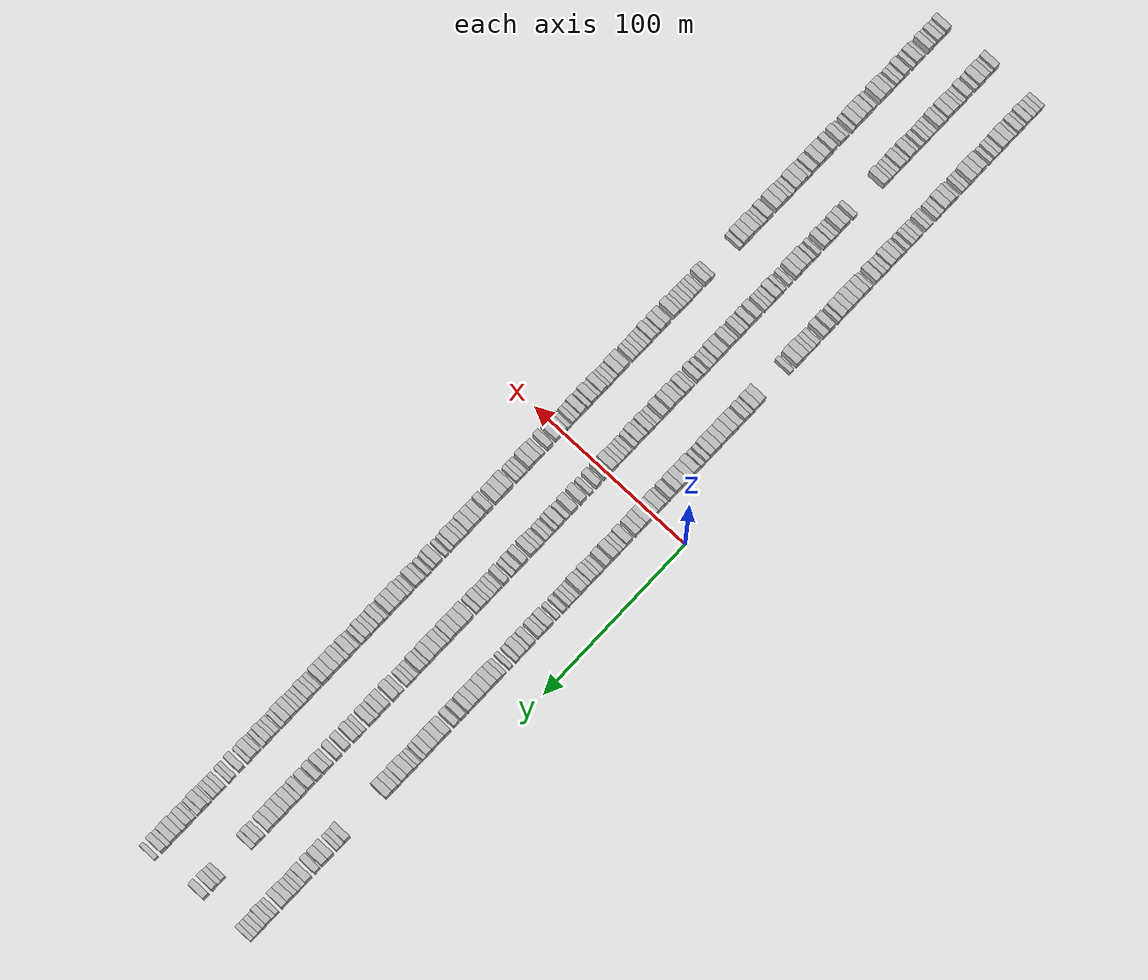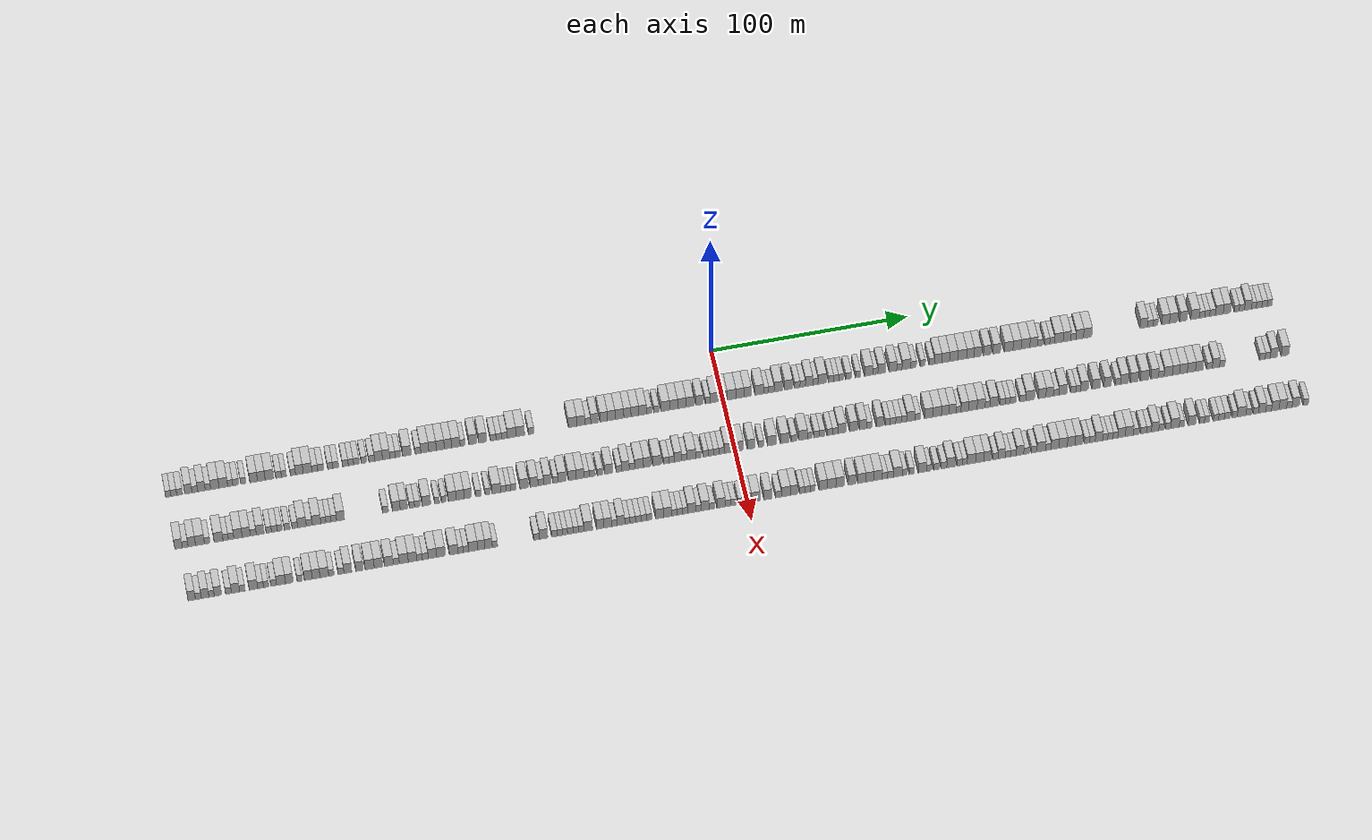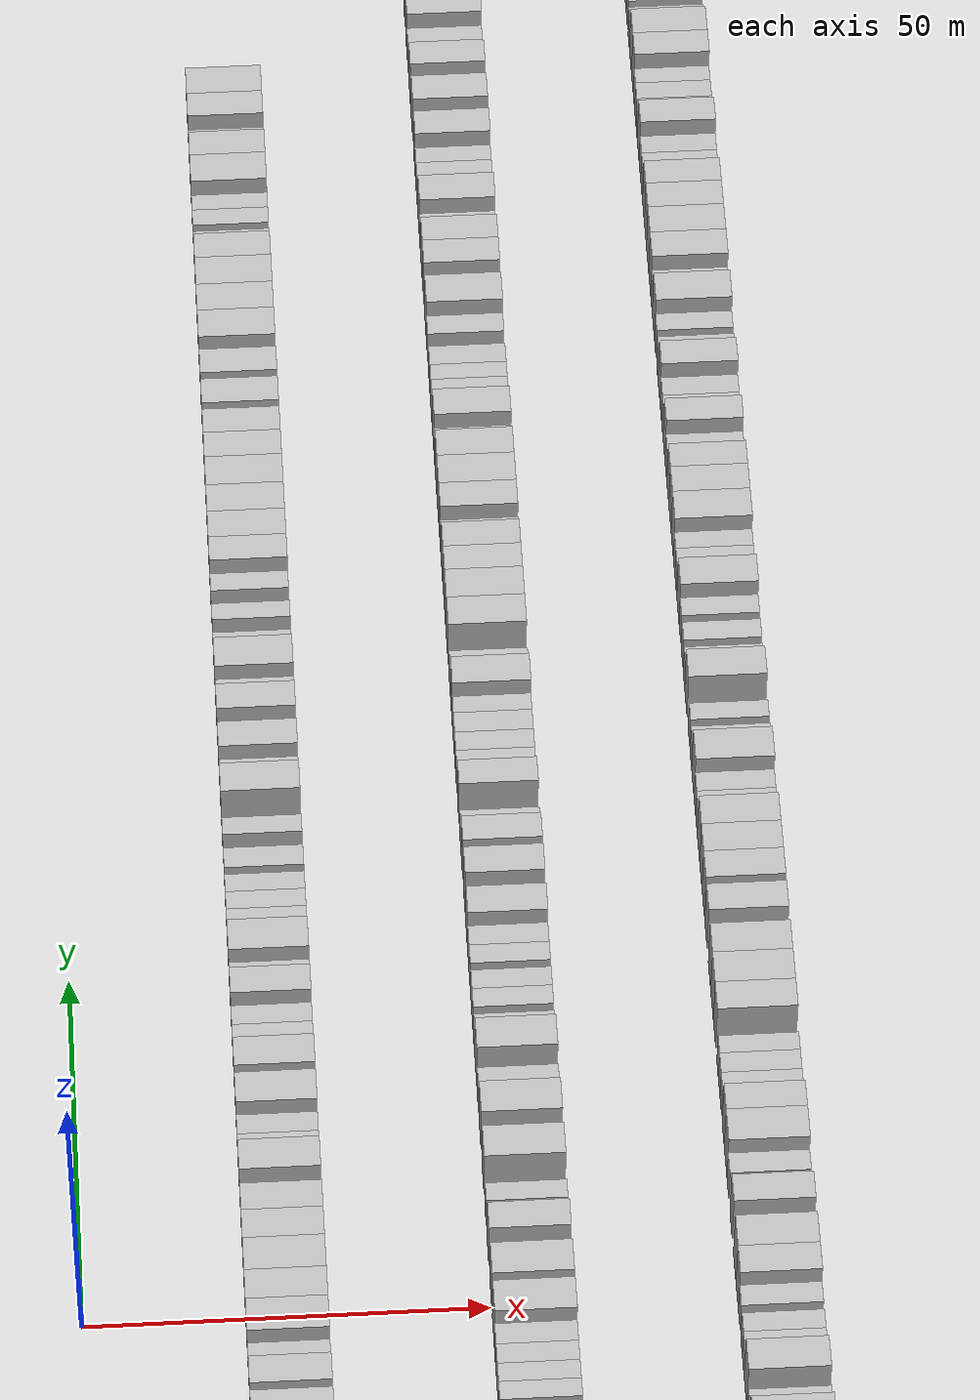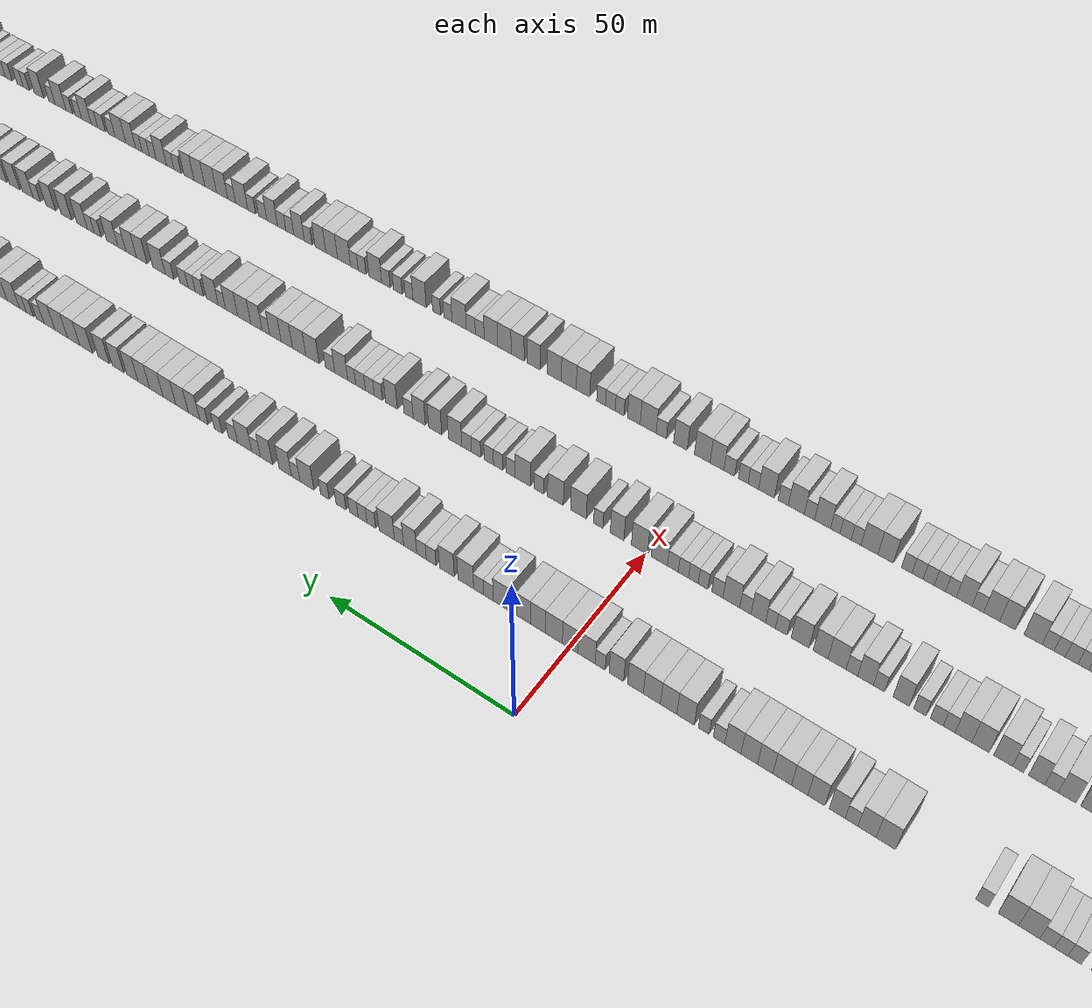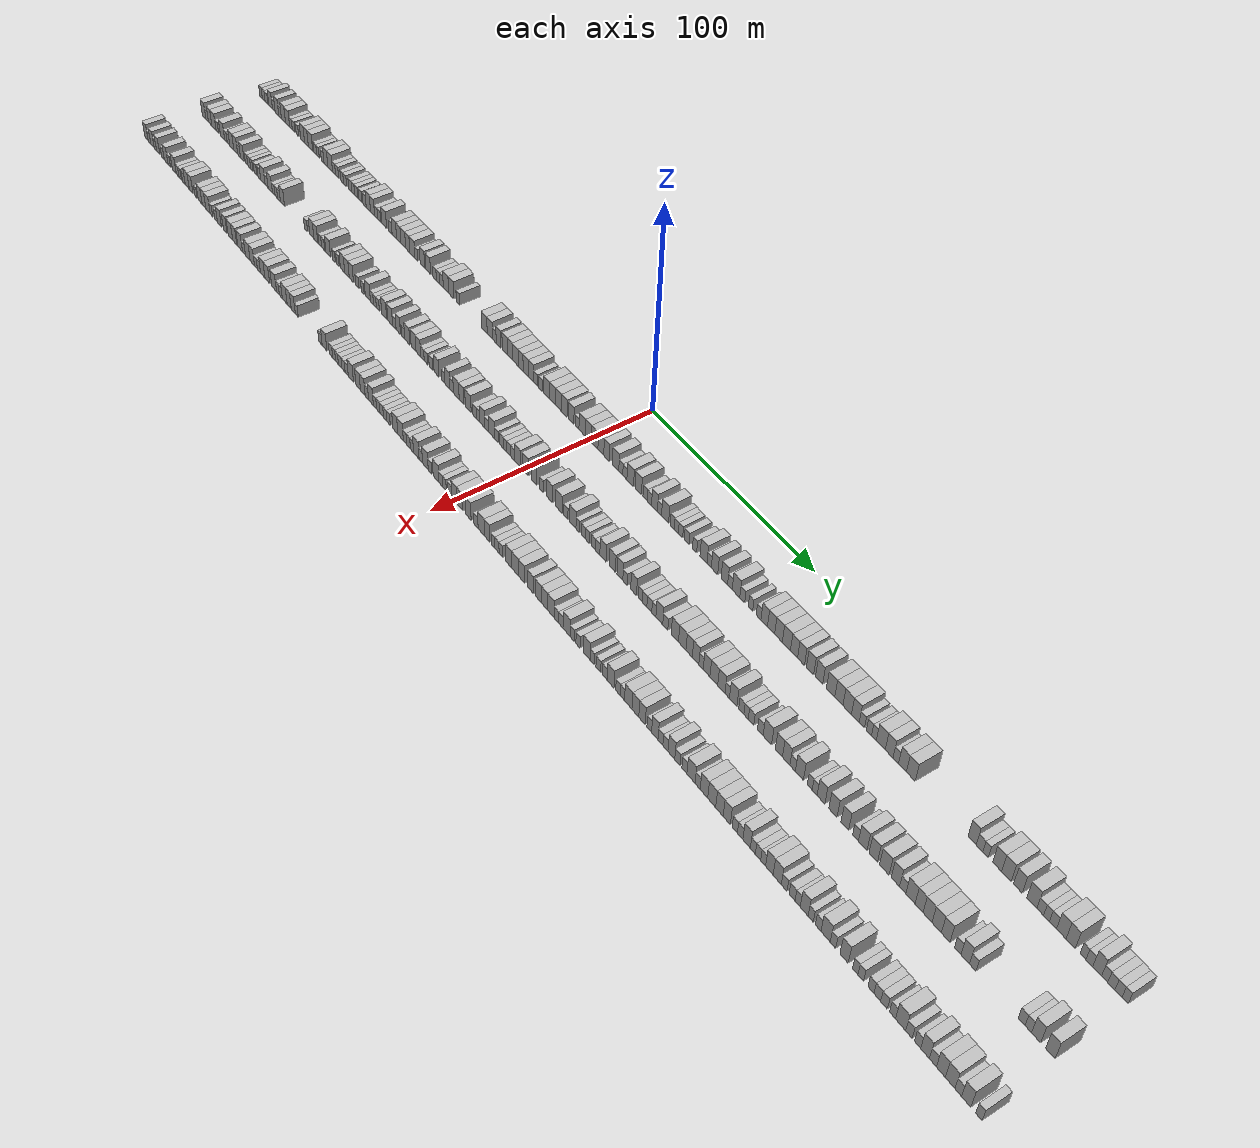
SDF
<sdf version="1.6">
 <world name="default">
  <scene>
   <sky><clouds><speed>12</speed></clouds></sky>
   <ambient>0.4 0.4 0.4 1</ambient>
   <background>0.7 0.7 0.7 1</background>
   <shadows>1</shadows>
  </scene>
  <gravity>0 0 -9.8066</gravity>
  <magnetic_field>6e-06 2.3e-05 -4.2e-05</magnetic_field>
  <physics default="0" name="default_physics" type="ode">
   <ode>
    <solver>
     <type>quick</type>
     <iters>10</iters>
     <sor>1.0</sor>
     <use_dynamic_moi_rescaling>0</use_dynamic_moi_rescaling>
    </solver>
    <constraints>
     <cfm>0</cfm>
     <erp>0.2</erp>
     <contact_max_correcting_vel>100</contact_max_correcting_vel>
     <contact_surface_layer>0.001</contact_surface_layer>
    </constraints>
   </ode>
   <max_step_size>0.004</max_step_size>
   <real_time_factor>1</real_time_factor>
   <real_time_update_rate>250</real_time_update_rate>
  </physics>
  <light name="sun" type="directional">
   <pose>0 0 10 0 0 0</pose>
   <diffuse>0.8 0.8 0.8 1</diffuse>
   <specular>0.2 0.2 0.2 1</specular>
   <attenuation>
    <range>1000</range>
    <constant>0.9</constant>
    <linear>0.01</linear>
    <quadratic>0.001</quadratic>
   </attenuation>
   <direction>-0.5 0.1 -0.9</direction>
  </light>
  <model name="building_1">
   <static>1</static>
   <pose>25.0000 -278.6960 0 0.000000 0.000000 0.000000</pose>
   <link name="link">
    <pose>0 0 3.00 0 0 0</pose>
    <collision name="collision"><geometry><box><size>10.0000 2.6080 6.0000</size></box></geometry></collision>
    <visual name="visual">
     <cast_shadows>0</cast_shadows>
     <geometry><box><size>10.0000 2.6080 6.0000</size></box></geometry>
     <material>
      <script>
       <uri>model://HANNAS_wall/materials/scripts</uri>
       <uri>model://HANNAS_wall/materials/textures</uri>
       <name>vrc/HANNAS_wall</name>
      </script>
     </material>
    </visual>
   </link>
  </model>
  <model name="building_2">
   <static>1</static>
   <pose>25.0000 -275.9448 0 0.000000 0.000000 0.000000</pose>
   <link name="link">
    <pose>0 0 3.00 0 0 0</pose>
    <collision name="collision"><geometry><box><size>10.0000 2.8943 6.0000</size></box></geometry></collision>
    <visual name="visual">
     <cast_shadows>0</cast_shadows>
     <geometry><box><size>10.0000 2.8943 6.0000</size></box></geometry>
     <material>
      <script>
       <uri>model://HANNAS_wall/materials/scripts</uri>
       <uri>model://HANNAS_wall/materials/textures</uri>
       <name>vrc/HANNAS_wall</name>
      </script>
     </material>
    </visual>
   </link>
  </model>
  <model name="building_3">
   <static>1</static>
   <pose>25.0000 -272.9993 0 0.000000 0.000000 0.000000</pose>
   <link name="link">
    <pose>0 0 3.00 0 0 0</pose>
    <collision name="collision"><geometry><box><size>10.0000 2.9968 6.0000</size></box></geometry></collision>
    <visual name="visual">
     <cast_shadows>0</cast_shadows>
     <geometry><box><size>10.0000 2.9968 6.0000</size></box></geometry>
     <material>
      <script>
       <uri>model://HANNAS_wall/materials/scripts</uri>
       <uri>model://HANNAS_wall/materials/textures</uri>
       <name>vrc/HANNAS_wall</name>
      </script>
     </material>
    </visual>
   </link>
  </model>
  <model name="building_4">
   <static>1</static>
   <pose>25.0000 -268.6715 0 0.000000 0.000000 0.000000</pose>
   <link name="link">
    <pose>0 0 4.50 0 0 0</pose>
    <collision name="collision"><geometry><box><size>10.0000 3.6588 9.0000</size></box></geometry></collision>
    <visual name="visual">
     <cast_shadows>0</cast_shadows>
     <geometry><box><size>10.0000 3.6588 9.0000</size></box></geometry>
     <material>
      <script>
       <uri>model://HANNAS_wall/materials/scripts</uri>
       <uri>model://HANNAS_wall/materials/textures</uri>
       <name>vrc/HANNAS_wall</name>
      </script>
     </material>
    </visual>
   </link>
  </model>
  <model name="building_5">
   <static>1</static>
   <pose>25.0000 -265.4527 0 0.000000 0.000000 0.000000</pose>
   <link name="link">
    <pose>0 0 3.00 0 0 0</pose>
    <collision name="collision"><geometry><box><size>10.0000 2.7790 6.0000</size></box></geometry></collision>
    <visual name="visual">
     <cast_shadows>0</cast_shadows>
     <geometry><box><size>10.0000 2.7790 6.0000</size></box></geometry>
     <material>
      <script>
       <uri>model://HANNAS_wall/materials/scripts</uri>
       <uri>model://HANNAS_wall/materials/textures</uri>
       <name>vrc/HANNAS_wall</name>
      </script>
     </material>
    </visual>
   </link>
  </model>
  <model name="building_6">
   <static>1</static>
   <pose>25.0000 -262.1939 0 0.000000 0.000000 0.000000</pose>
   <link name="link">
    <pose>0 0 4.50 0 0 0</pose>
    <collision name="collision"><geometry><box><size>10.0000 3.7385 9.0000</size></box></geometry></collision>
    <visual name="visual">
     <cast_shadows>0</cast_shadows>
     <geometry><box><size>10.0000 3.7385 9.0000</size></box></geometry>
     <material>
      <script>
       <uri>model://HANNAS_wall/materials/scripts</uri>
       <uri>model://HANNAS_wall/materials/textures</uri>
       <name>vrc/HANNAS_wall</name>
      </script>
     </material>
    </visual>
   </link>
  </model>
  <model name="building_7">
   <static>1</static>
   <pose>25.0000 -258.9581 0 0.000000 0.000000 0.000000</pose>
   <link name="link">
    <pose>0 0 3.00 0 0 0</pose>
    <collision name="collision"><geometry><box><size>10.0000 2.7331 6.0000</size></box></geometry></collision>
    <visual name="visual">
     <cast_shadows>0</cast_shadows>
     <geometry><box><size>10.0000 2.7331 6.0000</size></box></geometry>
     <material>
      <script>
       <uri>model://HANNAS_wall/materials/scripts</uri>
       <uri>model://HANNAS_wall/materials/textures</uri>
       <name>vrc/HANNAS_wall</name>
      </script>
     </material>
    </visual>
   </link>
  </model>
  <model name="building_8">
   <static>1</static>
   <pose>25.0000 -255.5041 0 0.000000 0.000000 0.000000</pose>
   <link name="link">
    <pose>0 0 4.50 0 0 0</pose>
    <collision name="collision"><geometry><box><size>10.0000 4.1749 9.0000</size></box></geometry></collision>
    <visual name="visual">
     <cast_shadows>0</cast_shadows>
     <geometry><box><size>10.0000 4.1749 9.0000</size></box></geometry>
     <material>
      <script>
       <uri>model://HANNAS_wall/materials/scripts</uri>
       <uri>model://HANNAS_wall/materials/textures</uri>
       <name>vrc/HANNAS_wall</name>
      </script>
     </material>
    </visual>
   </link>
  </model>
  <model name="building_9">
   <static>1</static>
   <pose>25.0000 -251.2742 0 0.000000 0.000000 0.000000</pose>
   <link name="link">
    <pose>0 0 4.50 0 0 0</pose>
    <collision name="collision"><geometry><box><size>10.0000 4.2849 9.0000</size></box></geometry></collision>
    <visual name="visual">
     <cast_shadows>0</cast_shadows>
     <geometry><box><size>10.0000 4.2849 9.0000</size></box></geometry>
     <material>
      <script>
       <uri>model://HANNAS_wall/materials/scripts</uri>
       <uri>model://HANNAS_wall/materials/textures</uri>
       <name>vrc/HANNAS_wall</name>
      </script>
     </material>
    </visual>
   </link>
  </model>
  <model name="building_10">
   <static>1</static>
   <pose>25.0000 -247.8500 0 0.000000 0.000000 0.000000</pose>
   <link name="link">
    <pose>0 0 3.00 0 0 0</pose>
    <collision name="collision"><geometry><box><size>10.0000 2.5636 6.0000</size></box></geometry></collision>
    <visual name="visual">
     <cast_shadows>0</cast_shadows>
     <geometry><box><size>10.0000 2.5636 6.0000</size></box></geometry>
     <material>
      <script>
       <uri>model://HANNAS_wall/materials/scripts</uri>
       <uri>model://HANNAS_wall/materials/textures</uri>
       <name>vrc/HANNAS_wall</name>
      </script>
     </material>
    </visual>
   </link>
  </model>
  <model name="building_11">
   <static>1</static>
   <pose>25.0000 -245.0954 0 0.000000 0.000000 0.000000</pose>
   <link name="link">
    <pose>0 0 3.00 0 0 0</pose>
    <collision name="collision"><geometry><box><size>10.0000 2.9456 6.0000</size></box></geometry></collision>
    <visual name="visual">
     <cast_shadows>0</cast_shadows>
     <geometry><box><size>10.0000 2.9456 6.0000</size></box></geometry>
     <material>
      <script>
       <uri>model://HANNAS_wall/materials/scripts</uri>
       <uri>model://HANNAS_wall/materials/textures</uri>
       <name>vrc/HANNAS_wall</name>
      </script>
     </material>
    </visual>
   </link>
  </model>
  <model name="building_12">
   <static>1</static>
   <pose>25.0000 -241.3536 0 0.000000 0.000000 0.000000</pose>
   <link name="link">
    <pose>0 0 3.00 0 0 0</pose>
    <collision name="collision"><geometry><box><size>10.0000 2.5378 6.0000</size></box></geometry></collision>
    <visual name="visual">
     <cast_shadows>0</cast_shadows>
     <geometry><box><size>10.0000 2.5378 6.0000</size></box></geometry>
     <material>
      <script>
       <uri>model://HANNAS_wall/materials/scripts</uri>
       <uri>model://HANNAS_wall/materials/textures</uri>
       <name>vrc/HANNAS_wall</name>
      </script>
     </material>
    </visual>
   </link>
  </model>
  <model name="building_13">
   <static>1</static>
   <pose>25.0000 -236.1740 0 0.000000 0.000000 0.000000</pose>
   <link name="link">
    <pose>0 0 4.50 0 0 0</pose>
    <collision name="collision"><geometry><box><size>10.0000 3.8214 9.0000</size></box></geometry></collision>
    <visual name="visual">
     <cast_shadows>0</cast_shadows>
     <geometry><box><size>10.0000 3.8214 9.0000</size></box></geometry>
     <material>
      <script>
       <uri>model://HANNAS_wall/materials/scripts</uri>
       <uri>model://HANNAS_wall/materials/textures</uri>
       <name>vrc/HANNAS_wall</name>
      </script>
     </material>
    </visual>
   </link>
  </model>
  <model name="building_14">
   <static>1</static>
   <pose>25.0000 -232.3892 0 0.000000 0.000000 0.000000</pose>
   <link name="link">
    <pose>0 0 4.50 0 0 0</pose>
    <collision name="collision"><geometry><box><size>10.0000 3.7483 9.0000</size></box></geometry></collision>
    <visual name="visual">
     <cast_shadows>0</cast_shadows>
     <geometry><box><size>10.0000 3.7483 9.0000</size></box></geometry>
     <material>
      <script>
       <uri>model://HANNAS_wall/materials/scripts</uri>
       <uri>model://HANNAS_wall/materials/textures</uri>
       <name>vrc/HANNAS_wall</name>
      </script>
     </material>
    </visual>
   </link>
  </model>
  <model name="building_15">
   <static>1</static>
   <pose>25.0000 -228.3384 0 0.000000 0.000000 0.000000</pose>
   <link name="link">
    <pose>0 0 4.50 0 0 0</pose>
    <collision name="collision"><geometry><box><size>10.0000 4.3533 9.0000</size></box></geometry></collision>
    <visual name="visual">
     <cast_shadows>0</cast_shadows>
     <geometry><box><size>10.0000 4.3533 9.0000</size></box></geometry>
     <material>
      <script>
       <uri>model://HANNAS_wall/materials/scripts</uri>
       <uri>model://HANNAS_wall/materials/textures</uri>
       <name>vrc/HANNAS_wall</name>
      </script>
     </material>
    </visual>
   </link>
  </model>
  <model name="building_16">
   <static>1</static>
   <pose>25.0000 -223.7473 0 0.000000 0.000000 0.000000</pose>
   <link name="link">
    <pose>0 0 3.00 0 0 0</pose>
    <collision name="collision"><geometry><box><size>10.0000 2.8288 6.0000</size></box></geometry></collision>
    <visual name="visual">
     <cast_shadows>0</cast_shadows>
     <geometry><box><size>10.0000 2.8288 6.0000</size></box></geometry>
     <material>
      <script>
       <uri>model://HANNAS_wall/materials/scripts</uri>
       <uri>model://HANNAS_wall/materials/textures</uri>
       <name>vrc/HANNAS_wall</name>
      </script>
     </material>
    </visual>
   </link>
  </model>
  <model name="building_17">
   <static>1</static>
   <pose>25.0000 -221.0974 0 0.000000 0.000000 0.000000</pose>
   <link name="link">
    <pose>0 0 3.00 0 0 0</pose>
    <collision name="collision"><geometry><box><size>10.0000 2.4709 6.0000</size></box></geometry></collision>
    <visual name="visual">
     <cast_shadows>0</cast_shadows>
     <geometry><box><size>10.0000 2.4709 6.0000</size></box></geometry>
     <material>
      <script>
       <uri>model://HANNAS_wall/materials/scripts</uri>
       <uri>model://HANNAS_wall/materials/textures</uri>
       <name>vrc/HANNAS_wall</name>
      </script>
     </material>
    </visual>
   </link>
  </model>
  <model name="building_18">
   <static>1</static>
   <pose>25.0000 -216.5776 0 0.000000 0.000000 0.000000</pose>
   <link name="link">
    <pose>0 0 3.00 0 0 0</pose>
    <collision name="collision"><geometry><box><size>10.0000 2.5687 6.0000</size></box></geometry></collision>
    <visual name="visual">
     <cast_shadows>0</cast_shadows>
     <geometry><box><size>10.0000 2.5687 6.0000</size></box></geometry>
     <material>
      <script>
       <uri>model://HANNAS_wall/materials/scripts</uri>
       <uri>model://HANNAS_wall/materials/textures</uri>
       <name>vrc/HANNAS_wall</name>
      </script>
     </material>
    </visual>
   </link>
  </model>
  <model name="building_19">
   <static>1</static>
   <pose>25.0000 -213.3972 0 0.000000 0.000000 0.000000</pose>
   <link name="link">
    <pose>0 0 4.50 0 0 0</pose>
    <collision name="collision"><geometry><box><size>10.0000 3.7922 9.0000</size></box></geometry></collision>
    <visual name="visual">
     <cast_shadows>0</cast_shadows>
     <geometry><box><size>10.0000 3.7922 9.0000</size></box></geometry>
     <material>
      <script>
       <uri>model://HANNAS_wall/materials/scripts</uri>
       <uri>model://HANNAS_wall/materials/textures</uri>
       <name>vrc/HANNAS_wall</name>
      </script>
     </material>
    </visual>
   </link>
  </model>
  <model name="building_20">
   <static>1</static>
   <pose>25.0000 -209.3081 0 0.000000 0.000000 0.000000</pose>
   <link name="link">
    <pose>0 0 4.50 0 0 0</pose>
    <collision name="collision"><geometry><box><size>10.0000 4.3859 9.0000</size></box></geometry></collision>
    <visual name="visual">
     <cast_shadows>0</cast_shadows>
     <geometry><box><size>10.0000 4.3859 9.0000</size></box></geometry>
     <material>
      <script>
       <uri>model://HANNAS_wall/materials/scripts</uri>
       <uri>model://HANNAS_wall/materials/textures</uri>
       <name>vrc/HANNAS_wall</name>
      </script>
     </material>
    </visual>
   </link>
  </model>
  <model name="building_21">
   <static>1</static>
   <pose>25.0000 -205.6732 0 0.000000 0.000000 0.000000</pose>
   <link name="link">
    <pose>0 0 3.00 0 0 0</pose>
    <collision name="collision"><geometry><box><size>10.0000 2.8840 6.0000</size></box></geometry></collision>
    <visual name="visual">
     <cast_shadows>0</cast_shadows>
     <geometry><box><size>10.0000 2.8840 6.0000</size></box></geometry>
     <material>
      <script>
       <uri>model://HANNAS_wall/materials/scripts</uri>
       <uri>model://HANNAS_wall/materials/textures</uri>
       <name>vrc/HANNAS_wall</name>
      </script>
     </material>
    </visual>
   </link>
  </model>
  <model name="building_22">
   <static>1</static>
   <pose>25.0000 -202.7381 0 0.000000 0.000000 0.000000</pose>
   <link name="link">
    <pose>0 0 3.00 0 0 0</pose>
    <collision name="collision"><geometry><box><size>10.0000 2.9862 6.0000</size></box></geometry></collision>
    <visual name="visual">
     <cast_shadows>0</cast_shadows>
     <geometry><box><size>10.0000 2.9862 6.0000</size></box></geometry>
     <material>
      <script>
       <uri>model://HANNAS_wall/materials/scripts</uri>
       <uri>model://HANNAS_wall/materials/textures</uri>
       <name>vrc/HANNAS_wall</name>
      </script>
     </material>
    </visual>
   </link>
  </model>
  <model name="building_23">
   <static>1</static>
   <pose>25.0000 -197.9643 0 0.000000 0.000000 0.000000</pose>
   <link name="link">
    <pose>0 0 3.00 0 0 0</pose>
    <collision name="collision"><geometry><box><size>10.0000 2.5615 6.0000</size></box></geometry></collision>
    <visual name="visual">
     <cast_shadows>0</cast_shadows>
     <geometry><box><size>10.0000 2.5615 6.0000</size></box></geometry>
     <material>
      <script>
       <uri>model://HANNAS_wall/materials/scripts</uri>
       <uri>model://HANNAS_wall/materials/textures</uri>
       <name>vrc/HANNAS_wall</name>
      </script>
     </material>
    </visual>
   </link>
  </model>
  <model name="building_24">
   <static>1</static>
   <pose>25.0000 -195.2222 0 0.000000 0.000000 0.000000</pose>
   <link name="link">
    <pose>0 0 3.00 0 0 0</pose>
    <collision name="collision"><geometry><box><size>10.0000 2.9227 6.0000</size></box></geometry></collision>
    <visual name="visual">
     <cast_shadows>0</cast_shadows>
     <geometry><box><size>10.0000 2.9227 6.0000</size></box></geometry>
     <material>
      <script>
       <uri>model://HANNAS_wall/materials/scripts</uri>
       <uri>model://HANNAS_wall/materials/textures</uri>
       <name>vrc/HANNAS_wall</name>
      </script>
     </material>
    </visual>
   </link>
  </model>
  <model name="building_25">
   <static>1</static>
   <pose>25.0000 -190.3567 0 0.000000 0.000000 0.000000</pose>
   <link name="link">
    <pose>0 0 3.00 0 0 0</pose>
    <collision name="collision"><geometry><box><size>10.0000 2.8083 6.0000</size></box></geometry></collision>
    <visual name="visual">
     <cast_shadows>0</cast_shadows>
     <geometry><box><size>10.0000 2.8083 6.0000</size></box></geometry>
     <material>
      <script>
       <uri>model://HANNAS_wall/materials/scripts</uri>
       <uri>model://HANNAS_wall/materials/textures</uri>
       <name>vrc/HANNAS_wall</name>
      </script>
     </material>
    </visual>
   </link>
  </model>
  <model name="building_26">
   <static>1</static>
   <pose>25.0000 -187.6123 0 0.000000 0.000000 0.000000</pose>
   <link name="link">
    <pose>0 0 3.00 0 0 0</pose>
    <collision name="collision"><geometry><box><size>10.0000 2.6805 6.0000</size></box></geometry></collision>
    <visual name="visual">
     <cast_shadows>0</cast_shadows>
     <geometry><box><size>10.0000 2.6805 6.0000</size></box></geometry>
     <material>
      <script>
       <uri>model://HANNAS_wall/materials/scripts</uri>
       <uri>model://HANNAS_wall/materials/textures</uri>
       <name>vrc/HANNAS_wall</name>
      </script>
     </material>
    </visual>
   </link>
  </model>
  <model name="building_27">
   <static>1</static>
   <pose>25.0000 -184.8709 0 0.000000 0.000000 0.000000</pose>
   <link name="link">
    <pose>0 0 3.00 0 0 0</pose>
    <collision name="collision"><geometry><box><size>10.0000 2.8024 6.0000</size></box></geometry></collision>
    <visual name="visual">
     <cast_shadows>0</cast_shadows>
     <geometry><box><size>10.0000 2.8024 6.0000</size></box></geometry>
     <material>
      <script>
       <uri>model://HANNAS_wall/materials/scripts</uri>
       <uri>model://HANNAS_wall/materials/textures</uri>
       <name>vrc/HANNAS_wall</name>
      </script>
     </material>
    </visual>
   </link>
  </model>
  <model name="building_28">
   <static>1</static>
   <pose>25.0000 -181.0701 0 0.000000 0.000000 0.000000</pose>
   <link name="link">
    <pose>0 0 3.00 0 0 0</pose>
    <collision name="collision"><geometry><box><size>10.0000 2.7993 6.0000</size></box></geometry></collision>
    <visual name="visual">
     <cast_shadows>0</cast_shadows>
     <geometry><box><size>10.0000 2.7993 6.0000</size></box></geometry>
     <material>
      <script>
       <uri>model://HANNAS_wall/materials/scripts</uri>
       <uri>model://HANNAS_wall/materials/textures</uri>
       <name>vrc/HANNAS_wall</name>
      </script>
     </material>
    </visual>
   </link>
  </model>
  <model name="building_29">
   <static>1</static>
   <pose>25.0000 -177.2287 0 0.000000 0.000000 0.000000</pose>
   <link name="link">
    <pose>0 0 3.00 0 0 0</pose>
    <collision name="collision"><geometry><box><size>10.0000 2.8834 6.0000</size></box></geometry></collision>
    <visual name="visual">
     <cast_shadows>0</cast_shadows>
     <geometry><box><size>10.0000 2.8834 6.0000</size></box></geometry>
     <material>
      <script>
       <uri>model://HANNAS_wall/materials/scripts</uri>
       <uri>model://HANNAS_wall/materials/textures</uri>
       <name>vrc/HANNAS_wall</name>
      </script>
     </material>
    </visual>
   </link>
  </model>
  <model name="building_30">
   <static>1</static>
   <pose>25.0000 -173.8132 0 0.000000 0.000000 0.000000</pose>
   <link name="link">
    <pose>0 0 4.50 0 0 0</pose>
    <collision name="collision"><geometry><box><size>10.0000 3.9477 9.0000</size></box></geometry></collision>
    <visual name="visual">
     <cast_shadows>0</cast_shadows>
     <geometry><box><size>10.0000 3.9477 9.0000</size></box></geometry>
     <material>
      <script>
       <uri>model://HANNAS_wall/materials/scripts</uri>
       <uri>model://HANNAS_wall/materials/textures</uri>
       <name>vrc/HANNAS_wall</name>
      </script>
     </material>
    </visual>
   </link>
  </model>
  <model name="building_31">
   <static>1</static>
   <pose>25.0000 -169.9897 0 0.000000 0.000000 0.000000</pose>
   <link name="link">
    <pose>0 0 4.50 0 0 0</pose>
    <collision name="collision"><geometry><box><size>10.0000 3.6992 9.0000</size></box></geometry></collision>
    <visual name="visual">
     <cast_shadows>0</cast_shadows>
     <geometry><box><size>10.0000 3.6992 9.0000</size></box></geometry>
     <material>
      <script>
       <uri>model://HANNAS_wall/materials/scripts</uri>
       <uri>model://HANNAS_wall/materials/textures</uri>
       <name>vrc/HANNAS_wall</name>
      </script>
     </material>
    </visual>
   </link>
  </model>
  <model name="building_32">
   <static>1</static>
   <pose>25.0000 -166.7838 0 0.000000 0.000000 0.000000</pose>
   <link name="link">
    <pose>0 0 3.00 0 0 0</pose>
    <collision name="collision"><geometry><box><size>10.0000 2.7128 6.0000</size></box></geometry></collision>
    <visual name="visual">
     <cast_shadows>0</cast_shadows>
     <geometry><box><size>10.0000 2.7128 6.0000</size></box></geometry>
     <material>
      <script>
       <uri>model://HANNAS_wall/materials/scripts</uri>
       <uri>model://HANNAS_wall/materials/textures</uri>
       <name>vrc/HANNAS_wall</name>
      </script>
     </material>
    </visual>
   </link>
  </model>
  <model name="building_33">
   <static>1</static>
   <pose>25.0000 -164.0759 0 0.000000 0.000000 0.000000</pose>
   <link name="link">
    <pose>0 0 3.00 0 0 0</pose>
    <collision name="collision"><geometry><box><size>10.0000 2.7030 6.0000</size></box></geometry></collision>
    <visual name="visual">
     <cast_shadows>0</cast_shadows>
     <geometry><box><size>10.0000 2.7030 6.0000</size></box></geometry>
     <material>
      <script>
       <uri>model://HANNAS_wall/materials/scripts</uri>
       <uri>model://HANNAS_wall/materials/textures</uri>
       <name>vrc/HANNAS_wall</name>
      </script>
     </material>
    </visual>
   </link>
  </model>
  <model name="building_34">
   <static>1</static>
   <pose>25.0000 -159.5859 0 0.000000 0.000000 0.000000</pose>
   <link name="link">
    <pose>0 0 4.50 0 0 0</pose>
    <collision name="collision"><geometry><box><size>10.0000 4.2769 9.0000</size></box></geometry></collision>
    <visual name="visual">
     <cast_shadows>0</cast_shadows>
     <geometry><box><size>10.0000 4.2769 9.0000</size></box></geometry>
     <material>
      <script>
       <uri>model://HANNAS_wall/materials/scripts</uri>
       <uri>model://HANNAS_wall/materials/textures</uri>
       <name>vrc/HANNAS_wall</name>
      </script>
     </material>
    </visual>
   </link>
  </model>
  <model name="building_35">
   <static>1</static>
   <pose>25.0000 -154.0492 0 0.000000 0.000000 0.000000</pose>
   <link name="link">
    <pose>0 0 3.00 0 0 0</pose>
    <collision name="collision"><geometry><box><size>10.0000 2.7965 6.0000</size></box></geometry></collision>
    <visual name="visual">
     <cast_shadows>0</cast_shadows>
     <geometry><box><size>10.0000 2.7965 6.0000</size></box></geometry>
     <material>
      <script>
       <uri>model://HANNAS_wall/materials/scripts</uri>
       <uri>model://HANNAS_wall/materials/textures</uri>
       <name>vrc/HANNAS_wall</name>
      </script>
     </material>
    </visual>
   </link>
  </model>
  <model name="building_36">
   <static>1</static>
   <pose>25.0000 -150.6507 0 0.000000 0.000000 0.000000</pose>
   <link name="link">
    <pose>0 0 4.50 0 0 0</pose>
    <collision name="collision"><geometry><box><size>10.0000 4.0004 9.0000</size></box></geometry></collision>
    <visual name="visual">
     <cast_shadows>0</cast_shadows>
     <geometry><box><size>10.0000 4.0004 9.0000</size></box></geometry>
     <material>
      <script>
       <uri>model://HANNAS_wall/materials/scripts</uri>
       <uri>model://HANNAS_wall/materials/textures</uri>
       <name>vrc/HANNAS_wall</name>
      </script>
     </material>
    </visual>
   </link>
  </model>
  <model name="building_37">
   <static>1</static>
   <pose>25.0000 -146.7634 0 0.000000 0.000000 0.000000</pose>
   <link name="link">
    <pose>0 0 4.50 0 0 0</pose>
    <collision name="collision"><geometry><box><size>10.0000 3.7743 9.0000</size></box></geometry></collision>
    <visual name="visual">
     <cast_shadows>0</cast_shadows>
     <geometry><box><size>10.0000 3.7743 9.0000</size></box></geometry>
     <material>
      <script>
       <uri>model://HANNAS_wall/materials/scripts</uri>
       <uri>model://HANNAS_wall/materials/textures</uri>
       <name>vrc/HANNAS_wall</name>
      </script>
     </material>
    </visual>
   </link>
  </model>
  <model name="building_38">
   <static>1</static>
   <pose>25.0000 -142.8606 0 0.000000 0.000000 0.000000</pose>
   <link name="link">
    <pose>0 0 4.50 0 0 0</pose>
    <collision name="collision"><geometry><box><size>10.0000 4.0314 9.0000</size></box></geometry></collision>
    <visual name="visual">
     <cast_shadows>0</cast_shadows>
     <geometry><box><size>10.0000 4.0314 9.0000</size></box></geometry>
     <material>
      <script>
       <uri>model://HANNAS_wall/materials/scripts</uri>
       <uri>model://HANNAS_wall/materials/textures</uri>
       <name>vrc/HANNAS_wall</name>
      </script>
     </material>
    </visual>
   </link>
  </model>
  <model name="building_39">
   <static>1</static>
   <pose>25.0000 -139.0250 0 0.000000 0.000000 0.000000</pose>
   <link name="link">
    <pose>0 0 4.50 0 0 0</pose>
    <collision name="collision"><geometry><box><size>10.0000 3.6398 9.0000</size></box></geometry></collision>
    <visual name="visual">
     <cast_shadows>0</cast_shadows>
     <geometry><box><size>10.0000 3.6398 9.0000</size></box></geometry>
     <material>
      <script>
       <uri>model://HANNAS_wall/materials/scripts</uri>
       <uri>model://HANNAS_wall/materials/textures</uri>
       <name>vrc/HANNAS_wall</name>
      </script>
     </material>
    </visual>
   </link>
  </model>
  <model name="building_40">
   <static>1</static>
   <pose>25.0000 -135.0623 0 0.000000 0.000000 0.000000</pose>
   <link name="link">
    <pose>0 0 4.50 0 0 0</pose>
    <collision name="collision"><geometry><box><size>10.0000 4.2854 9.0000</size></box></geometry></collision>
    <visual name="visual">
     <cast_shadows>0</cast_shadows>
     <geometry><box><size>10.0000 4.2854 9.0000</size></box></geometry>
     <material>
      <script>
       <uri>model://HANNAS_wall/materials/scripts</uri>
       <uri>model://HANNAS_wall/materials/textures</uri>
       <name>vrc/HANNAS_wall</name>
      </script>
     </material>
    </visual>
   </link>
  </model>
  <model name="building_41">
   <static>1</static>
   <pose>25.0000 -131.6870 0 0.000000 0.000000 0.000000</pose>
   <link name="link">
    <pose>0 0 3.00 0 0 0</pose>
    <collision name="collision"><geometry><box><size>10.0000 2.4652 6.0000</size></box></geometry></collision>
    <visual name="visual">
     <cast_shadows>0</cast_shadows>
     <geometry><box><size>10.0000 2.4652 6.0000</size></box></geometry>
     <material>
      <script>
       <uri>model://HANNAS_wall/materials/scripts</uri>
       <uri>model://HANNAS_wall/materials/textures</uri>
       <name>vrc/HANNAS_wall</name>
      </script>
     </material>
    </visual>
   </link>
  </model>
  <model name="building_42">
   <static>1</static>
   <pose>25.0000 -126.5060 0 0.000000 0.000000 0.000000</pose>
   <link name="link">
    <pose>0 0 4.50 0 0 0</pose>
    <collision name="collision"><geometry><box><size>10.0000 3.8968 9.0000</size></box></geometry></collision>
    <visual name="visual">
     <cast_shadows>0</cast_shadows>
     <geometry><box><size>10.0000 3.8968 9.0000</size></box></geometry>
     <material>
      <script>
       <uri>model://HANNAS_wall/materials/scripts</uri>
       <uri>model://HANNAS_wall/materials/textures</uri>
       <name>vrc/HANNAS_wall</name>
      </script>
     </material>
    </visual>
   </link>
  </model>
  <model name="building_43">
   <static>1</static>
   <pose>25.0000 -121.6081 0 0.000000 0.000000 0.000000</pose>
   <link name="link">
    <pose>0 0 4.50 0 0 0</pose>
    <collision name="collision"><geometry><box><size>10.0000 3.8990 9.0000</size></box></geometry></collision>
    <visual name="visual">
     <cast_shadows>0</cast_shadows>
     <geometry><box><size>10.0000 3.8990 9.0000</size></box></geometry>
     <material>
      <script>
       <uri>model://HANNAS_wall/materials/scripts</uri>
       <uri>model://HANNAS_wall/materials/textures</uri>
       <name>vrc/HANNAS_wall</name>
      </script>
     </material>
    </visual>
   </link>
  </model>
  <model name="building_44">
   <static>1</static>
   <pose>25.0000 -116.2674 0 0.000000 0.000000 0.000000</pose>
   <link name="link">
    <pose>0 0 3.00 0 0 0</pose>
    <collision name="collision"><geometry><box><size>10.0000 2.7825 6.0000</size></box></geometry></collision>
    <visual name="visual">
     <cast_shadows>0</cast_shadows>
     <geometry><box><size>10.0000 2.7825 6.0000</size></box></geometry>
     <material>
      <script>
       <uri>model://HANNAS_wall/materials/scripts</uri>
       <uri>model://HANNAS_wall/materials/textures</uri>
       <name>vrc/HANNAS_wall</name>
      </script>
     </material>
    </visual>
   </link>
  </model>
  <model name="building_45">
   <static>1</static>
   <pose>25.0000 -113.4976 0 0.000000 0.000000 0.000000</pose>
   <link name="link">
    <pose>0 0 3.00 0 0 0</pose>
    <collision name="collision"><geometry><box><size>10.0000 2.7571 6.0000</size></box></geometry></collision>
    <visual name="visual">
     <cast_shadows>0</cast_shadows>
     <geometry><box><size>10.0000 2.7571 6.0000</size></box></geometry>
     <material>
      <script>
       <uri>model://HANNAS_wall/materials/scripts</uri>
       <uri>model://HANNAS_wall/materials/textures</uri>
       <name>vrc/HANNAS_wall</name>
      </script>
     </material>
    </visual>
   </link>
  </model>
  <model name="building_46">
   <static>1</static>
   <pose>25.0000 -110.6346 0 0.000000 0.000000 0.000000</pose>
   <link name="link">
    <pose>0 0 3.00 0 0 0</pose>
    <collision name="collision"><geometry><box><size>10.0000 2.9691 6.0000</size></box></geometry></collision>
    <visual name="visual">
     <cast_shadows>0</cast_shadows>
     <geometry><box><size>10.0000 2.9691 6.0000</size></box></geometry>
     <material>
      <script>
       <uri>model://HANNAS_wall/materials/scripts</uri>
       <uri>model://HANNAS_wall/materials/textures</uri>
       <name>vrc/HANNAS_wall</name>
      </script>
     </material>
    </visual>
   </link>
  </model>
  <model name="building_47">
   <static>1</static>
   <pose>25.0000 -106.9624 0 0.000000 0.000000 0.000000</pose>
   <link name="link">
    <pose>0 0 4.50 0 0 0</pose>
    <collision name="collision"><geometry><box><size>10.0000 4.3752 9.0000</size></box></geometry></collision>
    <visual name="visual">
     <cast_shadows>0</cast_shadows>
     <geometry><box><size>10.0000 4.3752 9.0000</size></box></geometry>
     <material>
      <script>
       <uri>model://HANNAS_wall/materials/scripts</uri>
       <uri>model://HANNAS_wall/materials/textures</uri>
       <name>vrc/HANNAS_wall</name>
      </script>
     </material>
    </visual>
   </link>
  </model>
  <model name="building_48">
   <static>1</static>
   <pose>25.0000 -102.6520 0 0.000000 0.000000 0.000000</pose>
   <link name="link">
    <pose>0 0 4.50 0 0 0</pose>
    <collision name="collision"><geometry><box><size>10.0000 4.2457 9.0000</size></box></geometry></collision>
    <visual name="visual">
     <cast_shadows>0</cast_shadows>
     <geometry><box><size>10.0000 4.2457 9.0000</size></box></geometry>
     <material>
      <script>
       <uri>model://HANNAS_wall/materials/scripts</uri>
       <uri>model://HANNAS_wall/materials/textures</uri>
       <name>vrc/HANNAS_wall</name>
      </script>
     </material>
    </visual>
   </link>
  </model>
  <model name="building_49">
   <static>1</static>
   <pose>25.0000 -97.1509 0 0.000000 0.000000 0.000000</pose>
   <link name="link">
    <pose>0 0 3.00 0 0 0</pose>
    <collision name="collision"><geometry><box><size>10.0000 2.7563 6.0000</size></box></geometry></collision>
    <visual name="visual">
     <cast_shadows>0</cast_shadows>
     <geometry><box><size>10.0000 2.7563 6.0000</size></box></geometry>
     <material>
      <script>
       <uri>model://HANNAS_wall/materials/scripts</uri>
       <uri>model://HANNAS_wall/materials/textures</uri>
       <name>vrc/HANNAS_wall</name>
      </script>
     </material>
    </visual>
   </link>
  </model>
  <model name="building_50">
   <static>1</static>
   <pose>25.0000 -76.2877 0 0.000000 0.000000 0.000000</pose>
   <link name="link">
    <pose>0 0 4.50 0 0 0</pose>
    <collision name="collision"><geometry><box><size>10.0000 4.3234 9.0000</size></box></geometry></collision>
    <visual name="visual">
     <cast_shadows>0</cast_shadows>
     <geometry><box><size>10.0000 4.3234 9.0000</size></box></geometry>
     <material>
      <script>
       <uri>model://HANNAS_wall/materials/scripts</uri>
       <uri>model://HANNAS_wall/materials/textures</uri>
       <name>vrc/HANNAS_wall</name>
      </script>
     </material>
    </visual>
   </link>
  </model>
  <model name="building_51">
   <static>1</static>
   <pose>25.0000 -72.0856 0 0.000000 0.000000 0.000000</pose>
   <link name="link">
    <pose>0 0 4.50 0 0 0</pose>
    <collision name="collision"><geometry><box><size>10.0000 4.0809 9.0000</size></box></geometry></collision>
    <visual name="visual">
     <cast_shadows>0</cast_shadows>
     <geometry><box><size>10.0000 4.0809 9.0000</size></box></geometry>
     <material>
      <script>
       <uri>model://HANNAS_wall/materials/scripts</uri>
       <uri>model://HANNAS_wall/materials/textures</uri>
       <name>vrc/HANNAS_wall</name>
      </script>
     </material>
    </visual>
   </link>
  </model>
  <model name="building_52">
   <static>1</static>
   <pose>25.0000 -68.6039 0 0.000000 0.000000 0.000000</pose>
   <link name="link">
    <pose>0 0 3.00 0 0 0</pose>
    <collision name="collision"><geometry><box><size>10.0000 2.8825 6.0000</size></box></geometry></collision>
    <visual name="visual">
     <cast_shadows>0</cast_shadows>
     <geometry><box><size>10.0000 2.8825 6.0000</size></box></geometry>
     <material>
      <script>
       <uri>model://HANNAS_wall/materials/scripts</uri>
       <uri>model://HANNAS_wall/materials/textures</uri>
       <name>vrc/HANNAS_wall</name>
      </script>
     </material>
    </visual>
   </link>
  </model>
  <model name="building_53">
   <static>1</static>
   <pose>25.0000 -65.3597 0 0.000000 0.000000 0.000000</pose>
   <link name="link">
    <pose>0 0 4.50 0 0 0</pose>
    <collision name="collision"><geometry><box><size>10.0000 3.6057 9.0000</size></box></geometry></collision>
    <visual name="visual">
     <cast_shadows>0</cast_shadows>
     <geometry><box><size>10.0000 3.6057 9.0000</size></box></geometry>
     <material>
      <script>
       <uri>model://HANNAS_wall/materials/scripts</uri>
       <uri>model://HANNAS_wall/materials/textures</uri>
       <name>vrc/HANNAS_wall</name>
      </script>
     </material>
    </visual>
   </link>
  </model>
  <model name="building_54">
   <static>1</static>
   <pose>25.0000 -60.6032 0 0.000000 0.000000 0.000000</pose>
   <link name="link">
    <pose>0 0 4.50 0 0 0</pose>
    <collision name="collision"><geometry><box><size>10.0000 3.9074 9.0000</size></box></geometry></collision>
    <visual name="visual">
     <cast_shadows>0</cast_shadows>
     <geometry><box><size>10.0000 3.9074 9.0000</size></box></geometry>
     <material>
      <script>
       <uri>model://HANNAS_wall/materials/scripts</uri>
       <uri>model://HANNAS_wall/materials/textures</uri>
       <name>vrc/HANNAS_wall</name>
      </script>
     </material>
    </visual>
   </link>
  </model>
  <model name="building_55">
   <static>1</static>
   <pose>25.0000 -56.7552 0 0.000000 0.000000 0.000000</pose>
   <link name="link">
    <pose>0 0 4.50 0 0 0</pose>
    <collision name="collision"><geometry><box><size>10.0000 3.7886 9.0000</size></box></geometry></collision>
    <visual name="visual">
     <cast_shadows>0</cast_shadows>
     <geometry><box><size>10.0000 3.7886 9.0000</size></box></geometry>
     <material>
      <script>
       <uri>model://HANNAS_wall/materials/scripts</uri>
       <uri>model://HANNAS_wall/materials/textures</uri>
       <name>vrc/HANNAS_wall</name>
      </script>
     </material>
    </visual>
   </link>
  </model>
  <model name="building_56">
   <static>1</static>
   <pose>25.0000 -52.6733 0 0.000000 0.000000 0.000000</pose>
   <link name="link">
    <pose>0 0 4.50 0 0 0</pose>
    <collision name="collision"><geometry><box><size>10.0000 4.3752 9.0000</size></box></geometry></collision>
    <visual name="visual">
     <cast_shadows>0</cast_shadows>
     <geometry><box><size>10.0000 4.3752 9.0000</size></box></geometry>
     <material>
      <script>
       <uri>model://HANNAS_wall/materials/scripts</uri>
       <uri>model://HANNAS_wall/materials/textures</uri>
       <name>vrc/HANNAS_wall</name>
      </script>
     </material>
    </visual>
   </link>
  </model>
  <model name="building_57">
   <static>1</static>
   <pose>25.0000 -48.6687 0 0.000000 0.000000 0.000000</pose>
   <link name="link">
    <pose>0 0 4.50 0 0 0</pose>
    <collision name="collision"><geometry><box><size>10.0000 3.6341 9.0000</size></box></geometry></collision>
    <visual name="visual">
     <cast_shadows>0</cast_shadows>
     <geometry><box><size>10.0000 3.6341 9.0000</size></box></geometry>
     <material>
      <script>
       <uri>model://HANNAS_wall/materials/scripts</uri>
       <uri>model://HANNAS_wall/materials/textures</uri>
       <name>vrc/HANNAS_wall</name>
      </script>
     </material>
    </visual>
   </link>
  </model>
  <model name="building_58">
   <static>1</static>
   <pose>25.0000 -44.8705 0 0.000000 0.000000 0.000000</pose>
   <link name="link">
    <pose>0 0 4.50 0 0 0</pose>
    <collision name="collision"><geometry><box><size>10.0000 3.9623 9.0000</size></box></geometry></collision>
    <visual name="visual">
     <cast_shadows>0</cast_shadows>
     <geometry><box><size>10.0000 3.9623 9.0000</size></box></geometry>
     <material>
      <script>
       <uri>model://HANNAS_wall/materials/scripts</uri>
       <uri>model://HANNAS_wall/materials/textures</uri>
       <name>vrc/HANNAS_wall</name>
      </script>
     </material>
    </visual>
   </link>
  </model>
  <model name="building_59">
   <static>1</static>
   <pose>25.0000 -40.9646 0 0.000000 0.000000 0.000000</pose>
   <link name="link">
    <pose>0 0 4.50 0 0 0</pose>
    <collision name="collision"><geometry><box><size>10.0000 3.8495 9.0000</size></box></geometry></collision>
    <visual name="visual">
     <cast_shadows>0</cast_shadows>
     <geometry><box><size>10.0000 3.8495 9.0000</size></box></geometry>
     <material>
      <script>
       <uri>model://HANNAS_wall/materials/scripts</uri>
       <uri>model://HANNAS_wall/materials/textures</uri>
       <name>vrc/HANNAS_wall</name>
      </script>
     </material>
    </visual>
   </link>
  </model>
  <model name="building_60">
   <static>1</static>
   <pose>25.0000 -37.6513 0 0.000000 0.000000 0.000000</pose>
   <link name="link">
    <pose>0 0 3.00 0 0 0</pose>
    <collision name="collision"><geometry><box><size>10.0000 2.7770 6.0000</size></box></geometry></collision>
    <visual name="visual">
     <cast_shadows>0</cast_shadows>
     <geometry><box><size>10.0000 2.7770 6.0000</size></box></geometry>
     <material>
      <script>
       <uri>model://HANNAS_wall/materials/scripts</uri>
       <uri>model://HANNAS_wall/materials/textures</uri>
       <name>vrc/HANNAS_wall</name>
      </script>
     </material>
    </visual>
   </link>
  </model>
  <model name="building_61">
   <static>1</static>
   <pose>25.0000 -33.9535 0 0.000000 0.000000 0.000000</pose>
   <link name="link">
    <pose>0 0 3.00 0 0 0</pose>
    <collision name="collision"><geometry><box><size>10.0000 2.6188 6.0000</size></box></geometry></collision>
    <visual name="visual">
     <cast_shadows>0</cast_shadows>
     <geometry><box><size>10.0000 2.6188 6.0000</size></box></geometry>
     <material>
      <script>
       <uri>model://HANNAS_wall/materials/scripts</uri>
       <uri>model://HANNAS_wall/materials/textures</uri>
       <name>vrc/HANNAS_wall</name>
      </script>
     </material>
    </visual>
   </link>
  </model>
  <model name="building_62">
   <static>1</static>
   <pose>25.0000 -29.4940 0 0.000000 0.000000 0.000000</pose>
   <link name="link">
    <pose>0 0 4.50 0 0 0</pose>
    <collision name="collision"><geometry><box><size>10.0000 4.3001 9.0000</size></box></geometry></collision>
    <visual name="visual">
     <cast_shadows>0</cast_shadows>
     <geometry><box><size>10.0000 4.3001 9.0000</size></box></geometry>
     <material>
      <script>
       <uri>model://HANNAS_wall/materials/scripts</uri>
       <uri>model://HANNAS_wall/materials/textures</uri>
       <name>vrc/HANNAS_wall</name>
      </script>
     </material>
    </visual>
   </link>
  </model>
  <model name="building_63">
   <static>1</static>
   <pose>25.0000 -25.3099 0 0.000000 0.000000 0.000000</pose>
   <link name="link">
    <pose>0 0 4.50 0 0 0</pose>
    <collision name="collision"><geometry><box><size>10.0000 4.0682 9.0000</size></box></geometry></collision>
    <visual name="visual">
     <cast_shadows>0</cast_shadows>
     <geometry><box><size>10.0000 4.0682 9.0000</size></box></geometry>
     <material>
      <script>
       <uri>model://HANNAS_wall/materials/scripts</uri>
       <uri>model://HANNAS_wall/materials/textures</uri>
       <name>vrc/HANNAS_wall</name>
      </script>
     </material>
    </visual>
   </link>
  </model>
  <model name="building_64">
   <static>1</static>
   <pose>25.0000 -21.1344 0 0.000000 0.000000 0.000000</pose>
   <link name="link">
    <pose>0 0 4.50 0 0 0</pose>
    <collision name="collision"><geometry><box><size>10.0000 4.2827 9.0000</size></box></geometry></collision>
    <visual name="visual">
     <cast_shadows>0</cast_shadows>
     <geometry><box><size>10.0000 4.2827 9.0000</size></box></geometry>
     <material>
      <script>
       <uri>model://HANNAS_wall/materials/scripts</uri>
       <uri>model://HANNAS_wall/materials/textures</uri>
       <name>vrc/HANNAS_wall</name>
      </script>
     </material>
    </visual>
   </link>
  </model>
  <model name="building_65">
   <static>1</static>
   <pose>25.0000 -17.0061 0 0.000000 0.000000 0.000000</pose>
   <link name="link">
    <pose>0 0 4.50 0 0 0</pose>
    <collision name="collision"><geometry><box><size>10.0000 3.9739 9.0000</size></box></geometry></collision>
    <visual name="visual">
     <cast_shadows>0</cast_shadows>
     <geometry><box><size>10.0000 3.9739 9.0000</size></box></geometry>
     <material>
      <script>
       <uri>model://HANNAS_wall/materials/scripts</uri>
       <uri>model://HANNAS_wall/materials/textures</uri>
       <name>vrc/HANNAS_wall</name>
      </script>
     </material>
    </visual>
   </link>
  </model>
  <model name="building_66">
   <static>1</static>
   <pose>25.0000 -12.1578 0 0.000000 0.000000 0.000000</pose>
   <link name="link">
    <pose>0 0 4.50 0 0 0</pose>
    <collision name="collision"><geometry><box><size>10.0000 3.7227 9.0000</size></box></geometry></collision>
    <visual name="visual">
     <cast_shadows>0</cast_shadows>
     <geometry><box><size>10.0000 3.7227 9.0000</size></box></geometry>
     <material>
      <script>
       <uri>model://HANNAS_wall/materials/scripts</uri>
       <uri>model://HANNAS_wall/materials/textures</uri>
       <name>vrc/HANNAS_wall</name>
      </script>
     </material>
    </visual>
   </link>
  </model>
  <model name="building_67">
   <static>1</static>
   <pose>25.0000 -8.0176 0 0.000000 0.000000 0.000000</pose>
   <link name="link">
    <pose>0 0 3.00 0 0 0</pose>
    <collision name="collision"><geometry><box><size>10.0000 2.5577 6.0000</size></box></geometry></collision>
    <visual name="visual">
     <cast_shadows>0</cast_shadows>
     <geometry><box><size>10.0000 2.5577 6.0000</size></box></geometry>
     <material>
      <script>
       <uri>model://HANNAS_wall/materials/scripts</uri>
       <uri>model://HANNAS_wall/materials/textures</uri>
       <name>vrc/HANNAS_wall</name>
      </script>
     </material>
    </visual>
   </link>
  </model>
  <model name="building_68">
   <static>1</static>
   <pose>25.0000 -4.5049 0 0.000000 0.000000 0.000000</pose>
   <link name="link">
    <pose>0 0 4.50 0 0 0</pose>
    <collision name="collision"><geometry><box><size>10.0000 4.4677 9.0000</size></box></geometry></collision>
    <visual name="visual">
     <cast_shadows>0</cast_shadows>
     <geometry><box><size>10.0000 4.4677 9.0000</size></box></geometry>
     <material>
      <script>
       <uri>model://HANNAS_wall/materials/scripts</uri>
       <uri>model://HANNAS_wall/materials/textures</uri>
       <name>vrc/HANNAS_wall</name>
      </script>
     </material>
    </visual>
   </link>
  </model>
  <model name="building_69">
   <static>1</static>
   <pose>25.0000 -0.2427 0 0.000000 0.000000 0.000000</pose>
   <link name="link">
    <pose>0 0 4.50 0 0 0</pose>
    <collision name="collision"><geometry><box><size>10.0000 4.0566 9.0000</size></box></geometry></collision>
    <visual name="visual">
     <cast_shadows>0</cast_shadows>
     <geometry><box><size>10.0000 4.0566 9.0000</size></box></geometry>
     <material>
      <script>
       <uri>model://HANNAS_wall/materials/scripts</uri>
       <uri>model://HANNAS_wall/materials/textures</uri>
       <name>vrc/HANNAS_wall</name>
      </script>
     </material>
    </visual>
   </link>
  </model>
  <model name="building_70">
   <static>1</static>
   <pose>25.0000 4.0350 0 0.000000 0.000000 0.000000</pose>
   <link name="link">
    <pose>0 0 4.50 0 0 0</pose>
    <collision name="collision"><geometry><box><size>10.0000 4.4987 9.0000</size></box></geometry></collision>
    <visual name="visual">
     <cast_shadows>0</cast_shadows>
     <geometry><box><size>10.0000 4.4987 9.0000</size></box></geometry>
     <material>
      <script>
       <uri>model://HANNAS_wall/materials/scripts</uri>
       <uri>model://HANNAS_wall/materials/textures</uri>
       <name>vrc/HANNAS_wall</name>
      </script>
     </material>
    </visual>
   </link>
  </model>
  <model name="building_71">
   <static>1</static>
   <pose>25.0000 8.2662 0 0.000000 0.000000 0.000000</pose>
   <link name="link">
    <pose>0 0 4.50 0 0 0</pose>
    <collision name="collision"><geometry><box><size>10.0000 3.9638 9.0000</size></box></geometry></collision>
    <visual name="visual">
     <cast_shadows>0</cast_shadows>
     <geometry><box><size>10.0000 3.9638 9.0000</size></box></geometry>
     <material>
      <script>
       <uri>model://HANNAS_wall/materials/scripts</uri>
       <uri>model://HANNAS_wall/materials/textures</uri>
       <name>vrc/HANNAS_wall</name>
      </script>
     </material>
    </visual>
   </link>
  </model>
  <model name="building_72">
   <static>1</static>
   <pose>25.0000 12.1309 0 0.000000 0.000000 0.000000</pose>
   <link name="link">
    <pose>0 0 4.50 0 0 0</pose>
    <collision name="collision"><geometry><box><size>10.0000 3.7655 9.0000</size></box></geometry></collision>
    <visual name="visual">
     <cast_shadows>0</cast_shadows>
     <geometry><box><size>10.0000 3.7655 9.0000</size></box></geometry>
     <material>
      <script>
       <uri>model://HANNAS_wall/materials/scripts</uri>
       <uri>model://HANNAS_wall/materials/textures</uri>
       <name>vrc/HANNAS_wall</name>
      </script>
     </material>
    </visual>
   </link>
  </model>
  <model name="building_73">
   <static>1</static>
   <pose>25.0000 18.1365 0 0.000000 0.000000 0.000000</pose>
   <link name="link">
    <pose>0 0 4.50 0 0 0</pose>
    <collision name="collision"><geometry><box><size>10.0000 4.2457 9.0000</size></box></geometry></collision>
    <visual name="visual">
     <cast_shadows>0</cast_shadows>
     <geometry><box><size>10.0000 4.2457 9.0000</size></box></geometry>
     <material>
      <script>
       <uri>model://HANNAS_wall/materials/scripts</uri>
       <uri>model://HANNAS_wall/materials/textures</uri>
       <name>vrc/HANNAS_wall</name>
      </script>
     </material>
    </visual>
   </link>
  </model>
  <model name="building_74">
   <static>1</static>
   <pose>25.0000 21.5769 0 0.000000 0.000000 0.000000</pose>
   <link name="link">
    <pose>0 0 3.00 0 0 0</pose>
    <collision name="collision"><geometry><box><size>10.0000 2.6351 6.0000</size></box></geometry></collision>
    <visual name="visual">
     <cast_shadows>0</cast_shadows>
     <geometry><box><size>10.0000 2.6351 6.0000</size></box></geometry>
     <material>
      <script>
       <uri>model://HANNAS_wall/materials/scripts</uri>
       <uri>model://HANNAS_wall/materials/textures</uri>
       <name>vrc/HANNAS_wall</name>
      </script>
     </material>
    </visual>
   </link>
  </model>
  <model name="building_75">
   <static>1</static>
   <pose>25.0000 24.2652 0 0.000000 0.000000 0.000000</pose>
   <link name="link">
    <pose>0 0 3.00 0 0 0</pose>
    <collision name="collision"><geometry><box><size>10.0000 2.7416 6.0000</size></box></geometry></collision>
    <visual name="visual">
     <cast_shadows>0</cast_shadows>
     <geometry><box><size>10.0000 2.7416 6.0000</size></box></geometry>
     <material>
      <script>
       <uri>model://HANNAS_wall/materials/scripts</uri>
       <uri>model://HANNAS_wall/materials/textures</uri>
       <name>vrc/HANNAS_wall</name>
      </script>
     </material>
    </visual>
   </link>
  </model>
  <model name="building_76">
   <static>1</static>
   <pose>25.0000 27.8010 0 0.000000 0.000000 0.000000</pose>
   <link name="link">
    <pose>0 0 4.50 0 0 0</pose>
    <collision name="collision"><geometry><box><size>10.0000 4.3298 9.0000</size></box></geometry></collision>
    <visual name="visual">
     <cast_shadows>0</cast_shadows>
     <geometry><box><size>10.0000 4.3298 9.0000</size></box></geometry>
     <material>
      <script>
       <uri>model://HANNAS_wall/materials/scripts</uri>
       <uri>model://HANNAS_wall/materials/textures</uri>
       <name>vrc/HANNAS_wall</name>
      </script>
     </material>
    </visual>
   </link>
  </model>
  <model name="building_77">
   <static>1</static>
   <pose>25.0000 33.0204 0 0.000000 0.000000 0.000000</pose>
   <link name="link">
    <pose>0 0 4.50 0 0 0</pose>
    <collision name="collision"><geometry><box><size>10.0000 4.1091 9.0000</size></box></geometry></collision>
    <visual name="visual">
     <cast_shadows>0</cast_shadows>
     <geometry><box><size>10.0000 4.1091 9.0000</size></box></geometry>
     <material>
      <script>
       <uri>model://HANNAS_wall/materials/scripts</uri>
       <uri>model://HANNAS_wall/materials/textures</uri>
       <name>vrc/HANNAS_wall</name>
      </script>
     </material>
    </visual>
   </link>
  </model>
  <model name="building_78">
   <static>1</static>
   <pose>25.0000 37.4399 0 0.000000 0.000000 0.000000</pose>
   <link name="link">
    <pose>0 0 3.00 0 0 0</pose>
    <collision name="collision"><geometry><box><size>10.0000 2.7298 6.0000</size></box></geometry></collision>
    <visual name="visual">
     <cast_shadows>0</cast_shadows>
     <geometry><box><size>10.0000 2.7298 6.0000</size></box></geometry>
     <material>
      <script>
       <uri>model://HANNAS_wall/materials/scripts</uri>
       <uri>model://HANNAS_wall/materials/textures</uri>
       <name>vrc/HANNAS_wall</name>
      </script>
     </material>
    </visual>
   </link>
  </model>
  <model name="building_79">
   <static>1</static>
   <pose>25.0000 40.1762 0 0.000000 0.000000 0.000000</pose>
   <link name="link">
    <pose>0 0 3.00 0 0 0</pose>
    <collision name="collision"><geometry><box><size>10.0000 2.7427 6.0000</size></box></geometry></collision>
    <visual name="visual">
     <cast_shadows>0</cast_shadows>
     <geometry><box><size>10.0000 2.7427 6.0000</size></box></geometry>
     <material>
      <script>
       <uri>model://HANNAS_wall/materials/scripts</uri>
       <uri>model://HANNAS_wall/materials/textures</uri>
       <name>vrc/HANNAS_wall</name>
      </script>
     </material>
    </visual>
   </link>
  </model>
  <model name="building_80">
   <static>1</static>
   <pose>25.0000 43.4188 0 0.000000 0.000000 0.000000</pose>
   <link name="link">
    <pose>0 0 4.50 0 0 0</pose>
    <collision name="collision"><geometry><box><size>10.0000 3.7425 9.0000</size></box></geometry></collision>
    <visual name="visual">
     <cast_shadows>0</cast_shadows>
     <geometry><box><size>10.0000 3.7425 9.0000</size></box></geometry>
     <material>
      <script>
       <uri>model://HANNAS_wall/materials/scripts</uri>
       <uri>model://HANNAS_wall/materials/textures</uri>
       <name>vrc/HANNAS_wall</name>
      </script>
     </material>
    </visual>
   </link>
  </model>
  <model name="building_81">
   <static>1</static>
   <pose>25.0000 46.6033 0 0.000000 0.000000 0.000000</pose>
   <link name="link">
    <pose>0 0 3.00 0 0 0</pose>
    <collision name="collision"><geometry><box><size>10.0000 2.6266 6.0000</size></box></geometry></collision>
    <visual name="visual">
     <cast_shadows>0</cast_shadows>
     <geometry><box><size>10.0000 2.6266 6.0000</size></box></geometry>
     <material>
      <script>
       <uri>model://HANNAS_wall/materials/scripts</uri>
       <uri>model://HANNAS_wall/materials/textures</uri>
       <name>vrc/HANNAS_wall</name>
      </script>
     </material>
    </visual>
   </link>
  </model>
  <model name="building_82">
   <static>1</static>
   <pose>25.0000 50.1400 0 0.000000 0.000000 0.000000</pose>
   <link name="link">
    <pose>0 0 4.50 0 0 0</pose>
    <collision name="collision"><geometry><box><size>10.0000 4.4469 9.0000</size></box></geometry></collision>
    <visual name="visual">
     <cast_shadows>0</cast_shadows>
     <geometry><box><size>10.0000 4.4469 9.0000</size></box></geometry>
     <material>
      <script>
       <uri>model://HANNAS_wall/materials/scripts</uri>
       <uri>model://HANNAS_wall/materials/textures</uri>
       <name>vrc/HANNAS_wall</name>
      </script>
     </material>
    </visual>
   </link>
  </model>
  <model name="building_83">
   <static>1</static>
   <pose>25.0000 54.6249 0 0.000000 0.000000 0.000000</pose>
   <link name="link">
    <pose>0 0 3.00 0 0 0</pose>
    <collision name="collision"><geometry><box><size>10.0000 2.5229 6.0000</size></box></geometry></collision>
    <visual name="visual">
     <cast_shadows>0</cast_shadows>
     <geometry><box><size>10.0000 2.5229 6.0000</size></box></geometry>
     <material>
      <script>
       <uri>model://HANNAS_wall/materials/scripts</uri>
       <uri>model://HANNAS_wall/materials/textures</uri>
       <name>vrc/HANNAS_wall</name>
      </script>
     </material>
    </visual>
   </link>
  </model>
  <model name="building_84">
   <static>1</static>
   <pose>25.0000 57.1756 0 0.000000 0.000000 0.000000</pose>
   <link name="link">
    <pose>0 0 3.00 0 0 0</pose>
    <collision name="collision"><geometry><box><size>10.0000 2.5785 6.0000</size></box></geometry></collision>
    <visual name="visual">
     <cast_shadows>0</cast_shadows>
     <geometry><box><size>10.0000 2.5785 6.0000</size></box></geometry>
     <material>
      <script>
       <uri>model://HANNAS_wall/materials/scripts</uri>
       <uri>model://HANNAS_wall/materials/textures</uri>
       <name>vrc/HANNAS_wall</name>
      </script>
     </material>
    </visual>
   </link>
  </model>
  <model name="building_85">
   <static>1</static>
   <pose>25.0000 59.7644 0 0.000000 0.000000 0.000000</pose>
   <link name="link">
    <pose>0 0 3.00 0 0 0</pose>
    <collision name="collision"><geometry><box><size>10.0000 2.5990 6.0000</size></box></geometry></collision>
    <visual name="visual">
     <cast_shadows>0</cast_shadows>
     <geometry><box><size>10.0000 2.5990 6.0000</size></box></geometry>
     <material>
      <script>
       <uri>model://HANNAS_wall/materials/scripts</uri>
       <uri>model://HANNAS_wall/materials/textures</uri>
       <name>vrc/HANNAS_wall</name>
      </script>
     </material>
    </visual>
   </link>
  </model>
  <model name="building_86">
   <static>1</static>
   <pose>25.0000 63.5575 0 0.000000 0.000000 0.000000</pose>
   <link name="link">
    <pose>0 0 3.00 0 0 0</pose>
    <collision name="collision"><geometry><box><size>10.0000 2.9873 6.0000</size></box></geometry></collision>
    <visual name="visual">
     <cast_shadows>0</cast_shadows>
     <geometry><box><size>10.0000 2.9873 6.0000</size></box></geometry>
     <material>
      <script>
       <uri>model://HANNAS_wall/materials/scripts</uri>
       <uri>model://HANNAS_wall/materials/textures</uri>
       <name>vrc/HANNAS_wall</name>
      </script>
     </material>
    </visual>
   </link>
  </model>
  <model name="building_87">
   <static>1</static>
   <pose>25.0000 68.3396 0 0.000000 0.000000 0.000000</pose>
   <link name="link">
    <pose>0 0 3.00 0 0 0</pose>
    <collision name="collision"><geometry><box><size>10.0000 2.5769 6.0000</size></box></geometry></collision>
    <visual name="visual">
     <cast_shadows>0</cast_shadows>
     <geometry><box><size>10.0000 2.5769 6.0000</size></box></geometry>
     <material>
      <script>
       <uri>model://HANNAS_wall/materials/scripts</uri>
       <uri>model://HANNAS_wall/materials/textures</uri>
       <name>vrc/HANNAS_wall</name>
      </script>
     </material>
    </visual>
   </link>
  </model>
  <model name="building_88">
   <static>1</static>
   <pose>25.0000 73.7526 0 0.000000 0.000000 0.000000</pose>
   <link name="link">
    <pose>0 0 4.50 0 0 0</pose>
    <collision name="collision"><geometry><box><size>10.0000 4.2490 9.0000</size></box></geometry></collision>
    <visual name="visual">
     <cast_shadows>0</cast_shadows>
     <geometry><box><size>10.0000 4.2490 9.0000</size></box></geometry>
     <material>
      <script>
       <uri>model://HANNAS_wall/materials/scripts</uri>
       <uri>model://HANNAS_wall/materials/textures</uri>
       <name>vrc/HANNAS_wall</name>
      </script>
     </material>
    </visual>
   </link>
  </model>
  <model name="building_89">
   <static>1</static>
   <pose>25.0000 77.1612 0 0.000000 0.000000 0.000000</pose>
   <link name="link">
    <pose>0 0 3.00 0 0 0</pose>
    <collision name="collision"><geometry><box><size>10.0000 2.5682 6.0000</size></box></geometry></collision>
    <visual name="visual">
     <cast_shadows>0</cast_shadows>
     <geometry><box><size>10.0000 2.5682 6.0000</size></box></geometry>
     <material>
      <script>
       <uri>model://HANNAS_wall/materials/scripts</uri>
       <uri>model://HANNAS_wall/materials/textures</uri>
       <name>vrc/HANNAS_wall</name>
      </script>
     </material>
    </visual>
   </link>
  </model>
  <model name="building_90">
   <static>1</static>
   <pose>25.0000 80.3404 0 0.000000 0.000000 0.000000</pose>
   <link name="link">
    <pose>0 0 4.50 0 0 0</pose>
    <collision name="collision"><geometry><box><size>10.0000 3.7902 9.0000</size></box></geometry></collision>
    <visual name="visual">
     <cast_shadows>0</cast_shadows>
     <geometry><box><size>10.0000 3.7902 9.0000</size></box></geometry>
     <material>
      <script>
       <uri>model://HANNAS_wall/materials/scripts</uri>
       <uri>model://HANNAS_wall/materials/textures</uri>
       <name>vrc/HANNAS_wall</name>
      </script>
     </material>
    </visual>
   </link>
  </model>
  <model name="building_91">
   <static>1</static>
   <pose>25.0000 86.1364 0 0.000000 0.000000 0.000000</pose>
   <link name="link">
    <pose>0 0 4.50 0 0 0</pose>
    <collision name="collision"><geometry><box><size>10.0000 3.8019 9.0000</size></box></geometry></collision>
    <visual name="visual">
     <cast_shadows>0</cast_shadows>
     <geometry><box><size>10.0000 3.8019 9.0000</size></box></geometry>
     <material>
      <script>
       <uri>model://HANNAS_wall/materials/scripts</uri>
       <uri>model://HANNAS_wall/materials/textures</uri>
       <name>vrc/HANNAS_wall</name>
      </script>
     </material>
    </visual>
   </link>
  </model>
  <model name="building_92">
   <static>1</static>
   <pose>25.0000 89.3959 0 0.000000 0.000000 0.000000</pose>
   <link name="link">
    <pose>0 0 3.00 0 0 0</pose>
    <collision name="collision"><geometry><box><size>10.0000 2.7170 6.0000</size></box></geometry></collision>
    <visual name="visual">
     <cast_shadows>0</cast_shadows>
     <geometry><box><size>10.0000 2.7170 6.0000</size></box></geometry>
     <material>
      <script>
       <uri>model://HANNAS_wall/materials/scripts</uri>
       <uri>model://HANNAS_wall/materials/textures</uri>
       <name>vrc/HANNAS_wall</name>
      </script>
     </material>
    </visual>
   </link>
  </model>
  <model name="building_93">
   <static>1</static>
   <pose>25.0000 92.9762 0 0.000000 0.000000 0.000000</pose>
   <link name="link">
    <pose>0 0 4.50 0 0 0</pose>
    <collision name="collision"><geometry><box><size>10.0000 4.4435 9.0000</size></box></geometry></collision>
    <visual name="visual">
     <cast_shadows>0</cast_shadows>
     <geometry><box><size>10.0000 4.4435 9.0000</size></box></geometry>
     <material>
      <script>
       <uri>model://HANNAS_wall/materials/scripts</uri>
       <uri>model://HANNAS_wall/materials/textures</uri>
       <name>vrc/HANNAS_wall</name>
      </script>
     </material>
    </visual>
   </link>
  </model>
  <model name="building_94">
   <static>1</static>
   <pose>25.0000 96.6301 0 0.000000 0.000000 0.000000</pose>
   <link name="link">
    <pose>0 0 3.00 0 0 0</pose>
    <collision name="collision"><geometry><box><size>10.0000 2.8644 6.0000</size></box></geometry></collision>
    <visual name="visual">
     <cast_shadows>0</cast_shadows>
     <geometry><box><size>10.0000 2.8644 6.0000</size></box></geometry>
     <material>
      <script>
       <uri>model://HANNAS_wall/materials/scripts</uri>
       <uri>model://HANNAS_wall/materials/textures</uri>
       <name>vrc/HANNAS_wall</name>
      </script>
     </material>
    </visual>
   </link>
  </model>
  <model name="building_95">
   <static>1</static>
   <pose>25.0000 101.3248 0 0.000000 0.000000 0.000000</pose>
   <link name="link">
    <pose>0 0 3.00 0 0 0</pose>
    <collision name="collision"><geometry><box><size>10.0000 2.5249 6.0000</size></box></geometry></collision>
    <visual name="visual">
     <cast_shadows>0</cast_shadows>
     <geometry><box><size>10.0000 2.5249 6.0000</size></box></geometry>
     <material>
      <script>
       <uri>model://HANNAS_wall/materials/scripts</uri>
       <uri>model://HANNAS_wall/materials/textures</uri>
       <name>vrc/HANNAS_wall</name>
      </script>
     </material>
    </visual>
   </link>
  </model>
  <model name="building_96">
   <static>1</static>
   <pose>25.0000 105.9372 0 0.000000 0.000000 0.000000</pose>
   <link name="link">
    <pose>0 0 3.00 0 0 0</pose>
    <collision name="collision"><geometry><box><size>10.0000 2.7000 6.0000</size></box></geometry></collision>
    <visual name="visual">
     <cast_shadows>0</cast_shadows>
     <geometry><box><size>10.0000 2.7000 6.0000</size></box></geometry>
     <material>
      <script>
       <uri>model://HANNAS_wall/materials/scripts</uri>
       <uri>model://HANNAS_wall/materials/textures</uri>
       <name>vrc/HANNAS_wall</name>
      </script>
     </material>
    </visual>
   </link>
  </model>
  <model name="building_97">
   <static>1</static>
   <pose>25.0000 109.1324 0 0.000000 0.000000 0.000000</pose>
   <link name="link">
    <pose>0 0 4.50 0 0 0</pose>
    <collision name="collision"><geometry><box><size>10.0000 3.6905 9.0000</size></box></geometry></collision>
    <visual name="visual">
     <cast_shadows>0</cast_shadows>
     <geometry><box><size>10.0000 3.6905 9.0000</size></box></geometry>
     <material>
      <script>
       <uri>model://HANNAS_wall/materials/scripts</uri>
       <uri>model://HANNAS_wall/materials/textures</uri>
       <name>vrc/HANNAS_wall</name>
      </script>
     </material>
    </visual>
   </link>
  </model>
  <model name="building_98">
   <static>1</static>
   <pose>25.0000 112.9973 0 0.000000 0.000000 0.000000</pose>
   <link name="link">
    <pose>0 0 4.50 0 0 0</pose>
    <collision name="collision"><geometry><box><size>10.0000 4.0393 9.0000</size></box></geometry></collision>
    <visual name="visual">
     <cast_shadows>0</cast_shadows>
     <geometry><box><size>10.0000 4.0393 9.0000</size></box></geometry>
     <material>
      <script>
       <uri>model://HANNAS_wall/materials/scripts</uri>
       <uri>model://HANNAS_wall/materials/textures</uri>
       <name>vrc/HANNAS_wall</name>
      </script>
     </material>
    </visual>
   </link>
  </model>
  <model name="building_99">
   <static>1</static>
   <pose>25.0000 117.1257 0 0.000000 0.000000 0.000000</pose>
   <link name="link">
    <pose>0 0 4.50 0 0 0</pose>
    <collision name="collision"><geometry><box><size>10.0000 4.2175 9.0000</size></box></geometry></collision>
    <visual name="visual">
     <cast_shadows>0</cast_shadows>
     <geometry><box><size>10.0000 4.2175 9.0000</size></box></geometry>
     <material>
      <script>
       <uri>model://HANNAS_wall/materials/scripts</uri>
       <uri>model://HANNAS_wall/materials/textures</uri>
       <name>vrc/HANNAS_wall</name>
      </script>
     </material>
    </visual>
   </link>
  </model>
  <model name="building_100">
   <static>1</static>
   <pose>25.0000 121.4720 0 0.000000 0.000000 0.000000</pose>
   <link name="link">
    <pose>0 0 4.50 0 0 0</pose>
    <collision name="collision"><geometry><box><size>10.0000 4.4751 9.0000</size></box></geometry></collision>
    <visual name="visual">
     <cast_shadows>0</cast_shadows>
     <geometry><box><size>10.0000 4.4751 9.0000</size></box></geometry>
     <material>
      <script>
       <uri>model://HANNAS_wall/materials/scripts</uri>
       <uri>model://HANNAS_wall/materials/textures</uri>
       <name>vrc/HANNAS_wall</name>
      </script>
     </material>
    </visual>
   </link>
  </model>
  <model name="building_101">
   <static>1</static>
   <pose>25.0000 125.6551 0 0.000000 0.000000 0.000000</pose>
   <link name="link">
    <pose>0 0 4.50 0 0 0</pose>
    <collision name="collision"><geometry><box><size>10.0000 3.8912 9.0000</size></box></geometry></collision>
    <visual name="visual">
     <cast_shadows>0</cast_shadows>
     <geometry><box><size>10.0000 3.8912 9.0000</size></box></geometry>
     <material>
      <script>
       <uri>model://HANNAS_wall/materials/scripts</uri>
       <uri>model://HANNAS_wall/materials/textures</uri>
       <name>vrc/HANNAS_wall</name>
      </script>
     </material>
    </visual>
   </link>
  </model>
  <model name="building_102">
   <static>1</static>
   <pose>25.0000 129.4762 0 0.000000 0.000000 0.000000</pose>
   <link name="link">
    <pose>0 0 4.50 0 0 0</pose>
    <collision name="collision"><geometry><box><size>10.0000 3.7511 9.0000</size></box></geometry></collision>
    <visual name="visual">
     <cast_shadows>0</cast_shadows>
     <geometry><box><size>10.0000 3.7511 9.0000</size></box></geometry>
     <material>
      <script>
       <uri>model://HANNAS_wall/materials/scripts</uri>
       <uri>model://HANNAS_wall/materials/textures</uri>
       <name>vrc/HANNAS_wall</name>
      </script>
     </material>
    </visual>
   </link>
  </model>
  <model name="building_103">
   <static>1</static>
   <pose>25.0000 134.2920 0 0.000000 0.000000 0.000000</pose>
   <link name="link">
    <pose>0 0 4.50 0 0 0</pose>
    <collision name="collision"><geometry><box><size>10.0000 3.8805 9.0000</size></box></geometry></collision>
    <visual name="visual">
     <cast_shadows>0</cast_shadows>
     <geometry><box><size>10.0000 3.8805 9.0000</size></box></geometry>
     <material>
      <script>
       <uri>model://HANNAS_wall/materials/scripts</uri>
       <uri>model://HANNAS_wall/materials/textures</uri>
       <name>vrc/HANNAS_wall</name>
      </script>
     </material>
    </visual>
   </link>
  </model>
  <model name="building_104">
   <static>1</static>
   <pose>25.0000 139.1422 0 0.000000 0.000000 0.000000</pose>
   <link name="link">
    <pose>0 0 4.50 0 0 0</pose>
    <collision name="collision"><geometry><box><size>10.0000 3.8198 9.0000</size></box></geometry></collision>
    <visual name="visual">
     <cast_shadows>0</cast_shadows>
     <geometry><box><size>10.0000 3.8198 9.0000</size></box></geometry>
     <material>
      <script>
       <uri>model://HANNAS_wall/materials/scripts</uri>
       <uri>model://HANNAS_wall/materials/textures</uri>
       <name>vrc/HANNAS_wall</name>
      </script>
     </material>
    </visual>
   </link>
  </model>
  <model name="building_105">
   <static>1</static>
   <pose>25.0000 145.2479 0 0.000000 0.000000 0.000000</pose>
   <link name="link">
    <pose>0 0 4.50 0 0 0</pose>
    <collision name="collision"><geometry><box><size>10.0000 4.3916 9.0000</size></box></geometry></collision>
    <visual name="visual">
     <cast_shadows>0</cast_shadows>
     <geometry><box><size>10.0000 4.3916 9.0000</size></box></geometry>
     <material>
      <script>
       <uri>model://HANNAS_wall/materials/scripts</uri>
       <uri>model://HANNAS_wall/materials/textures</uri>
       <name>vrc/HANNAS_wall</name>
      </script>
     </material>
    </visual>
   </link>
  </model>
  <model name="building_106">
   <static>1</static>
   <pose>25.0000 149.5759 0 0.000000 0.000000 0.000000</pose>
   <link name="link">
    <pose>0 0 4.50 0 0 0</pose>
    <collision name="collision"><geometry><box><size>10.0000 4.2642 9.0000</size></box></geometry></collision>
    <visual name="visual">
     <cast_shadows>0</cast_shadows>
     <geometry><box><size>10.0000 4.2642 9.0000</size></box></geometry>
     <material>
      <script>
       <uri>model://HANNAS_wall/materials/scripts</uri>
       <uri>model://HANNAS_wall/materials/textures</uri>
       <name>vrc/HANNAS_wall</name>
      </script>
     </material>
    </visual>
   </link>
  </model>
  <model name="building_107">
   <static>1</static>
   <pose>25.0000 153.9154 0 0.000000 0.000000 0.000000</pose>
   <link name="link">
    <pose>0 0 4.50 0 0 0</pose>
    <collision name="collision"><geometry><box><size>10.0000 4.4148 9.0000</size></box></geometry></collision>
    <visual name="visual">
     <cast_shadows>0</cast_shadows>
     <geometry><box><size>10.0000 4.4148 9.0000</size></box></geometry>
     <material>
      <script>
       <uri>model://HANNAS_wall/materials/scripts</uri>
       <uri>model://HANNAS_wall/materials/textures</uri>
       <name>vrc/HANNAS_wall</name>
      </script>
     </material>
    </visual>
   </link>
  </model>
  <model name="building_108">
   <static>1</static>
   <pose>25.0000 158.0877 0 0.000000 0.000000 0.000000</pose>
   <link name="link">
    <pose>0 0 4.50 0 0 0</pose>
    <collision name="collision"><geometry><box><size>10.0000 3.9299 9.0000</size></box></geometry></collision>
    <visual name="visual">
     <cast_shadows>0</cast_shadows>
     <geometry><box><size>10.0000 3.9299 9.0000</size></box></geometry>
     <material>
      <script>
       <uri>model://HANNAS_wall/materials/scripts</uri>
       <uri>model://HANNAS_wall/materials/textures</uri>
       <name>vrc/HANNAS_wall</name>
      </script>
     </material>
    </visual>
   </link>
  </model>
  <model name="building_109">
   <static>1</static>
   <pose>25.0000 161.3929 0 0.000000 0.000000 0.000000</pose>
   <link name="link">
    <pose>0 0 3.00 0 0 0</pose>
    <collision name="collision"><geometry><box><size>10.0000 2.6804 6.0000</size></box></geometry></collision>
    <visual name="visual">
     <cast_shadows>0</cast_shadows>
     <geometry><box><size>10.0000 2.6804 6.0000</size></box></geometry>
     <material>
      <script>
       <uri>model://HANNAS_wall/materials/scripts</uri>
       <uri>model://HANNAS_wall/materials/textures</uri>
       <name>vrc/HANNAS_wall</name>
      </script>
     </material>
    </visual>
   </link>
  </model>
  <model name="building_110">
   <static>1</static>
   <pose>25.0000 165.0239 0 0.000000 0.000000 0.000000</pose>
   <link name="link">
    <pose>0 0 3.00 0 0 0</pose>
    <collision name="collision"><geometry><box><size>10.0000 2.5816 6.0000</size></box></geometry></collision>
    <visual name="visual">
     <cast_shadows>0</cast_shadows>
     <geometry><box><size>10.0000 2.5816 6.0000</size></box></geometry>
     <material>
      <script>
       <uri>model://HANNAS_wall/materials/scripts</uri>
       <uri>model://HANNAS_wall/materials/textures</uri>
       <name>vrc/HANNAS_wall</name>
      </script>
     </material>
    </visual>
   </link>
  </model>
  <model name="building_111">
   <static>1</static>
   <pose>25.0000 167.5384 0 0.000000 0.000000 0.000000</pose>
   <link name="link">
    <pose>0 0 3.00 0 0 0</pose>
    <collision name="collision"><geometry><box><size>10.0000 2.4472 6.0000</size></box></geometry></collision>
    <visual name="visual">
     <cast_shadows>0</cast_shadows>
     <geometry><box><size>10.0000 2.4472 6.0000</size></box></geometry>
     <material>
      <script>
       <uri>model://HANNAS_wall/materials/scripts</uri>
       <uri>model://HANNAS_wall/materials/textures</uri>
       <name>vrc/HANNAS_wall</name>
      </script>
     </material>
    </visual>
   </link>
  </model>
  <model name="building_112">
   <static>1</static>
   <pose>25.0000 170.9931 0 0.000000 0.000000 0.000000</pose>
   <link name="link">
    <pose>0 0 4.50 0 0 0</pose>
    <collision name="collision"><geometry><box><size>10.0000 4.4623 9.0000</size></box></geometry></collision>
    <visual name="visual">
     <cast_shadows>0</cast_shadows>
     <geometry><box><size>10.0000 4.4623 9.0000</size></box></geometry>
     <material>
      <script>
       <uri>model://HANNAS_wall/materials/scripts</uri>
       <uri>model://HANNAS_wall/materials/textures</uri>
       <name>vrc/HANNAS_wall</name>
      </script>
     </material>
    </visual>
   </link>
  </model>
  <model name="building_113">
   <static>1</static>
   <pose>25.0000 175.1506 0 0.000000 0.000000 0.000000</pose>
   <link name="link">
    <pose>0 0 4.50 0 0 0</pose>
    <collision name="collision"><geometry><box><size>10.0000 3.8525 9.0000</size></box></geometry></collision>
    <visual name="visual">
     <cast_shadows>0</cast_shadows>
     <geometry><box><size>10.0000 3.8525 9.0000</size></box></geometry>
     <material>
      <script>
       <uri>model://HANNAS_wall/materials/scripts</uri>
       <uri>model://HANNAS_wall/materials/textures</uri>
       <name>vrc/HANNAS_wall</name>
      </script>
     </material>
    </visual>
   </link>
  </model>
  <model name="building_114">
   <static>1</static>
   <pose>25.0000 178.4224 0 0.000000 0.000000 0.000000</pose>
   <link name="link">
    <pose>0 0 3.00 0 0 0</pose>
    <collision name="collision"><geometry><box><size>10.0000 2.6910 6.0000</size></box></geometry></collision>
    <visual name="visual">
     <cast_shadows>0</cast_shadows>
     <geometry><box><size>10.0000 2.6910 6.0000</size></box></geometry>
     <material>
      <script>
       <uri>model://HANNAS_wall/materials/scripts</uri>
       <uri>model://HANNAS_wall/materials/textures</uri>
       <name>vrc/HANNAS_wall</name>
      </script>
     </material>
    </visual>
   </link>
  </model>
  <model name="building_115">
   <static>1</static>
   <pose>25.0000 181.6834 0 0.000000 0.000000 0.000000</pose>
   <link name="link">
    <pose>0 0 4.50 0 0 0</pose>
    <collision name="collision"><geometry><box><size>10.0000 3.8310 9.0000</size></box></geometry></collision>
    <visual name="visual">
     <cast_shadows>0</cast_shadows>
     <geometry><box><size>10.0000 3.8310 9.0000</size></box></geometry>
     <material>
      <script>
       <uri>model://HANNAS_wall/materials/scripts</uri>
       <uri>model://HANNAS_wall/materials/textures</uri>
       <name>vrc/HANNAS_wall</name>
      </script>
     </material>
    </visual>
   </link>
  </model>
  <model name="building_116">
   <static>1</static>
   <pose>25.0000 185.7543 0 0.000000 0.000000 0.000000</pose>
   <link name="link">
    <pose>0 0 4.50 0 0 0</pose>
    <collision name="collision"><geometry><box><size>10.0000 4.3108 9.0000</size></box></geometry></collision>
    <visual name="visual">
     <cast_shadows>0</cast_shadows>
     <geometry><box><size>10.0000 4.3108 9.0000</size></box></geometry>
     <material>
      <script>
       <uri>model://HANNAS_wall/materials/scripts</uri>
       <uri>model://HANNAS_wall/materials/textures</uri>
       <name>vrc/HANNAS_wall</name>
      </script>
     </material>
    </visual>
   </link>
  </model>
  <model name="building_117">
   <static>1</static>
   <pose>25.0000 214.6061 0 0.000000 0.000000 0.000000</pose>
   <link name="link">
    <pose>0 0 4.50 0 0 0</pose>
    <collision name="collision"><geometry><box><size>10.0000 3.7976 9.0000</size></box></geometry></collision>
    <visual name="visual">
     <cast_shadows>0</cast_shadows>
     <geometry><box><size>10.0000 3.7976 9.0000</size></box></geometry>
     <material>
      <script>
       <uri>model://HANNAS_wall/materials/scripts</uri>
       <uri>model://HANNAS_wall/materials/textures</uri>
       <name>vrc/HANNAS_wall</name>
      </script>
     </material>
    </visual>
   </link>
  </model>
  <model name="building_118">
   <static>1</static>
   <pose>25.0000 218.0024 0 0.000000 0.000000 0.000000</pose>
   <link name="link">
    <pose>0 0 3.00 0 0 0</pose>
    <collision name="collision"><geometry><box><size>10.0000 2.9949 6.0000</size></box></geometry></collision>
    <visual name="visual">
     <cast_shadows>0</cast_shadows>
     <geometry><box><size>10.0000 2.9949 6.0000</size></box></geometry>
     <material>
      <script>
       <uri>model://HANNAS_wall/materials/scripts</uri>
       <uri>model://HANNAS_wall/materials/textures</uri>
       <name>vrc/HANNAS_wall</name>
      </script>
     </material>
    </visual>
   </link>
  </model>
  <model name="building_119">
   <static>1</static>
   <pose>25.0000 220.7003 0 0.000000 0.000000 0.000000</pose>
   <link name="link">
    <pose>0 0 3.00 0 0 0</pose>
    <collision name="collision"><geometry><box><size>10.0000 2.4010 6.0000</size></box></geometry></collision>
    <visual name="visual">
     <cast_shadows>0</cast_shadows>
     <geometry><box><size>10.0000 2.4010 6.0000</size></box></geometry>
     <material>
      <script>
       <uri>model://HANNAS_wall/materials/scripts</uri>
       <uri>model://HANNAS_wall/materials/textures</uri>
       <name>vrc/HANNAS_wall</name>
      </script>
     </material>
    </visual>
   </link>
  </model>
  <model name="building_120">
   <static>1</static>
   <pose>25.0000 225.8853 0 0.000000 0.000000 0.000000</pose>
   <link name="link">
    <pose>0 0 4.50 0 0 0</pose>
    <collision name="collision"><geometry><box><size>10.0000 3.9689 9.0000</size></box></geometry></collision>
    <visual name="visual">
     <cast_shadows>0</cast_shadows>
     <geometry><box><size>10.0000 3.9689 9.0000</size></box></geometry>
     <material>
      <script>
       <uri>model://HANNAS_wall/materials/scripts</uri>
       <uri>model://HANNAS_wall/materials/textures</uri>
       <name>vrc/HANNAS_wall</name>
      </script>
     </material>
    </visual>
   </link>
  </model>
  <model name="building_121">
   <static>1</static>
   <pose>25.0000 230.0027 0 0.000000 0.000000 0.000000</pose>
   <link name="link">
    <pose>0 0 4.50 0 0 0</pose>
    <collision name="collision"><geometry><box><size>10.0000 4.2660 9.0000</size></box></geometry></collision>
    <visual name="visual">
     <cast_shadows>0</cast_shadows>
     <geometry><box><size>10.0000 4.2660 9.0000</size></box></geometry>
     <material>
      <script>
       <uri>model://HANNAS_wall/materials/scripts</uri>
       <uri>model://HANNAS_wall/materials/textures</uri>
       <name>vrc/HANNAS_wall</name>
      </script>
     </material>
    </visual>
   </link>
  </model>
  <model name="building_122">
   <static>1</static>
   <pose>25.0000 235.0305 0 0.000000 0.000000 0.000000</pose>
   <link name="link">
    <pose>0 0 4.50 0 0 0</pose>
    <collision name="collision"><geometry><box><size>10.0000 3.7897 9.0000</size></box></geometry></collision>
    <visual name="visual">
     <cast_shadows>0</cast_shadows>
     <geometry><box><size>10.0000 3.7897 9.0000</size></box></geometry>
     <material>
      <script>
       <uri>model://HANNAS_wall/materials/scripts</uri>
       <uri>model://HANNAS_wall/materials/textures</uri>
       <name>vrc/HANNAS_wall</name>
      </script>
     </material>
    </visual>
   </link>
  </model>
  <model name="building_123">
   <static>1</static>
   <pose>25.0000 241.0811 0 0.000000 0.000000 0.000000</pose>
   <link name="link">
    <pose>0 0 4.50 0 0 0</pose>
    <collision name="collision"><geometry><box><size>10.0000 4.3114 9.0000</size></box></geometry></collision>
    <visual name="visual">
     <cast_shadows>0</cast_shadows>
     <geometry><box><size>10.0000 4.3114 9.0000</size></box></geometry>
     <material>
      <script>
       <uri>model://HANNAS_wall/materials/scripts</uri>
       <uri>model://HANNAS_wall/materials/textures</uri>
       <name>vrc/HANNAS_wall</name>
      </script>
     </material>
    </visual>
   </link>
  </model>
  <model name="building_124">
   <static>1</static>
   <pose>25.0000 244.6826 0 0.000000 0.000000 0.000000</pose>
   <link name="link">
    <pose>0 0 3.00 0 0 0</pose>
    <collision name="collision"><geometry><box><size>10.0000 2.8916 6.0000</size></box></geometry></collision>
    <visual name="visual">
     <cast_shadows>0</cast_shadows>
     <geometry><box><size>10.0000 2.8916 6.0000</size></box></geometry>
     <material>
      <script>
       <uri>model://HANNAS_wall/materials/scripts</uri>
       <uri>model://HANNAS_wall/materials/textures</uri>
       <name>vrc/HANNAS_wall</name>
      </script>
     </material>
    </visual>
   </link>
  </model>
  <model name="building_125">
   <static>1</static>
   <pose>25.0000 247.3691 0 0.000000 0.000000 0.000000</pose>
   <link name="link">
    <pose>0 0 3.00 0 0 0</pose>
    <collision name="collision"><geometry><box><size>10.0000 2.4814 6.0000</size></box></geometry></collision>
    <visual name="visual">
     <cast_shadows>0</cast_shadows>
     <geometry><box><size>10.0000 2.4814 6.0000</size></box></geometry>
     <material>
      <script>
       <uri>model://HANNAS_wall/materials/scripts</uri>
       <uri>model://HANNAS_wall/materials/textures</uri>
       <name>vrc/HANNAS_wall</name>
      </script>
     </material>
    </visual>
   </link>
  </model>
  <model name="building_126">
   <static>1</static>
   <pose>25.0000 250.0940 0 0.000000 0.000000 0.000000</pose>
   <link name="link">
    <pose>0 0 3.00 0 0 0</pose>
    <collision name="collision"><geometry><box><size>10.0000 2.9683 6.0000</size></box></geometry></collision>
    <visual name="visual">
     <cast_shadows>0</cast_shadows>
     <geometry><box><size>10.0000 2.9683 6.0000</size></box></geometry>
     <material>
      <script>
       <uri>model://HANNAS_wall/materials/scripts</uri>
       <uri>model://HANNAS_wall/materials/textures</uri>
       <name>vrc/HANNAS_wall</name>
      </script>
     </material>
    </visual>
   </link>
  </model>
  <model name="building_127">
   <static>1</static>
   <pose>25.0000 253.5881 0 0.000000 0.000000 0.000000</pose>
   <link name="link">
    <pose>0 0 4.50 0 0 0</pose>
    <collision name="collision"><geometry><box><size>10.0000 4.0201 9.0000</size></box></geometry></collision>
    <visual name="visual">
     <cast_shadows>0</cast_shadows>
     <geometry><box><size>10.0000 4.0201 9.0000</size></box></geometry>
     <material>
      <script>
       <uri>model://HANNAS_wall/materials/scripts</uri>
       <uri>model://HANNAS_wall/materials/textures</uri>
       <name>vrc/HANNAS_wall</name>
      </script>
     </material>
    </visual>
   </link>
  </model>
  <model name="building_128">
   <static>1</static>
   <pose>25.0000 257.5012 0 0.000000 0.000000 0.000000</pose>
   <link name="link">
    <pose>0 0 4.50 0 0 0</pose>
    <collision name="collision"><geometry><box><size>10.0000 3.8061 9.0000</size></box></geometry></collision>
    <visual name="visual">
     <cast_shadows>0</cast_shadows>
     <geometry><box><size>10.0000 3.8061 9.0000</size></box></geometry>
     <material>
      <script>
       <uri>model://HANNAS_wall/materials/scripts</uri>
       <uri>model://HANNAS_wall/materials/textures</uri>
       <name>vrc/HANNAS_wall</name>
      </script>
     </material>
    </visual>
   </link>
  </model>
  <model name="building_129">
   <static>1</static>
   <pose>25.0000 262.6224 0 0.000000 0.000000 0.000000</pose>
   <link name="link">
    <pose>0 0 3.00 0 0 0</pose>
    <collision name="collision"><geometry><box><size>10.0000 2.4363 6.0000</size></box></geometry></collision>
    <visual name="visual">
     <cast_shadows>0</cast_shadows>
     <geometry><box><size>10.0000 2.4363 6.0000</size></box></geometry>
     <material>
      <script>
       <uri>model://HANNAS_wall/materials/scripts</uri>
       <uri>model://HANNAS_wall/materials/textures</uri>
       <name>vrc/HANNAS_wall</name>
      </script>
     </material>
    </visual>
   </link>
  </model>
  <model name="building_130">
   <static>1</static>
   <pose>25.0000 265.2076 0 0.000000 0.000000 0.000000</pose>
   <link name="link">
    <pose>0 0 3.00 0 0 0</pose>
    <collision name="collision"><geometry><box><size>10.0000 2.7340 6.0000</size></box></geometry></collision>
    <visual name="visual">
     <cast_shadows>0</cast_shadows>
     <geometry><box><size>10.0000 2.7340 6.0000</size></box></geometry>
     <material>
      <script>
       <uri>model://HANNAS_wall/materials/scripts</uri>
       <uri>model://HANNAS_wall/materials/textures</uri>
       <name>vrc/HANNAS_wall</name>
      </script>
     </material>
    </visual>
   </link>
  </model>
  <model name="building_131">
   <static>1</static>
   <pose>25.0000 268.3865 0 0.000000 0.000000 0.000000</pose>
   <link name="link">
    <pose>0 0 4.50 0 0 0</pose>
    <collision name="collision"><geometry><box><size>10.0000 3.6237 9.0000</size></box></geometry></collision>
    <visual name="visual">
     <cast_shadows>0</cast_shadows>
     <geometry><box><size>10.0000 3.6237 9.0000</size></box></geometry>
     <material>
      <script>
       <uri>model://HANNAS_wall/materials/scripts</uri>
       <uri>model://HANNAS_wall/materials/textures</uri>
       <name>vrc/HANNAS_wall</name>
      </script>
     </material>
    </visual>
   </link>
  </model>
  <model name="building_132">
   <static>1</static>
   <pose>25.0000 271.4313 0 0.000000 0.000000 0.000000</pose>
   <link name="link">
    <pose>0 0 3.00 0 0 0</pose>
    <collision name="collision"><geometry><box><size>10.0000 2.4657 6.0000</size></box></geometry></collision>
    <visual name="visual">
     <cast_shadows>0</cast_shadows>
     <geometry><box><size>10.0000 2.4657 6.0000</size></box></geometry>
     <material>
      <script>
       <uri>model://HANNAS_wall/materials/scripts</uri>
       <uri>model://HANNAS_wall/materials/textures</uri>
       <name>vrc/HANNAS_wall</name>
      </script>
     </material>
    </visual>
   </link>
  </model>
  <model name="building_133">
   <static>1</static>
   <pose>25.0000 274.1054 0 0.000000 0.000000 0.000000</pose>
   <link name="link">
    <pose>0 0 3.00 0 0 0</pose>
    <collision name="collision"><geometry><box><size>10.0000 2.8825 6.0000</size></box></geometry></collision>
    <visual name="visual">
     <cast_shadows>0</cast_shadows>
     <geometry><box><size>10.0000 2.8825 6.0000</size></box></geometry>
     <material>
      <script>
       <uri>model://HANNAS_wall/materials/scripts</uri>
       <uri>model://HANNAS_wall/materials/textures</uri>
       <name>vrc/HANNAS_wall</name>
      </script>
     </material>
    </visual>
   </link>
  </model>
  <model name="building_134">
   <static>1</static>
   <pose>25.0000 276.9560 0 0.000000 0.000000 0.000000</pose>
   <link name="link">
    <pose>0 0 3.00 0 0 0</pose>
    <collision name="collision"><geometry><box><size>10.0000 2.8188 6.0000</size></box></geometry></collision>
    <visual name="visual">
     <cast_shadows>0</cast_shadows>
     <geometry><box><size>10.0000 2.8188 6.0000</size></box></geometry>
     <material>
      <script>
       <uri>model://HANNAS_wall/materials/scripts</uri>
       <uri>model://HANNAS_wall/materials/textures</uri>
       <name>vrc/HANNAS_wall</name>
      </script>
     </material>
    </visual>
   </link>
  </model>
  <model name="building_135">
   <static>1</static>
   <pose>25.0000 279.5966 0 0.000000 0.000000 0.000000</pose>
   <link name="link">
    <pose>0 0 3.00 0 0 0</pose>
    <collision name="collision"><geometry><box><size>10.0000 2.4624 6.0000</size></box></geometry></collision>
    <visual name="visual">
     <cast_shadows>0</cast_shadows>
     <geometry><box><size>10.0000 2.4624 6.0000</size></box></geometry>
     <material>
      <script>
       <uri>model://HANNAS_wall/materials/scripts</uri>
       <uri>model://HANNAS_wall/materials/textures</uri>
       <name>vrc/HANNAS_wall</name>
      </script>
     </material>
    </visual>
   </link>
  </model>
  <model name="building_136">
   <static>1</static>
   <pose>55.0000 -278.0780 0 0.000000 0.000000 0.000000</pose>
   <link name="link">
    <pose>0 0 4.50 0 0 0</pose>
    <collision name="collision"><geometry><box><size>10.0000 3.8440 9.0000</size></box></geometry></collision>
    <visual name="visual">
     <cast_shadows>0</cast_shadows>
     <geometry><box><size>10.0000 3.8440 9.0000</size></box></geometry>
     <material>
      <script>
       <uri>model://HANNAS_wall/materials/scripts</uri>
       <uri>model://HANNAS_wall/materials/textures</uri>
       <name>vrc/HANNAS_wall</name>
      </script>
     </material>
    </visual>
   </link>
  </model>
  <model name="building_137">
   <static>1</static>
   <pose>55.0000 -274.7875 0 0.000000 0.000000 0.000000</pose>
   <link name="link">
    <pose>0 0 3.00 0 0 0</pose>
    <collision name="collision"><geometry><box><size>10.0000 2.7369 6.0000</size></box></geometry></collision>
    <visual name="visual">
     <cast_shadows>0</cast_shadows>
     <geometry><box><size>10.0000 2.7369 6.0000</size></box></geometry>
     <material>
      <script>
       <uri>model://HANNAS_wall/materials/scripts</uri>
       <uri>model://HANNAS_wall/materials/textures</uri>
       <name>vrc/HANNAS_wall</name>
      </script>
     </material>
    </visual>
   </link>
  </model>
  <model name="building_138">
   <static>1</static>
   <pose>55.0000 -271.5693 0 0.000000 0.000000 0.000000</pose>
   <link name="link">
    <pose>0 0 4.50 0 0 0</pose>
    <collision name="collision"><geometry><box><size>10.0000 3.6995 9.0000</size></box></geometry></collision>
    <visual name="visual">
     <cast_shadows>0</cast_shadows>
     <geometry><box><size>10.0000 3.6995 9.0000</size></box></geometry>
     <material>
      <script>
       <uri>model://HANNAS_wall/materials/scripts</uri>
       <uri>model://HANNAS_wall/materials/textures</uri>
       <name>vrc/HANNAS_wall</name>
      </script>
     </material>
    </visual>
   </link>
  </model>
  <model name="building_139">
   <static>1</static>
   <pose>55.0000 -267.4986 0 0.000000 0.000000 0.000000</pose>
   <link name="link">
    <pose>0 0 4.50 0 0 0</pose>
    <collision name="collision"><geometry><box><size>10.0000 4.4420 9.0000</size></box></geometry></collision>
    <visual name="visual">
     <cast_shadows>0</cast_shadows>
     <geometry><box><size>10.0000 4.4420 9.0000</size></box></geometry>
     <material>
      <script>
       <uri>model://HANNAS_wall/materials/scripts</uri>
       <uri>model://HANNAS_wall/materials/textures</uri>
       <name>vrc/HANNAS_wall</name>
      </script>
     </material>
    </visual>
   </link>
  </model>
  <model name="building_140">
   <static>1</static>
   <pose>55.0000 -263.9018 0 0.000000 0.000000 0.000000</pose>
   <link name="link">
    <pose>0 0 3.00 0 0 0</pose>
    <collision name="collision"><geometry><box><size>10.0000 2.7516 6.0000</size></box></geometry></collision>
    <visual name="visual">
     <cast_shadows>0</cast_shadows>
     <geometry><box><size>10.0000 2.7516 6.0000</size></box></geometry>
     <material>
      <script>
       <uri>model://HANNAS_wall/materials/scripts</uri>
       <uri>model://HANNAS_wall/materials/textures</uri>
       <name>vrc/HANNAS_wall</name>
      </script>
     </material>
    </visual>
   </link>
  </model>
  <model name="building_141">
   <static>1</static>
   <pose>55.0000 -258.3168 0 0.000000 0.000000 0.000000</pose>
   <link name="link">
    <pose>0 0 4.50 0 0 0</pose>
    <collision name="collision"><geometry><box><size>10.0000 4.4184 9.0000</size></box></geometry></collision>
    <visual name="visual">
     <cast_shadows>0</cast_shadows>
     <geometry><box><size>10.0000 4.4184 9.0000</size></box></geometry>
     <material>
      <script>
       <uri>model://HANNAS_wall/materials/scripts</uri>
       <uri>model://HANNAS_wall/materials/textures</uri>
       <name>vrc/HANNAS_wall</name>
      </script>
     </material>
    </visual>
   </link>
  </model>
  <model name="building_142">
   <static>1</static>
   <pose>55.0000 -254.7925 0 0.000000 0.000000 0.000000</pose>
   <link name="link">
    <pose>0 0 3.00 0 0 0</pose>
    <collision name="collision"><geometry><box><size>10.0000 2.6302 6.0000</size></box></geometry></collision>
    <visual name="visual">
     <cast_shadows>0</cast_shadows>
     <geometry><box><size>10.0000 2.6302 6.0000</size></box></geometry>
     <material>
      <script>
       <uri>model://HANNAS_wall/materials/scripts</uri>
       <uri>model://HANNAS_wall/materials/textures</uri>
       <name>vrc/HANNAS_wall</name>
      </script>
     </material>
    </visual>
   </link>
  </model>
  <model name="building_143">
   <static>1</static>
   <pose>55.0000 -252.1025 0 0.000000 0.000000 0.000000</pose>
   <link name="link">
    <pose>0 0 3.00 0 0 0</pose>
    <collision name="collision"><geometry><box><size>10.0000 2.7499 6.0000</size></box></geometry></collision>
    <visual name="visual">
     <cast_shadows>0</cast_shadows>
     <geometry><box><size>10.0000 2.7499 6.0000</size></box></geometry>
     <material>
      <script>
       <uri>model://HANNAS_wall/materials/scripts</uri>
       <uri>model://HANNAS_wall/materials/textures</uri>
       <name>vrc/HANNAS_wall</name>
      </script>
     </material>
    </visual>
   </link>
  </model>
  <model name="building_144">
   <static>1</static>
   <pose>55.0000 -248.6547 0 0.000000 0.000000 0.000000</pose>
   <link name="link">
    <pose>0 0 4.50 0 0 0</pose>
    <collision name="collision"><geometry><box><size>10.0000 4.1457 9.0000</size></box></geometry></collision>
    <visual name="visual">
     <cast_shadows>0</cast_shadows>
     <geometry><box><size>10.0000 4.1457 9.0000</size></box></geometry>
     <material>
      <script>
       <uri>model://HANNAS_wall/materials/scripts</uri>
       <uri>model://HANNAS_wall/materials/textures</uri>
       <name>vrc/HANNAS_wall</name>
      </script>
     </material>
    </visual>
   </link>
  </model>
  <model name="building_145">
   <static>1</static>
   <pose>55.0000 -244.5753 0 0.000000 0.000000 0.000000</pose>
   <link name="link">
    <pose>0 0 4.50 0 0 0</pose>
    <collision name="collision"><geometry><box><size>10.0000 4.0130 9.0000</size></box></geometry></collision>
    <visual name="visual">
     <cast_shadows>0</cast_shadows>
     <geometry><box><size>10.0000 4.0130 9.0000</size></box></geometry>
     <material>
      <script>
       <uri>model://HANNAS_wall/materials/scripts</uri>
       <uri>model://HANNAS_wall/materials/textures</uri>
       <name>vrc/HANNAS_wall</name>
      </script>
     </material>
    </visual>
   </link>
  </model>
  <model name="building_146">
   <static>1</static>
   <pose>55.0000 -241.1016 0 0.000000 0.000000 0.000000</pose>
   <link name="link">
    <pose>0 0 3.00 0 0 0</pose>
    <collision name="collision"><geometry><box><size>10.0000 2.9343 6.0000</size></box></geometry></collision>
    <visual name="visual">
     <cast_shadows>0</cast_shadows>
     <geometry><box><size>10.0000 2.9343 6.0000</size></box></geometry>
     <material>
      <script>
       <uri>model://HANNAS_wall/materials/scripts</uri>
       <uri>model://HANNAS_wall/materials/textures</uri>
       <name>vrc/HANNAS_wall</name>
      </script>
     </material>
    </visual>
   </link>
  </model>
  <model name="building_147">
   <static>1</static>
   <pose>55.0000 -237.6768 0 0.000000 0.000000 0.000000</pose>
   <link name="link">
    <pose>0 0 4.50 0 0 0</pose>
    <collision name="collision"><geometry><box><size>10.0000 3.9153 9.0000</size></box></geometry></collision>
    <visual name="visual">
     <cast_shadows>0</cast_shadows>
     <geometry><box><size>10.0000 3.9153 9.0000</size></box></geometry>
     <material>
      <script>
       <uri>model://HANNAS_wall/materials/scripts</uri>
       <uri>model://HANNAS_wall/materials/textures</uri>
       <name>vrc/HANNAS_wall</name>
      </script>
     </material>
    </visual>
   </link>
  </model>
  <model name="building_148">
   <static>1</static>
   <pose>55.0000 -233.4038 0 0.000000 0.000000 0.000000</pose>
   <link name="link">
    <pose>0 0 3.00 0 0 0</pose>
    <collision name="collision"><geometry><box><size>10.0000 2.6307 6.0000</size></box></geometry></collision>
    <visual name="visual">
     <cast_shadows>0</cast_shadows>
     <geometry><box><size>10.0000 2.6307 6.0000</size></box></geometry>
     <material>
      <script>
       <uri>model://HANNAS_wall/materials/scripts</uri>
       <uri>model://HANNAS_wall/materials/textures</uri>
       <name>vrc/HANNAS_wall</name>
      </script>
     </material>
    </visual>
   </link>
  </model>
  <model name="building_149">
   <static>1</static>
   <pose>55.0000 -230.6289 0 0.000000 0.000000 0.000000</pose>
   <link name="link">
    <pose>0 0 3.00 0 0 0</pose>
    <collision name="collision"><geometry><box><size>10.0000 2.9192 6.0000</size></box></geometry></collision>
    <visual name="visual">
     <cast_shadows>0</cast_shadows>
     <geometry><box><size>10.0000 2.9192 6.0000</size></box></geometry>
     <material>
      <script>
       <uri>model://HANNAS_wall/materials/scripts</uri>
       <uri>model://HANNAS_wall/materials/textures</uri>
       <name>vrc/HANNAS_wall</name>
      </script>
     </material>
    </visual>
   </link>
  </model>
  <model name="building_150">
   <static>1</static>
   <pose>55.0000 -227.9524 0 0.000000 0.000000 0.000000</pose>
   <link name="link">
    <pose>0 0 3.00 0 0 0</pose>
    <collision name="collision"><geometry><box><size>10.0000 2.4337 6.0000</size></box></geometry></collision>
    <visual name="visual">
     <cast_shadows>0</cast_shadows>
     <geometry><box><size>10.0000 2.4337 6.0000</size></box></geometry>
     <material>
      <script>
       <uri>model://HANNAS_wall/materials/scripts</uri>
       <uri>model://HANNAS_wall/materials/textures</uri>
       <name>vrc/HANNAS_wall</name>
      </script>
     </material>
    </visual>
   </link>
  </model>
  <model name="building_151">
   <static>1</static>
   <pose>55.0000 -224.3113 0 0.000000 0.000000 0.000000</pose>
   <link name="link">
    <pose>0 0 3.00 0 0 0</pose>
    <collision name="collision"><geometry><box><size>10.0000 2.8485 6.0000</size></box></geometry></collision>
    <visual name="visual">
     <cast_shadows>0</cast_shadows>
     <geometry><box><size>10.0000 2.8485 6.0000</size></box></geometry>
     <material>
      <script>
       <uri>model://HANNAS_wall/materials/scripts</uri>
       <uri>model://HANNAS_wall/materials/textures</uri>
       <name>vrc/HANNAS_wall</name>
      </script>
     </material>
    </visual>
   </link>
  </model>
  <model name="building_152">
   <static>1</static>
   <pose>55.0000 -220.4907 0 0.000000 0.000000 0.000000</pose>
   <link name="link">
    <pose>0 0 3.00 0 0 0</pose>
    <collision name="collision"><geometry><box><size>10.0000 2.7927 6.0000</size></box></geometry></collision>
    <visual name="visual">
     <cast_shadows>0</cast_shadows>
     <geometry><box><size>10.0000 2.7927 6.0000</size></box></geometry>
     <material>
      <script>
       <uri>model://HANNAS_wall/materials/scripts</uri>
       <uri>model://HANNAS_wall/materials/textures</uri>
       <name>vrc/HANNAS_wall</name>
      </script>
     </material>
    </visual>
   </link>
  </model>
  <model name="building_153">
   <static>1</static>
   <pose>55.0000 -216.9631 0 0.000000 0.000000 0.000000</pose>
   <link name="link">
    <pose>0 0 4.50 0 0 0</pose>
    <collision name="collision"><geometry><box><size>10.0000 4.2627 9.0000</size></box></geometry></collision>
    <visual name="visual">
     <cast_shadows>0</cast_shadows>
     <geometry><box><size>10.0000 4.2627 9.0000</size></box></geometry>
     <material>
      <script>
       <uri>model://HANNAS_wall/materials/scripts</uri>
       <uri>model://HANNAS_wall/materials/textures</uri>
       <name>vrc/HANNAS_wall</name>
      </script>
     </material>
    </visual>
   </link>
  </model>
  <model name="building_154">
   <static>1</static>
   <pose>55.0000 -213.3389 0 0.000000 0.000000 0.000000</pose>
   <link name="link">
    <pose>0 0 3.00 0 0 0</pose>
    <collision name="collision"><geometry><box><size>10.0000 2.9856 6.0000</size></box></geometry></collision>
    <visual name="visual">
     <cast_shadows>0</cast_shadows>
     <geometry><box><size>10.0000 2.9856 6.0000</size></box></geometry>
     <material>
      <script>
       <uri>model://HANNAS_wall/materials/scripts</uri>
       <uri>model://HANNAS_wall/materials/textures</uri>
       <name>vrc/HANNAS_wall</name>
      </script>
     </material>
    </visual>
   </link>
  </model>
  <model name="building_155">
   <static>1</static>
   <pose>55.0000 -209.7292 0 0.000000 0.000000 0.000000</pose>
   <link name="link">
    <pose>0 0 4.50 0 0 0</pose>
    <collision name="collision"><geometry><box><size>10.0000 4.2338 9.0000</size></box></geometry></collision>
    <visual name="visual">
     <cast_shadows>0</cast_shadows>
     <geometry><box><size>10.0000 4.2338 9.0000</size></box></geometry>
     <material>
      <script>
       <uri>model://HANNAS_wall/materials/scripts</uri>
       <uri>model://HANNAS_wall/materials/textures</uri>
       <name>vrc/HANNAS_wall</name>
      </script>
     </material>
    </visual>
   </link>
  </model>
  <model name="building_156">
   <static>1</static>
   <pose>55.0000 -206.3439 0 0.000000 0.000000 0.000000</pose>
   <link name="link">
    <pose>0 0 3.00 0 0 0</pose>
    <collision name="collision"><geometry><box><size>10.0000 2.5368 6.0000</size></box></geometry></collision>
    <visual name="visual">
     <cast_shadows>0</cast_shadows>
     <geometry><box><size>10.0000 2.5368 6.0000</size></box></geometry>
     <material>
      <script>
       <uri>model://HANNAS_wall/materials/scripts</uri>
       <uri>model://HANNAS_wall/materials/textures</uri>
       <name>vrc/HANNAS_wall</name>
      </script>
     </material>
    </visual>
   </link>
  </model>
  <model name="building_157">
   <static>1</static>
   <pose>55.0000 -203.7665 0 0.000000 0.000000 0.000000</pose>
   <link name="link">
    <pose>0 0 3.00 0 0 0</pose>
    <collision name="collision"><geometry><box><size>10.0000 2.6180 6.0000</size></box></geometry></collision>
    <visual name="visual">
     <cast_shadows>0</cast_shadows>
     <geometry><box><size>10.0000 2.6180 6.0000</size></box></geometry>
     <material>
      <script>
       <uri>model://HANNAS_wall/materials/scripts</uri>
       <uri>model://HANNAS_wall/materials/textures</uri>
       <name>vrc/HANNAS_wall</name>
      </script>
     </material>
    </visual>
   </link>
  </model>
  <model name="building_158">
   <static>1</static>
   <pose>55.0000 -201.1184 0 0.000000 0.000000 0.000000</pose>
   <link name="link">
    <pose>0 0 3.00 0 0 0</pose>
    <collision name="collision"><geometry><box><size>10.0000 2.6782 6.0000</size></box></geometry></collision>
    <visual name="visual">
     <cast_shadows>0</cast_shadows>
     <geometry><box><size>10.0000 2.6782 6.0000</size></box></geometry>
     <material>
      <script>
       <uri>model://HANNAS_wall/materials/scripts</uri>
       <uri>model://HANNAS_wall/materials/textures</uri>
       <name>vrc/HANNAS_wall</name>
      </script>
     </material>
    </visual>
   </link>
  </model>
  <model name="building_159">
   <static>1</static>
   <pose>55.0000 -197.8062 0 0.000000 0.000000 0.000000</pose>
   <link name="link">
    <pose>0 0 4.50 0 0 0</pose>
    <collision name="collision"><geometry><box><size>10.0000 3.9463 9.0000</size></box></geometry></collision>
    <visual name="visual">
     <cast_shadows>0</cast_shadows>
     <geometry><box><size>10.0000 3.9463 9.0000</size></box></geometry>
     <material>
      <script>
       <uri>model://HANNAS_wall/materials/scripts</uri>
       <uri>model://HANNAS_wall/materials/textures</uri>
       <name>vrc/HANNAS_wall</name>
      </script>
     </material>
    </visual>
   </link>
  </model>
  <model name="building_160">
   <static>1</static>
   <pose>55.0000 -175.4236 0 0.000000 0.000000 0.000000</pose>
   <link name="link">
    <pose>0 0 3.00 0 0 0</pose>
    <collision name="collision"><geometry><box><size>10.0000 2.9397 6.0000</size></box></geometry></collision>
    <visual name="visual">
     <cast_shadows>0</cast_shadows>
     <geometry><box><size>10.0000 2.9397 6.0000</size></box></geometry>
     <material>
      <script>
       <uri>model://HANNAS_wall/materials/scripts</uri>
       <uri>model://HANNAS_wall/materials/textures</uri>
       <name>vrc/HANNAS_wall</name>
      </script>
     </material>
    </visual>
   </link>
  </model>
  <model name="building_161">
   <static>1</static>
   <pose>55.0000 -170.0332 0 0.000000 0.000000 0.000000</pose>
   <link name="link">
    <pose>0 0 4.50 0 0 0</pose>
    <collision name="collision"><geometry><box><size>10.0000 3.8410 9.0000</size></box></geometry></collision>
    <visual name="visual">
     <cast_shadows>0</cast_shadows>
     <geometry><box><size>10.0000 3.8410 9.0000</size></box></geometry>
     <material>
      <script>
       <uri>model://HANNAS_wall/materials/scripts</uri>
       <uri>model://HANNAS_wall/materials/textures</uri>
       <name>vrc/HANNAS_wall</name>
      </script>
     </material>
    </visual>
   </link>
  </model>
  <model name="building_162">
   <static>1</static>
   <pose>55.0000 -166.3080 0 0.000000 0.000000 0.000000</pose>
   <link name="link">
    <pose>0 0 4.50 0 0 0</pose>
    <collision name="collision"><geometry><box><size>10.0000 3.6096 9.0000</size></box></geometry></collision>
    <visual name="visual">
     <cast_shadows>0</cast_shadows>
     <geometry><box><size>10.0000 3.6096 9.0000</size></box></geometry>
     <material>
      <script>
       <uri>model://HANNAS_wall/materials/scripts</uri>
       <uri>model://HANNAS_wall/materials/textures</uri>
       <name>vrc/HANNAS_wall</name>
      </script>
     </material>
    </visual>
   </link>
  </model>
  <model name="building_163">
   <static>1</static>
   <pose>55.0000 -162.2483 0 0.000000 0.000000 0.000000</pose>
   <link name="link">
    <pose>0 0 3.00 0 0 0</pose>
    <collision name="collision"><geometry><box><size>10.0000 2.5097 6.0000</size></box></geometry></collision>
    <visual name="visual">
     <cast_shadows>0</cast_shadows>
     <geometry><box><size>10.0000 2.5097 6.0000</size></box></geometry>
     <material>
      <script>
       <uri>model://HANNAS_wall/materials/scripts</uri>
       <uri>model://HANNAS_wall/materials/textures</uri>
       <name>vrc/HANNAS_wall</name>
      </script>
     </material>
    </visual>
   </link>
  </model>
  <model name="building_164">
   <static>1</static>
   <pose>55.0000 -159.5669 0 0.000000 0.000000 0.000000</pose>
   <link name="link">
    <pose>0 0 3.00 0 0 0</pose>
    <collision name="collision"><geometry><box><size>10.0000 2.8532 6.0000</size></box></geometry></collision>
    <visual name="visual">
     <cast_shadows>0</cast_shadows>
     <geometry><box><size>10.0000 2.8532 6.0000</size></box></geometry>
     <material>
      <script>
       <uri>model://HANNAS_wall/materials/scripts</uri>
       <uri>model://HANNAS_wall/materials/textures</uri>
       <name>vrc/HANNAS_wall</name>
      </script>
     </material>
    </visual>
   </link>
  </model>
  <model name="building_165">
   <static>1</static>
   <pose>55.0000 -155.0360 0 0.000000 0.000000 0.000000</pose>
   <link name="link">
    <pose>0 0 4.50 0 0 0</pose>
    <collision name="collision"><geometry><box><size>10.0000 4.2085 9.0000</size></box></geometry></collision>
    <visual name="visual">
     <cast_shadows>0</cast_shadows>
     <geometry><box><size>10.0000 4.2085 9.0000</size></box></geometry>
     <material>
      <script>
       <uri>model://HANNAS_wall/materials/scripts</uri>
       <uri>model://HANNAS_wall/materials/textures</uri>
       <name>vrc/HANNAS_wall</name>
      </script>
     </material>
    </visual>
   </link>
  </model>
  <model name="building_166">
   <static>1</static>
   <pose>55.0000 -149.7213 0 0.000000 0.000000 0.000000</pose>
   <link name="link">
    <pose>0 0 3.00 0 0 0</pose>
    <collision name="collision"><geometry><box><size>10.0000 2.4207 6.0000</size></box></geometry></collision>
    <visual name="visual">
     <cast_shadows>0</cast_shadows>
     <geometry><box><size>10.0000 2.4207 6.0000</size></box></geometry>
     <material>
      <script>
       <uri>model://HANNAS_wall/materials/scripts</uri>
       <uri>model://HANNAS_wall/materials/textures</uri>
       <name>vrc/HANNAS_wall</name>
      </script>
     </material>
    </visual>
   </link>
  </model>
  <model name="building_167">
   <static>1</static>
   <pose>55.0000 -146.3064 0 0.000000 0.000000 0.000000</pose>
   <link name="link">
    <pose>0 0 3.00 0 0 0</pose>
    <collision name="collision"><geometry><box><size>10.0000 2.4092 6.0000</size></box></geometry></collision>
    <visual name="visual">
     <cast_shadows>0</cast_shadows>
     <geometry><box><size>10.0000 2.4092 6.0000</size></box></geometry>
     <material>
      <script>
       <uri>model://HANNAS_wall/materials/scripts</uri>
       <uri>model://HANNAS_wall/materials/textures</uri>
       <name>vrc/HANNAS_wall</name>
      </script>
     </material>
    </visual>
   </link>
  </model>
  <model name="building_168">
   <static>1</static>
   <pose>55.0000 -142.1560 0 0.000000 0.000000 0.000000</pose>
   <link name="link">
    <pose>0 0 4.50 0 0 0</pose>
    <collision name="collision"><geometry><box><size>10.0000 3.8915 9.0000</size></box></geometry></collision>
    <visual name="visual">
     <cast_shadows>0</cast_shadows>
     <geometry><box><size>10.0000 3.8915 9.0000</size></box></geometry>
     <material>
      <script>
       <uri>model://HANNAS_wall/materials/scripts</uri>
       <uri>model://HANNAS_wall/materials/textures</uri>
       <name>vrc/HANNAS_wall</name>
      </script>
     </material>
    </visual>
   </link>
  </model>
  <model name="building_169">
   <static>1</static>
   <pose>55.0000 -138.2155 0 0.000000 0.000000 0.000000</pose>
   <link name="link">
    <pose>0 0 4.50 0 0 0</pose>
    <collision name="collision"><geometry><box><size>10.0000 3.9896 9.0000</size></box></geometry></collision>
    <visual name="visual">
     <cast_shadows>0</cast_shadows>
     <geometry><box><size>10.0000 3.9896 9.0000</size></box></geometry>
     <material>
      <script>
       <uri>model://HANNAS_wall/materials/scripts</uri>
       <uri>model://HANNAS_wall/materials/textures</uri>
       <name>vrc/HANNAS_wall</name>
      </script>
     </material>
    </visual>
   </link>
  </model>
  <model name="building_170">
   <static>1</static>
   <pose>55.0000 -134.3683 0 0.000000 0.000000 0.000000</pose>
   <link name="link">
    <pose>0 0 4.50 0 0 0</pose>
    <collision name="collision"><geometry><box><size>10.0000 3.7047 9.0000</size></box></geometry></collision>
    <visual name="visual">
     <cast_shadows>0</cast_shadows>
     <geometry><box><size>10.0000 3.7047 9.0000</size></box></geometry>
     <material>
      <script>
       <uri>model://HANNAS_wall/materials/scripts</uri>
       <uri>model://HANNAS_wall/materials/textures</uri>
       <name>vrc/HANNAS_wall</name>
      </script>
     </material>
    </visual>
   </link>
  </model>
  <model name="building_171">
   <static>1</static>
   <pose>55.0000 -129.1114 0 0.000000 0.000000 0.000000</pose>
   <link name="link">
    <pose>0 0 3.00 0 0 0</pose>
    <collision name="collision"><geometry><box><size>10.0000 2.8091 6.0000</size></box></geometry></collision>
    <visual name="visual">
     <cast_shadows>0</cast_shadows>
     <geometry><box><size>10.0000 2.8091 6.0000</size></box></geometry>
     <material>
      <script>
       <uri>model://HANNAS_wall/materials/scripts</uri>
       <uri>model://HANNAS_wall/materials/textures</uri>
       <name>vrc/HANNAS_wall</name>
      </script>
     </material>
    </visual>
   </link>
  </model>
  <model name="building_172">
   <static>1</static>
   <pose>55.0000 -124.4983 0 0.000000 0.000000 0.000000</pose>
   <link name="link">
    <pose>0 0 3.00 0 0 0</pose>
    <collision name="collision"><geometry><box><size>10.0000 2.4172 6.0000</size></box></geometry></collision>
    <visual name="visual">
     <cast_shadows>0</cast_shadows>
     <geometry><box><size>10.0000 2.4172 6.0000</size></box></geometry>
     <material>
      <script>
       <uri>model://HANNAS_wall/materials/scripts</uri>
       <uri>model://HANNAS_wall/materials/textures</uri>
       <name>vrc/HANNAS_wall</name>
      </script>
     </material>
    </visual>
   </link>
  </model>
  <model name="building_173">
   <static>1</static>
   <pose>55.0000 -120.0864 0 0.000000 0.000000 0.000000</pose>
   <link name="link">
    <pose>0 0 4.50 0 0 0</pose>
    <collision name="collision"><geometry><box><size>10.0000 4.4064 9.0000</size></box></geometry></collision>
    <visual name="visual">
     <cast_shadows>0</cast_shadows>
     <geometry><box><size>10.0000 4.4064 9.0000</size></box></geometry>
     <material>
      <script>
       <uri>model://HANNAS_wall/materials/scripts</uri>
       <uri>model://HANNAS_wall/materials/textures</uri>
       <name>vrc/HANNAS_wall</name>
      </script>
     </material>
    </visual>
   </link>
  </model>
  <model name="building_174">
   <static>1</static>
   <pose>55.0000 -116.5551 0 0.000000 0.000000 0.000000</pose>
   <link name="link">
    <pose>0 0 3.00 0 0 0</pose>
    <collision name="collision"><geometry><box><size>10.0000 2.6562 6.0000</size></box></geometry></collision>
    <visual name="visual">
     <cast_shadows>0</cast_shadows>
     <geometry><box><size>10.0000 2.6562 6.0000</size></box></geometry>
     <material>
      <script>
       <uri>model://HANNAS_wall/materials/scripts</uri>
       <uri>model://HANNAS_wall/materials/textures</uri>
       <name>vrc/HANNAS_wall</name>
      </script>
     </material>
    </visual>
   </link>
  </model>
  <model name="building_175">
   <static>1</static>
   <pose>55.0000 -114.0263 0 0.000000 0.000000 0.000000</pose>
   <link name="link">
    <pose>0 0 3.00 0 0 0</pose>
    <collision name="collision"><geometry><box><size>10.0000 2.4014 6.0000</size></box></geometry></collision>
    <visual name="visual">
     <cast_shadows>0</cast_shadows>
     <geometry><box><size>10.0000 2.4014 6.0000</size></box></geometry>
     <material>
      <script>
       <uri>model://HANNAS_wall/materials/scripts</uri>
       <uri>model://HANNAS_wall/materials/textures</uri>
       <name>vrc/HANNAS_wall</name>
      </script>
     </material>
    </visual>
   </link>
  </model>
  <model name="building_176">
   <static>1</static>
   <pose>55.0000 -111.5644 0 0.000000 0.000000 0.000000</pose>
   <link name="link">
    <pose>0 0 3.00 0 0 0</pose>
    <collision name="collision"><geometry><box><size>10.0000 2.5225 6.0000</size></box></geometry></collision>
    <visual name="visual">
     <cast_shadows>0</cast_shadows>
     <geometry><box><size>10.0000 2.5225 6.0000</size></box></geometry>
     <material>
      <script>
       <uri>model://HANNAS_wall/materials/scripts</uri>
       <uri>model://HANNAS_wall/materials/textures</uri>
       <name>vrc/HANNAS_wall</name>
      </script>
     </material>
    </visual>
   </link>
  </model>
  <model name="building_177">
   <static>1</static>
   <pose>55.0000 -106.2310 0 0.000000 0.000000 0.000000</pose>
   <link name="link">
    <pose>0 0 4.50 0 0 0</pose>
    <collision name="collision"><geometry><box><size>10.0000 4.1442 9.0000</size></box></geometry></collision>
    <visual name="visual">
     <cast_shadows>0</cast_shadows>
     <geometry><box><size>10.0000 4.1442 9.0000</size></box></geometry>
     <material>
      <script>
       <uri>model://HANNAS_wall/materials/scripts</uri>
       <uri>model://HANNAS_wall/materials/textures</uri>
       <name>vrc/HANNAS_wall</name>
      </script>
     </material>
    </visual>
   </link>
  </model>
  <model name="building_178">
   <static>1</static>
   <pose>55.0000 -101.1964 0 0.000000 0.000000 0.000000</pose>
   <link name="link">
    <pose>0 0 4.50 0 0 0</pose>
    <collision name="collision"><geometry><box><size>10.0000 3.9252 9.0000</size></box></geometry></collision>
    <visual name="visual">
     <cast_shadows>0</cast_shadows>
     <geometry><box><size>10.0000 3.9252 9.0000</size></box></geometry>
     <material>
      <script>
       <uri>model://HANNAS_wall/materials/scripts</uri>
       <uri>model://HANNAS_wall/materials/textures</uri>
       <name>vrc/HANNAS_wall</name>
      </script>
     </material>
    </visual>
   </link>
  </model>
  <model name="building_179">
   <static>1</static>
   <pose>55.0000 -97.7887 0 0.000000 0.000000 0.000000</pose>
   <link name="link">
    <pose>0 0 3.00 0 0 0</pose>
    <collision name="collision"><geometry><box><size>10.0000 2.8900 6.0000</size></box></geometry></collision>
    <visual name="visual">
     <cast_shadows>0</cast_shadows>
     <geometry><box><size>10.0000 2.8900 6.0000</size></box></geometry>
     <material>
      <script>
       <uri>model://HANNAS_wall/materials/scripts</uri>
       <uri>model://HANNAS_wall/materials/textures</uri>
       <name>vrc/HANNAS_wall</name>
      </script>
     </material>
    </visual>
   </link>
  </model>
  <model name="building_180">
   <static>1</static>
   <pose>55.0000 -94.5414 0 0.000000 0.000000 0.000000</pose>
   <link name="link">
    <pose>0 0 4.50 0 0 0</pose>
    <collision name="collision"><geometry><box><size>10.0000 3.6046 9.0000</size></box></geometry></collision>
    <visual name="visual">
     <cast_shadows>0</cast_shadows>
     <geometry><box><size>10.0000 3.6046 9.0000</size></box></geometry>
     <material>
      <script>
       <uri>model://HANNAS_wall/materials/scripts</uri>
       <uri>model://HANNAS_wall/materials/textures</uri>
       <name>vrc/HANNAS_wall</name>
      </script>
     </material>
    </visual>
   </link>
  </model>
  <model name="building_181">
   <static>1</static>
   <pose>55.0000 -90.4893 0 0.000000 0.000000 0.000000</pose>
   <link name="link">
    <pose>0 0 3.00 0 0 0</pose>
    <collision name="collision"><geometry><box><size>10.0000 2.4996 6.0000</size></box></geometry></collision>
    <visual name="visual">
     <cast_shadows>0</cast_shadows>
     <geometry><box><size>10.0000 2.4996 6.0000</size></box></geometry>
     <material>
      <script>
       <uri>model://HANNAS_wall/materials/scripts</uri>
       <uri>model://HANNAS_wall/materials/textures</uri>
       <name>vrc/HANNAS_wall</name>
      </script>
     </material>
    </visual>
   </link>
  </model>
  <model name="building_182">
   <static>1</static>
   <pose>55.0000 -87.1443 0 0.000000 0.000000 0.000000</pose>
   <link name="link">
    <pose>0 0 4.50 0 0 0</pose>
    <collision name="collision"><geometry><box><size>10.0000 4.1905 9.0000</size></box></geometry></collision>
    <visual name="visual">
     <cast_shadows>0</cast_shadows>
     <geometry><box><size>10.0000 4.1905 9.0000</size></box></geometry>
     <material>
      <script>
       <uri>model://HANNAS_wall/materials/scripts</uri>
       <uri>model://HANNAS_wall/materials/textures</uri>
       <name>vrc/HANNAS_wall</name>
      </script>
     </material>
    </visual>
   </link>
  </model>
  <model name="building_183">
   <static>1</static>
   <pose>55.0000 -82.0812 0 0.000000 0.000000 0.000000</pose>
   <link name="link">
    <pose>0 0 4.50 0 0 0</pose>
    <collision name="collision"><geometry><box><size>10.0000 3.9358 9.0000</size></box></geometry></collision>
    <visual name="visual">
     <cast_shadows>0</cast_shadows>
     <geometry><box><size>10.0000 3.9358 9.0000</size></box></geometry>
     <material>
      <script>
       <uri>model://HANNAS_wall/materials/scripts</uri>
       <uri>model://HANNAS_wall/materials/textures</uri>
       <name>vrc/HANNAS_wall</name>
      </script>
     </material>
    </visual>
   </link>
  </model>
  <model name="building_184">
   <static>1</static>
   <pose>55.0000 -78.2074 0 0.000000 0.000000 0.000000</pose>
   <link name="link">
    <pose>0 0 4.50 0 0 0</pose>
    <collision name="collision"><geometry><box><size>10.0000 3.8120 9.0000</size></box></geometry></collision>
    <visual name="visual">
     <cast_shadows>0</cast_shadows>
     <geometry><box><size>10.0000 3.8120 9.0000</size></box></geometry>
     <material>
      <script>
       <uri>model://HANNAS_wall/materials/scripts</uri>
       <uri>model://HANNAS_wall/materials/textures</uri>
       <name>vrc/HANNAS_wall</name>
      </script>
     </material>
    </visual>
   </link>
  </model>
  <model name="building_185">
   <static>1</static>
   <pose>55.0000 -74.9415 0 0.000000 0.000000 0.000000</pose>
   <link name="link">
    <pose>0 0 3.00 0 0 0</pose>
    <collision name="collision"><geometry><box><size>10.0000 2.7197 6.0000</size></box></geometry></collision>
    <visual name="visual">
     <cast_shadows>0</cast_shadows>
     <geometry><box><size>10.0000 2.7197 6.0000</size></box></geometry>
     <material>
      <script>
       <uri>model://HANNAS_wall/materials/scripts</uri>
       <uri>model://HANNAS_wall/materials/textures</uri>
       <name>vrc/HANNAS_wall</name>
      </script>
     </material>
    </visual>
   </link>
  </model>
  <model name="building_186">
   <static>1</static>
   <pose>55.0000 -72.1028 0 0.000000 0.000000 0.000000</pose>
   <link name="link">
    <pose>0 0 3.00 0 0 0</pose>
    <collision name="collision"><geometry><box><size>10.0000 2.9577 6.0000</size></box></geometry></collision>
    <visual name="visual">
     <cast_shadows>0</cast_shadows>
     <geometry><box><size>10.0000 2.9577 6.0000</size></box></geometry>
     <material>
      <script>
       <uri>model://HANNAS_wall/materials/scripts</uri>
       <uri>model://HANNAS_wall/materials/textures</uri>
       <name>vrc/HANNAS_wall</name>
      </script>
     </material>
    </visual>
   </link>
  </model>
  <model name="building_187">
   <static>1</static>
   <pose>55.0000 -68.1859 0 0.000000 0.000000 0.000000</pose>
   <link name="link">
    <pose>0 0 3.00 0 0 0</pose>
    <collision name="collision"><geometry><box><size>10.0000 2.8761 6.0000</size></box></geometry></collision>
    <visual name="visual">
     <cast_shadows>0</cast_shadows>
     <geometry><box><size>10.0000 2.8761 6.0000</size></box></geometry>
     <material>
      <script>
       <uri>model://HANNAS_wall/materials/scripts</uri>
       <uri>model://HANNAS_wall/materials/textures</uri>
       <name>vrc/HANNAS_wall</name>
      </script>
     </material>
    </visual>
   </link>
  </model>
  <model name="building_188">
   <static>1</static>
   <pose>55.0000 -63.8369 0 0.000000 0.000000 0.000000</pose>
   <link name="link">
    <pose>0 0 4.50 0 0 0</pose>
    <collision name="collision"><geometry><box><size>10.0000 3.8219 9.0000</size></box></geometry></collision>
    <visual name="visual">
     <cast_shadows>0</cast_shadows>
     <geometry><box><size>10.0000 3.8219 9.0000</size></box></geometry>
     <material>
      <script>
       <uri>model://HANNAS_wall/materials/scripts</uri>
       <uri>model://HANNAS_wall/materials/textures</uri>
       <name>vrc/HANNAS_wall</name>
      </script>
     </material>
    </visual>
   </link>
  </model>
  <model name="building_189">
   <static>1</static>
   <pose>55.0000 -58.5905 0 0.000000 0.000000 0.000000</pose>
   <link name="link">
    <pose>0 0 3.00 0 0 0</pose>
    <collision name="collision"><geometry><box><size>10.0000 2.6709 6.0000</size></box></geometry></collision>
    <visual name="visual">
     <cast_shadows>0</cast_shadows>
     <geometry><box><size>10.0000 2.6709 6.0000</size></box></geometry>
     <material>
      <script>
       <uri>model://HANNAS_wall/materials/scripts</uri>
       <uri>model://HANNAS_wall/materials/textures</uri>
       <name>vrc/HANNAS_wall</name>
      </script>
     </material>
    </visual>
   </link>
  </model>
  <model name="building_190">
   <static>1</static>
   <pose>55.0000 -55.3895 0 0.000000 0.000000 0.000000</pose>
   <link name="link">
    <pose>0 0 4.50 0 0 0</pose>
    <collision name="collision"><geometry><box><size>10.0000 3.7311 9.0000</size></box></geometry></collision>
    <visual name="visual">
     <cast_shadows>0</cast_shadows>
     <geometry><box><size>10.0000 3.7311 9.0000</size></box></geometry>
     <material>
      <script>
       <uri>model://HANNAS_wall/materials/scripts</uri>
       <uri>model://HANNAS_wall/materials/textures</uri>
       <name>vrc/HANNAS_wall</name>
      </script>
     </material>
    </visual>
   </link>
  </model>
  <model name="building_191">
   <static>1</static>
   <pose>55.0000 -52.1353 0 0.000000 0.000000 0.000000</pose>
   <link name="link">
    <pose>0 0 3.00 0 0 0</pose>
    <collision name="collision"><geometry><box><size>10.0000 2.7772 6.0000</size></box></geometry></collision>
    <visual name="visual">
     <cast_shadows>0</cast_shadows>
     <geometry><box><size>10.0000 2.7772 6.0000</size></box></geometry>
     <material>
      <script>
       <uri>model://HANNAS_wall/materials/scripts</uri>
       <uri>model://HANNAS_wall/materials/textures</uri>
       <name>vrc/HANNAS_wall</name>
      </script>
     </material>
    </visual>
   </link>
  </model>
  <model name="building_192">
   <static>1</static>
   <pose>55.0000 -48.5587 0 0.000000 0.000000 0.000000</pose>
   <link name="link">
    <pose>0 0 4.50 0 0 0</pose>
    <collision name="collision"><geometry><box><size>10.0000 4.3759 9.0000</size></box></geometry></collision>
    <visual name="visual">
     <cast_shadows>0</cast_shadows>
     <geometry><box><size>10.0000 4.3759 9.0000</size></box></geometry>
     <material>
      <script>
       <uri>model://HANNAS_wall/materials/scripts</uri>
       <uri>model://HANNAS_wall/materials/textures</uri>
       <name>vrc/HANNAS_wall</name>
      </script>
     </material>
    </visual>
   </link>
  </model>
  <model name="building_193">
   <static>1</static>
   <pose>55.0000 -44.5555 0 0.000000 0.000000 0.000000</pose>
   <link name="link">
    <pose>0 0 4.50 0 0 0</pose>
    <collision name="collision"><geometry><box><size>10.0000 3.6306 9.0000</size></box></geometry></collision>
    <visual name="visual">
     <cast_shadows>0</cast_shadows>
     <geometry><box><size>10.0000 3.6306 9.0000</size></box></geometry>
     <material>
      <script>
       <uri>model://HANNAS_wall/materials/scripts</uri>
       <uri>model://HANNAS_wall/materials/textures</uri>
       <name>vrc/HANNAS_wall</name>
      </script>
     </material>
    </visual>
   </link>
  </model>
  <model name="building_194">
   <static>1</static>
   <pose>55.0000 -39.5375 0 0.000000 0.000000 0.000000</pose>
   <link name="link">
    <pose>0 0 4.50 0 0 0</pose>
    <collision name="collision"><geometry><box><size>10.0000 4.4055 9.0000</size></box></geometry></collision>
    <visual name="visual">
     <cast_shadows>0</cast_shadows>
     <geometry><box><size>10.0000 4.4055 9.0000</size></box></geometry>
     <material>
      <script>
       <uri>model://HANNAS_wall/materials/scripts</uri>
       <uri>model://HANNAS_wall/materials/textures</uri>
       <name>vrc/HANNAS_wall</name>
      </script>
     </material>
    </visual>
   </link>
  </model>
  <model name="building_195">
   <static>1</static>
   <pose>55.0000 -34.8667 0 0.000000 0.000000 0.000000</pose>
   <link name="link">
    <pose>0 0 3.00 0 0 0</pose>
    <collision name="collision"><geometry><box><size>10.0000 2.9359 6.0000</size></box></geometry></collision>
    <visual name="visual">
     <cast_shadows>0</cast_shadows>
     <geometry><box><size>10.0000 2.9359 6.0000</size></box></geometry>
     <material>
      <script>
       <uri>model://HANNAS_wall/materials/scripts</uri>
       <uri>model://HANNAS_wall/materials/textures</uri>
       <name>vrc/HANNAS_wall</name>
      </script>
     </material>
    </visual>
   </link>
  </model>
  <model name="building_196">
   <static>1</static>
   <pose>55.0000 -32.1619 0 0.000000 0.000000 0.000000</pose>
   <link name="link">
    <pose>0 0 3.00 0 0 0</pose>
    <collision name="collision"><geometry><box><size>10.0000 2.4738 6.0000</size></box></geometry></collision>
    <visual name="visual">
     <cast_shadows>0</cast_shadows>
     <geometry><box><size>10.0000 2.4738 6.0000</size></box></geometry>
     <material>
      <script>
       <uri>model://HANNAS_wall/materials/scripts</uri>
       <uri>model://HANNAS_wall/materials/textures</uri>
       <name>vrc/HANNAS_wall</name>
      </script>
     </material>
    </visual>
   </link>
  </model>
  <model name="building_197">
   <static>1</static>
   <pose>55.0000 -29.0863 0 0.000000 0.000000 0.000000</pose>
   <link name="link">
    <pose>0 0 4.50 0 0 0</pose>
    <collision name="collision"><geometry><box><size>10.0000 3.6772 9.0000</size></box></geometry></collision>
    <visual name="visual">
     <cast_shadows>0</cast_shadows>
     <geometry><box><size>10.0000 3.6772 9.0000</size></box></geometry>
     <material>
      <script>
       <uri>model://HANNAS_wall/materials/scripts</uri>
       <uri>model://HANNAS_wall/materials/textures</uri>
       <name>vrc/HANNAS_wall</name>
      </script>
     </material>
    </visual>
   </link>
  </model>
  <model name="building_198">
   <static>1</static>
   <pose>55.0000 -25.8302 0 0.000000 0.000000 0.000000</pose>
   <link name="link">
    <pose>0 0 3.00 0 0 0</pose>
    <collision name="collision"><geometry><box><size>10.0000 2.8351 6.0000</size></box></geometry></collision>
    <visual name="visual">
     <cast_shadows>0</cast_shadows>
     <geometry><box><size>10.0000 2.8351 6.0000</size></box></geometry>
     <material>
      <script>
       <uri>model://HANNAS_wall/materials/scripts</uri>
       <uri>model://HANNAS_wall/materials/textures</uri>
       <name>vrc/HANNAS_wall</name>
      </script>
     </material>
    </visual>
   </link>
  </model>
  <model name="building_199">
   <static>1</static>
   <pose>55.0000 -22.2608 0 0.000000 0.000000 0.000000</pose>
   <link name="link">
    <pose>0 0 4.50 0 0 0</pose>
    <collision name="collision"><geometry><box><size>10.0000 4.3036 9.0000</size></box></geometry></collision>
    <visual name="visual">
     <cast_shadows>0</cast_shadows>
     <geometry><box><size>10.0000 4.3036 9.0000</size></box></geometry>
     <material>
      <script>
       <uri>model://HANNAS_wall/materials/scripts</uri>
       <uri>model://HANNAS_wall/materials/textures</uri>
       <name>vrc/HANNAS_wall</name>
      </script>
     </material>
    </visual>
   </link>
  </model>
  <model name="building_200">
   <static>1</static>
   <pose>55.0000 -18.6801 0 0.000000 0.000000 0.000000</pose>
   <link name="link">
    <pose>0 0 3.00 0 0 0</pose>
    <collision name="collision"><geometry><box><size>10.0000 2.8578 6.0000</size></box></geometry></collision>
    <visual name="visual">
     <cast_shadows>0</cast_shadows>
     <geometry><box><size>10.0000 2.8578 6.0000</size></box></geometry>
     <material>
      <script>
       <uri>model://HANNAS_wall/materials/scripts</uri>
       <uri>model://HANNAS_wall/materials/textures</uri>
       <name>vrc/HANNAS_wall</name>
      </script>
     </material>
    </visual>
   </link>
  </model>
  <model name="building_201">
   <static>1</static>
   <pose>55.0000 -15.0041 0 0.000000 0.000000 0.000000</pose>
   <link name="link">
    <pose>0 0 3.00 0 0 0</pose>
    <collision name="collision"><geometry><box><size>10.0000 2.4942 6.0000</size></box></geometry></collision>
    <visual name="visual">
     <cast_shadows>0</cast_shadows>
     <geometry><box><size>10.0000 2.4942 6.0000</size></box></geometry>
     <material>
      <script>
       <uri>model://HANNAS_wall/materials/scripts</uri>
       <uri>model://HANNAS_wall/materials/textures</uri>
       <name>vrc/HANNAS_wall</name>
      </script>
     </material>
    </visual>
   </link>
  </model>
  <model name="building_202">
   <static>1</static>
   <pose>55.0000 -12.4826 0 0.000000 0.000000 0.000000</pose>
   <link name="link">
    <pose>0 0 3.00 0 0 0</pose>
    <collision name="collision"><geometry><box><size>10.0000 2.5489 6.0000</size></box></geometry></collision>
    <visual name="visual">
     <cast_shadows>0</cast_shadows>
     <geometry><box><size>10.0000 2.5489 6.0000</size></box></geometry>
     <material>
      <script>
       <uri>model://HANNAS_wall/materials/scripts</uri>
       <uri>model://HANNAS_wall/materials/textures</uri>
       <name>vrc/HANNAS_wall</name>
      </script>
     </material>
    </visual>
   </link>
  </model>
  <model name="building_203">
   <static>1</static>
   <pose>55.0000 -9.8661 0 0.000000 0.000000 0.000000</pose>
   <link name="link">
    <pose>0 0 3.00 0 0 0</pose>
    <collision name="collision"><geometry><box><size>10.0000 2.6841 6.0000</size></box></geometry></collision>
    <visual name="visual">
     <cast_shadows>0</cast_shadows>
     <geometry><box><size>10.0000 2.6841 6.0000</size></box></geometry>
     <material>
      <script>
       <uri>model://HANNAS_wall/materials/scripts</uri>
       <uri>model://HANNAS_wall/materials/textures</uri>
       <name>vrc/HANNAS_wall</name>
      </script>
     </material>
    </visual>
   </link>
  </model>
  <model name="building_204">
   <static>1</static>
   <pose>55.0000 -7.1047 0 0.000000 0.000000 0.000000</pose>
   <link name="link">
    <pose>0 0 3.00 0 0 0</pose>
    <collision name="collision"><geometry><box><size>10.0000 2.8387 6.0000</size></box></geometry></collision>
    <visual name="visual">
     <cast_shadows>0</cast_shadows>
     <geometry><box><size>10.0000 2.8387 6.0000</size></box></geometry>
     <material>
      <script>
       <uri>model://HANNAS_wall/materials/scripts</uri>
       <uri>model://HANNAS_wall/materials/textures</uri>
       <name>vrc/HANNAS_wall</name>
      </script>
     </material>
    </visual>
   </link>
  </model>
  <model name="building_205">
   <static>1</static>
   <pose>55.0000 -3.5243 0 0.000000 0.000000 0.000000</pose>
   <link name="link">
    <pose>0 0 4.50 0 0 0</pose>
    <collision name="collision"><geometry><box><size>10.0000 4.3221 9.0000</size></box></geometry></collision>
    <visual name="visual">
     <cast_shadows>0</cast_shadows>
     <geometry><box><size>10.0000 4.3221 9.0000</size></box></geometry>
     <material>
      <script>
       <uri>model://HANNAS_wall/materials/scripts</uri>
       <uri>model://HANNAS_wall/materials/textures</uri>
       <name>vrc/HANNAS_wall</name>
      </script>
     </material>
    </visual>
   </link>
  </model>
  <model name="building_206">
   <static>1</static>
   <pose>55.0000 1.8018 0 0.000000 0.000000 0.000000</pose>
   <link name="link">
    <pose>0 0 4.50 0 0 0</pose>
    <collision name="collision"><geometry><box><size>10.0000 4.3302 9.0000</size></box></geometry></collision>
    <visual name="visual">
     <cast_shadows>0</cast_shadows>
     <geometry><box><size>10.0000 4.3302 9.0000</size></box></geometry>
     <material>
      <script>
       <uri>model://HANNAS_wall/materials/scripts</uri>
       <uri>model://HANNAS_wall/materials/textures</uri>
       <name>vrc/HANNAS_wall</name>
      </script>
     </material>
    </visual>
   </link>
  </model>
  <model name="building_207">
   <static>1</static>
   <pose>55.0000 7.8236 0 0.000000 0.000000 0.000000</pose>
   <link name="link">
    <pose>0 0 4.50 0 0 0</pose>
    <collision name="collision"><geometry><box><size>10.0000 3.7133 9.0000</size></box></geometry></collision>
    <visual name="visual">
     <cast_shadows>0</cast_shadows>
     <geometry><box><size>10.0000 3.7133 9.0000</size></box></geometry>
     <material>
      <script>
       <uri>model://HANNAS_wall/materials/scripts</uri>
       <uri>model://HANNAS_wall/materials/textures</uri>
       <name>vrc/HANNAS_wall</name>
      </script>
     </material>
    </visual>
   </link>
  </model>
  <model name="building_208">
   <static>1</static>
   <pose>55.0000 12.9559 0 0.000000 0.000000 0.000000</pose>
   <link name="link">
    <pose>0 0 3.00 0 0 0</pose>
    <collision name="collision"><geometry><box><size>10.0000 2.5514 6.0000</size></box></geometry></collision>
    <visual name="visual">
     <cast_shadows>0</cast_shadows>
     <geometry><box><size>10.0000 2.5514 6.0000</size></box></geometry>
     <material>
      <script>
       <uri>model://HANNAS_wall/materials/scripts</uri>
       <uri>model://HANNAS_wall/materials/textures</uri>
       <name>vrc/HANNAS_wall</name>
      </script>
     </material>
    </visual>
   </link>
  </model>
  <model name="building_209">
   <static>1</static>
   <pose>55.0000 18.4198 0 0.000000 0.000000 0.000000</pose>
   <link name="link">
    <pose>0 0 4.50 0 0 0</pose>
    <collision name="collision"><geometry><box><size>10.0000 4.3764 9.0000</size></box></geometry></collision>
    <visual name="visual">
     <cast_shadows>0</cast_shadows>
     <geometry><box><size>10.0000 4.3764 9.0000</size></box></geometry>
     <material>
      <script>
       <uri>model://HANNAS_wall/materials/scripts</uri>
       <uri>model://HANNAS_wall/materials/textures</uri>
       <name>vrc/HANNAS_wall</name>
      </script>
     </material>
    </visual>
   </link>
  </model>
  <model name="building_210">
   <static>1</static>
   <pose>55.0000 24.8218 0 0.000000 0.000000 0.000000</pose>
   <link name="link">
    <pose>0 0 4.50 0 0 0</pose>
    <collision name="collision"><geometry><box><size>10.0000 4.4276 9.0000</size></box></geometry></collision>
    <visual name="visual">
     <cast_shadows>0</cast_shadows>
     <geometry><box><size>10.0000 4.4276 9.0000</size></box></geometry>
     <material>
      <script>
       <uri>model://HANNAS_wall/materials/scripts</uri>
       <uri>model://HANNAS_wall/materials/textures</uri>
       <name>vrc/HANNAS_wall</name>
      </script>
     </material>
    </visual>
   </link>
  </model>
  <model name="building_211">
   <static>1</static>
   <pose>55.0000 29.4629 0 0.000000 0.000000 0.000000</pose>
   <link name="link">
    <pose>0 0 3.00 0 0 0</pose>
    <collision name="collision"><geometry><box><size>10.0000 2.8546 6.0000</size></box></geometry></collision>
    <visual name="visual">
     <cast_shadows>0</cast_shadows>
     <geometry><box><size>10.0000 2.8546 6.0000</size></box></geometry>
     <material>
      <script>
       <uri>model://HANNAS_wall/materials/scripts</uri>
       <uri>model://HANNAS_wall/materials/textures</uri>
       <name>vrc/HANNAS_wall</name>
      </script>
     </material>
    </visual>
   </link>
  </model>
  <model name="building_212">
   <static>1</static>
   <pose>55.0000 34.0724 0 0.000000 0.000000 0.000000</pose>
   <link name="link">
    <pose>0 0 4.50 0 0 0</pose>
    <collision name="collision"><geometry><box><size>10.0000 4.3645 9.0000</size></box></geometry></collision>
    <visual name="visual">
     <cast_shadows>0</cast_shadows>
     <geometry><box><size>10.0000 4.3645 9.0000</size></box></geometry>
     <material>
      <script>
       <uri>model://HANNAS_wall/materials/scripts</uri>
       <uri>model://HANNAS_wall/materials/textures</uri>
       <name>vrc/HANNAS_wall</name>
      </script>
     </material>
    </visual>
   </link>
  </model>
  <model name="building_213">
   <static>1</static>
   <pose>55.0000 37.4864 0 0.000000 0.000000 0.000000</pose>
   <link name="link">
    <pose>0 0 3.00 0 0 0</pose>
    <collision name="collision"><geometry><box><size>10.0000 2.4635 6.0000</size></box></geometry></collision>
    <visual name="visual">
     <cast_shadows>0</cast_shadows>
     <geometry><box><size>10.0000 2.4635 6.0000</size></box></geometry>
     <material>
      <script>
       <uri>model://HANNAS_wall/materials/scripts</uri>
       <uri>model://HANNAS_wall/materials/textures</uri>
       <name>vrc/HANNAS_wall</name>
      </script>
     </material>
    </visual>
   </link>
  </model>
  <model name="building_214">
   <static>1</static>
   <pose>55.0000 41.0894 0 0.000000 0.000000 0.000000</pose>
   <link name="link">
    <pose>0 0 3.00 0 0 0</pose>
    <collision name="collision"><geometry><box><size>10.0000 2.7425 6.0000</size></box></geometry></collision>
    <visual name="visual">
     <cast_shadows>0</cast_shadows>
     <geometry><box><size>10.0000 2.7425 6.0000</size></box></geometry>
     <material>
      <script>
       <uri>model://HANNAS_wall/materials/scripts</uri>
       <uri>model://HANNAS_wall/materials/textures</uri>
       <name>vrc/HANNAS_wall</name>
      </script>
     </material>
    </visual>
   </link>
  </model>
  <model name="building_215">
   <static>1</static>
   <pose>55.0000 43.8221 0 0.000000 0.000000 0.000000</pose>
   <link name="link">
    <pose>0 0 3.00 0 0 0</pose>
    <collision name="collision"><geometry><box><size>10.0000 2.7228 6.0000</size></box></geometry></collision>
    <visual name="visual">
     <cast_shadows>0</cast_shadows>
     <geometry><box><size>10.0000 2.7228 6.0000</size></box></geometry>
     <material>
      <script>
       <uri>model://HANNAS_wall/materials/scripts</uri>
       <uri>model://HANNAS_wall/materials/textures</uri>
       <name>vrc/HANNAS_wall</name>
      </script>
     </material>
    </visual>
   </link>
  </model>
  <model name="building_216">
   <static>1</static>
   <pose>55.0000 47.5377 0 0.000000 0.000000 0.000000</pose>
   <link name="link">
    <pose>0 0 3.00 0 0 0</pose>
    <collision name="collision"><geometry><box><size>10.0000 2.7083 6.0000</size></box></geometry></collision>
    <visual name="visual">
     <cast_shadows>0</cast_shadows>
     <geometry><box><size>10.0000 2.7083 6.0000</size></box></geometry>
     <material>
      <script>
       <uri>model://HANNAS_wall/materials/scripts</uri>
       <uri>model://HANNAS_wall/materials/textures</uri>
       <name>vrc/HANNAS_wall</name>
      </script>
     </material>
    </visual>
   </link>
  </model>
  <model name="building_217">
   <static>1</static>
   <pose>55.0000 50.3135 0 0.000000 0.000000 0.000000</pose>
   <link name="link">
    <pose>0 0 3.00 0 0 0</pose>
    <collision name="collision"><geometry><box><size>10.0000 2.8434 6.0000</size></box></geometry></collision>
    <visual name="visual">
     <cast_shadows>0</cast_shadows>
     <geometry><box><size>10.0000 2.8434 6.0000</size></box></geometry>
     <material>
      <script>
       <uri>model://HANNAS_wall/materials/scripts</uri>
       <uri>model://HANNAS_wall/materials/textures</uri>
       <name>vrc/HANNAS_wall</name>
      </script>
     </material>
    </visual>
   </link>
  </model>
  <model name="building_218">
   <static>1</static>
   <pose>55.0000 53.7139 0 0.000000 0.000000 0.000000</pose>
   <link name="link">
    <pose>0 0 4.50 0 0 0</pose>
    <collision name="collision"><geometry><box><size>10.0000 3.9573 9.0000</size></box></geometry></collision>
    <visual name="visual">
     <cast_shadows>0</cast_shadows>
     <geometry><box><size>10.0000 3.9573 9.0000</size></box></geometry>
     <material>
      <script>
       <uri>model://HANNAS_wall/materials/scripts</uri>
       <uri>model://HANNAS_wall/materials/textures</uri>
       <name>vrc/HANNAS_wall</name>
      </script>
     </material>
    </visual>
   </link>
  </model>
  <model name="building_219">
   <static>1</static>
   <pose>55.0000 59.6506 0 0.000000 0.000000 0.000000</pose>
   <link name="link">
    <pose>0 0 4.50 0 0 0</pose>
    <collision name="collision"><geometry><box><size>10.0000 3.9161 9.0000</size></box></geometry></collision>
    <visual name="visual">
     <cast_shadows>0</cast_shadows>
     <geometry><box><size>10.0000 3.9161 9.0000</size></box></geometry>
     <material>
      <script>
       <uri>model://HANNAS_wall/materials/scripts</uri>
       <uri>model://HANNAS_wall/materials/textures</uri>
       <name>vrc/HANNAS_wall</name>
      </script>
     </material>
    </visual>
   </link>
  </model>
  <model name="building_220">
   <static>1</static>
   <pose>55.0000 64.4339 0 0.000000 0.000000 0.000000</pose>
   <link name="link">
    <pose>0 0 4.50 0 0 0</pose>
    <collision name="collision"><geometry><box><size>10.0000 3.6504 9.0000</size></box></geometry></collision>
    <visual name="visual">
     <cast_shadows>0</cast_shadows>
     <geometry><box><size>10.0000 3.6504 9.0000</size></box></geometry>
     <material>
      <script>
       <uri>model://HANNAS_wall/materials/scripts</uri>
       <uri>model://HANNAS_wall/materials/textures</uri>
       <name>vrc/HANNAS_wall</name>
      </script>
     </material>
    </visual>
   </link>
  </model>
  <model name="building_221">
   <static>1</static>
   <pose>55.0000 67.6846 0 0.000000 0.000000 0.000000</pose>
   <link name="link">
    <pose>0 0 3.00 0 0 0</pose>
    <collision name="collision"><geometry><box><size>10.0000 2.8510 6.0000</size></box></geometry></collision>
    <visual name="visual">
     <cast_shadows>0</cast_shadows>
     <geometry><box><size>10.0000 2.8510 6.0000</size></box></geometry>
     <material>
      <script>
       <uri>model://HANNAS_wall/materials/scripts</uri>
       <uri>model://HANNAS_wall/materials/textures</uri>
       <name>vrc/HANNAS_wall</name>
      </script>
     </material>
    </visual>
   </link>
  </model>
  <model name="building_222">
   <static>1</static>
   <pose>55.0000 72.9111 0 0.000000 0.000000 0.000000</pose>
   <link name="link">
    <pose>0 0 4.50 0 0 0</pose>
    <collision name="collision"><geometry><box><size>10.0000 3.6020 9.0000</size></box></geometry></collision>
    <visual name="visual">
     <cast_shadows>0</cast_shadows>
     <geometry><box><size>10.0000 3.6020 9.0000</size></box></geometry>
     <material>
      <script>
       <uri>model://HANNAS_wall/materials/scripts</uri>
       <uri>model://HANNAS_wall/materials/textures</uri>
       <name>vrc/HANNAS_wall</name>
      </script>
     </material>
    </visual>
   </link>
  </model>
  <model name="building_223">
   <static>1</static>
   <pose>55.0000 76.9693 0 0.000000 0.000000 0.000000</pose>
   <link name="link">
    <pose>0 0 3.00 0 0 0</pose>
    <collision name="collision"><geometry><box><size>10.0000 2.5144 6.0000</size></box></geometry></collision>
    <visual name="visual">
     <cast_shadows>0</cast_shadows>
     <geometry><box><size>10.0000 2.5144 6.0000</size></box></geometry>
     <material>
      <script>
       <uri>model://HANNAS_wall/materials/scripts</uri>
       <uri>model://HANNAS_wall/materials/textures</uri>
       <name>vrc/HANNAS_wall</name>
      </script>
     </material>
    </visual>
   </link>
  </model>
  <model name="building_224">
   <static>1</static>
   <pose>55.0000 79.6221 0 0.000000 0.000000 0.000000</pose>
   <link name="link">
    <pose>0 0 3.00 0 0 0</pose>
    <collision name="collision"><geometry><box><size>10.0000 2.7912 6.0000</size></box></geometry></collision>
    <visual name="visual">
     <cast_shadows>0</cast_shadows>
     <geometry><box><size>10.0000 2.7912 6.0000</size></box></geometry>
     <material>
      <script>
       <uri>model://HANNAS_wall/materials/scripts</uri>
       <uri>model://HANNAS_wall/materials/textures</uri>
       <name>vrc/HANNAS_wall</name>
      </script>
     </material>
    </visual>
   </link>
  </model>
  <model name="building_225">
   <static>1</static>
   <pose>55.0000 82.5121 0 0.000000 0.000000 0.000000</pose>
   <link name="link">
    <pose>0 0 3.00 0 0 0</pose>
    <collision name="collision"><geometry><box><size>10.0000 2.9887 6.0000</size></box></geometry></collision>
    <visual name="visual">
     <cast_shadows>0</cast_shadows>
     <geometry><box><size>10.0000 2.9887 6.0000</size></box></geometry>
     <material>
      <script>
       <uri>model://HANNAS_wall/materials/scripts</uri>
       <uri>model://HANNAS_wall/materials/textures</uri>
       <name>vrc/HANNAS_wall</name>
      </script>
     </material>
    </visual>
   </link>
  </model>
  <model name="building_226">
   <static>1</static>
   <pose>55.0000 85.2598 0 0.000000 0.000000 0.000000</pose>
   <link name="link">
    <pose>0 0 3.00 0 0 0</pose>
    <collision name="collision"><geometry><box><size>10.0000 2.5068 6.0000</size></box></geometry></collision>
    <visual name="visual">
     <cast_shadows>0</cast_shadows>
     <geometry><box><size>10.0000 2.5068 6.0000</size></box></geometry>
     <material>
      <script>
       <uri>model://HANNAS_wall/materials/scripts</uri>
       <uri>model://HANNAS_wall/materials/textures</uri>
       <name>vrc/HANNAS_wall</name>
      </script>
     </material>
    </visual>
   </link>
  </model>
  <model name="building_227">
   <static>1</static>
   <pose>55.0000 88.5604 0 0.000000 0.000000 0.000000</pose>
   <link name="link">
    <pose>0 0 4.50 0 0 0</pose>
    <collision name="collision"><geometry><box><size>10.0000 4.0944 9.0000</size></box></geometry></collision>
    <visual name="visual">
     <cast_shadows>0</cast_shadows>
     <geometry><box><size>10.0000 4.0944 9.0000</size></box></geometry>
     <material>
      <script>
       <uri>model://HANNAS_wall/materials/scripts</uri>
       <uri>model://HANNAS_wall/materials/textures</uri>
       <name>vrc/HANNAS_wall</name>
      </script>
     </material>
    </visual>
   </link>
  </model>
  <model name="building_228">
   <static>1</static>
   <pose>55.0000 92.1011 0 0.000000 0.000000 0.000000</pose>
   <link name="link">
    <pose>0 0 3.00 0 0 0</pose>
    <collision name="collision"><geometry><box><size>10.0000 2.9869 6.0000</size></box></geometry></collision>
    <visual name="visual">
     <cast_shadows>0</cast_shadows>
     <geometry><box><size>10.0000 2.9869 6.0000</size></box></geometry>
     <material>
      <script>
       <uri>model://HANNAS_wall/materials/scripts</uri>
       <uri>model://HANNAS_wall/materials/textures</uri>
       <name>vrc/HANNAS_wall</name>
      </script>
     </material>
    </visual>
   </link>
  </model>
  <model name="building_229">
   <static>1</static>
   <pose>55.0000 97.7375 0 0.000000 0.000000 0.000000</pose>
   <link name="link">
    <pose>0 0 4.50 0 0 0</pose>
    <collision name="collision"><geometry><box><size>10.0000 4.2861 9.0000</size></box></geometry></collision>
    <visual name="visual">
     <cast_shadows>0</cast_shadows>
     <geometry><box><size>10.0000 4.2861 9.0000</size></box></geometry>
     <material>
      <script>
       <uri>model://HANNAS_wall/materials/scripts</uri>
       <uri>model://HANNAS_wall/materials/textures</uri>
       <name>vrc/HANNAS_wall</name>
      </script>
     </material>
    </visual>
   </link>
  </model>
  <model name="building_230">
   <static>1</static>
   <pose>55.0000 102.0492 0 0.000000 0.000000 0.000000</pose>
   <link name="link">
    <pose>0 0 4.50 0 0 0</pose>
    <collision name="collision"><geometry><box><size>10.0000 4.3373 9.0000</size></box></geometry></collision>
    <visual name="visual">
     <cast_shadows>0</cast_shadows>
     <geometry><box><size>10.0000 4.3373 9.0000</size></box></geometry>
     <material>
      <script>
       <uri>model://HANNAS_wall/materials/scripts</uri>
       <uri>model://HANNAS_wall/materials/textures</uri>
       <name>vrc/HANNAS_wall</name>
      </script>
     </material>
    </visual>
   </link>
  </model>
  <model name="building_231">
   <static>1</static>
   <pose>55.0000 106.0532 0 0.000000 0.000000 0.000000</pose>
   <link name="link">
    <pose>0 0 4.50 0 0 0</pose>
    <collision name="collision"><geometry><box><size>10.0000 3.6707 9.0000</size></box></geometry></collision>
    <visual name="visual">
     <cast_shadows>0</cast_shadows>
     <geometry><box><size>10.0000 3.6707 9.0000</size></box></geometry>
     <material>
      <script>
       <uri>model://HANNAS_wall/materials/scripts</uri>
       <uri>model://HANNAS_wall/materials/textures</uri>
       <name>vrc/HANNAS_wall</name>
      </script>
     </material>
    </visual>
   </link>
  </model>
  <model name="building_232">
   <static>1</static>
   <pose>55.0000 109.7689 0 0.000000 0.000000 0.000000</pose>
   <link name="link">
    <pose>0 0 4.50 0 0 0</pose>
    <collision name="collision"><geometry><box><size>10.0000 3.7606 9.0000</size></box></geometry></collision>
    <visual name="visual">
     <cast_shadows>0</cast_shadows>
     <geometry><box><size>10.0000 3.7606 9.0000</size></box></geometry>
     <material>
      <script>
       <uri>model://HANNAS_wall/materials/scripts</uri>
       <uri>model://HANNAS_wall/materials/textures</uri>
       <name>vrc/HANNAS_wall</name>
      </script>
     </material>
    </visual>
   </link>
  </model>
  <model name="building_233">
   <static>1</static>
   <pose>55.0000 112.8867 0 0.000000 0.000000 0.000000</pose>
   <link name="link">
    <pose>0 0 3.00 0 0 0</pose>
    <collision name="collision"><geometry><box><size>10.0000 2.4750 6.0000</size></box></geometry></collision>
    <visual name="visual">
     <cast_shadows>0</cast_shadows>
     <geometry><box><size>10.0000 2.4750 6.0000</size></box></geometry>
     <material>
      <script>
       <uri>model://HANNAS_wall/materials/scripts</uri>
       <uri>model://HANNAS_wall/materials/textures</uri>
       <name>vrc/HANNAS_wall</name>
      </script>
     </material>
    </visual>
   </link>
  </model>
  <model name="building_234">
   <static>1</static>
   <pose>55.0000 116.0268 0 0.000000 0.000000 0.000000</pose>
   <link name="link">
    <pose>0 0 4.50 0 0 0</pose>
    <collision name="collision"><geometry><box><size>10.0000 3.8050 9.0000</size></box></geometry></collision>
    <visual name="visual">
     <cast_shadows>0</cast_shadows>
     <geometry><box><size>10.0000 3.8050 9.0000</size></box></geometry>
     <material>
      <script>
       <uri>model://HANNAS_wall/materials/scripts</uri>
       <uri>model://HANNAS_wall/materials/textures</uri>
       <name>vrc/HANNAS_wall</name>
      </script>
     </material>
    </visual>
   </link>
  </model>
  <model name="building_235">
   <static>1</static>
   <pose>55.0000 120.1198 0 0.000000 0.000000 0.000000</pose>
   <link name="link">
    <pose>0 0 4.50 0 0 0</pose>
    <collision name="collision"><geometry><box><size>10.0000 4.3811 9.0000</size></box></geometry></collision>
    <visual name="visual">
     <cast_shadows>0</cast_shadows>
     <geometry><box><size>10.0000 4.3811 9.0000</size></box></geometry>
     <material>
      <script>
       <uri>model://HANNAS_wall/materials/scripts</uri>
       <uri>model://HANNAS_wall/materials/textures</uri>
       <name>vrc/HANNAS_wall</name>
      </script>
     </material>
    </visual>
   </link>
  </model>
  <model name="building_236">
   <static>1</static>
   <pose>55.0000 124.3511 0 0.000000 0.000000 0.000000</pose>
   <link name="link">
    <pose>0 0 4.50 0 0 0</pose>
    <collision name="collision"><geometry><box><size>10.0000 4.0815 9.0000</size></box></geometry></collision>
    <visual name="visual">
     <cast_shadows>0</cast_shadows>
     <geometry><box><size>10.0000 4.0815 9.0000</size></box></geometry>
     <material>
      <script>
       <uri>model://HANNAS_wall/materials/scripts</uri>
       <uri>model://HANNAS_wall/materials/textures</uri>
       <name>vrc/HANNAS_wall</name>
      </script>
     </material>
    </visual>
   </link>
  </model>
  <model name="building_237">
   <static>1</static>
   <pose>55.0000 127.6216 0 0.000000 0.000000 0.000000</pose>
   <link name="link">
    <pose>0 0 3.00 0 0 0</pose>
    <collision name="collision"><geometry><box><size>10.0000 2.4594 6.0000</size></box></geometry></collision>
    <visual name="visual">
     <cast_shadows>0</cast_shadows>
     <geometry><box><size>10.0000 2.4594 6.0000</size></box></geometry>
     <material>
      <script>
       <uri>model://HANNAS_wall/materials/scripts</uri>
       <uri>model://HANNAS_wall/materials/textures</uri>
       <name>vrc/HANNAS_wall</name>
      </script>
     </material>
    </visual>
   </link>
  </model>
  <model name="building_238">
   <static>1</static>
   <pose>55.0000 130.9098 0 0.000000 0.000000 0.000000</pose>
   <link name="link">
    <pose>0 0 4.50 0 0 0</pose>
    <collision name="collision"><geometry><box><size>10.0000 4.1169 9.0000</size></box></geometry></collision>
    <visual name="visual">
     <cast_shadows>0</cast_shadows>
     <geometry><box><size>10.0000 4.1169 9.0000</size></box></geometry>
     <material>
      <script>
       <uri>model://HANNAS_wall/materials/scripts</uri>
       <uri>model://HANNAS_wall/materials/textures</uri>
       <name>vrc/HANNAS_wall</name>
      </script>
     </material>
    </visual>
   </link>
  </model>
  <model name="building_239">
   <static>1</static>
   <pose>55.0000 135.3643 0 0.000000 0.000000 0.000000</pose>
   <link name="link">
    <pose>0 0 3.00 0 0 0</pose>
    <collision name="collision"><geometry><box><size>10.0000 2.7922 6.0000</size></box></geometry></collision>
    <visual name="visual">
     <cast_shadows>0</cast_shadows>
     <geometry><box><size>10.0000 2.7922 6.0000</size></box></geometry>
     <material>
      <script>
       <uri>model://HANNAS_wall/materials/scripts</uri>
       <uri>model://HANNAS_wall/materials/textures</uri>
       <name>vrc/HANNAS_wall</name>
      </script>
     </material>
    </visual>
   </link>
  </model>
  <model name="building_240">
   <static>1</static>
   <pose>55.0000 137.9626 0 0.000000 0.000000 0.000000</pose>
   <link name="link">
    <pose>0 0 3.00 0 0 0</pose>
    <collision name="collision"><geometry><box><size>10.0000 2.4044 6.0000</size></box></geometry></collision>
    <visual name="visual">
     <cast_shadows>0</cast_shadows>
     <geometry><box><size>10.0000 2.4044 6.0000</size></box></geometry>
     <material>
      <script>
       <uri>model://HANNAS_wall/materials/scripts</uri>
       <uri>model://HANNAS_wall/materials/textures</uri>
       <name>vrc/HANNAS_wall</name>
      </script>
     </material>
    </visual>
   </link>
  </model>
  <model name="building_241">
   <static>1</static>
   <pose>55.0000 140.6486 0 0.000000 0.000000 0.000000</pose>
   <link name="link">
    <pose>0 0 3.00 0 0 0</pose>
    <collision name="collision"><geometry><box><size>10.0000 2.9677 6.0000</size></box></geometry></collision>
    <visual name="visual">
     <cast_shadows>0</cast_shadows>
     <geometry><box><size>10.0000 2.9677 6.0000</size></box></geometry>
     <material>
      <script>
       <uri>model://HANNAS_wall/materials/scripts</uri>
       <uri>model://HANNAS_wall/materials/textures</uri>
       <name>vrc/HANNAS_wall</name>
      </script>
     </material>
    </visual>
   </link>
  </model>
  <model name="building_242">
   <static>1</static>
   <pose>55.0000 145.6291 0 0.000000 0.000000 0.000000</pose>
   <link name="link">
    <pose>0 0 3.00 0 0 0</pose>
    <collision name="collision"><geometry><box><size>10.0000 2.9932 6.0000</size></box></geometry></collision>
    <visual name="visual">
     <cast_shadows>0</cast_shadows>
     <geometry><box><size>10.0000 2.9932 6.0000</size></box></geometry>
     <material>
      <script>
       <uri>model://HANNAS_wall/materials/scripts</uri>
       <uri>model://HANNAS_wall/materials/textures</uri>
       <name>vrc/HANNAS_wall</name>
      </script>
     </material>
    </visual>
   </link>
  </model>
  <model name="building_243">
   <static>1</static>
   <pose>55.0000 149.3579 0 0.000000 0.000000 0.000000</pose>
   <link name="link">
    <pose>0 0 4.50 0 0 0</pose>
    <collision name="collision"><geometry><box><size>10.0000 4.4644 9.0000</size></box></geometry></collision>
    <visual name="visual">
     <cast_shadows>0</cast_shadows>
     <geometry><box><size>10.0000 4.4644 9.0000</size></box></geometry>
     <material>
      <script>
       <uri>model://HANNAS_wall/materials/scripts</uri>
       <uri>model://HANNAS_wall/materials/textures</uri>
       <name>vrc/HANNAS_wall</name>
      </script>
     </material>
    </visual>
   </link>
  </model>
  <model name="building_244">
   <static>1</static>
   <pose>55.0000 155.4737 0 0.000000 0.000000 0.000000</pose>
   <link name="link">
    <pose>0 0 4.50 0 0 0</pose>
    <collision name="collision"><geometry><box><size>10.0000 3.7672 9.0000</size></box></geometry></collision>
    <visual name="visual">
     <cast_shadows>0</cast_shadows>
     <geometry><box><size>10.0000 3.7672 9.0000</size></box></geometry>
     <material>
      <script>
       <uri>model://HANNAS_wall/materials/scripts</uri>
       <uri>model://HANNAS_wall/materials/textures</uri>
       <name>vrc/HANNAS_wall</name>
      </script>
     </material>
    </visual>
   </link>
  </model>
  <model name="building_245">
   <static>1</static>
   <pose>55.0000 159.2653 0 0.000000 0.000000 0.000000</pose>
   <link name="link">
    <pose>0 0 4.50 0 0 0</pose>
    <collision name="collision"><geometry><box><size>10.0000 3.8160 9.0000</size></box></geometry></collision>
    <visual name="visual">
     <cast_shadows>0</cast_shadows>
     <geometry><box><size>10.0000 3.8160 9.0000</size></box></geometry>
     <material>
      <script>
       <uri>model://HANNAS_wall/materials/scripts</uri>
       <uri>model://HANNAS_wall/materials/textures</uri>
       <name>vrc/HANNAS_wall</name>
      </script>
     </material>
    </visual>
   </link>
  </model>
  <model name="building_246">
   <static>1</static>
   <pose>55.0000 162.6020 0 0.000000 0.000000 0.000000</pose>
   <link name="link">
    <pose>0 0 3.00 0 0 0</pose>
    <collision name="collision"><geometry><box><size>10.0000 2.8575 6.0000</size></box></geometry></collision>
    <visual name="visual">
     <cast_shadows>0</cast_shadows>
     <geometry><box><size>10.0000 2.8575 6.0000</size></box></geometry>
     <material>
      <script>
       <uri>model://HANNAS_wall/materials/scripts</uri>
       <uri>model://HANNAS_wall/materials/textures</uri>
       <name>vrc/HANNAS_wall</name>
      </script>
     </material>
    </visual>
   </link>
  </model>
  <model name="building_247">
   <static>1</static>
   <pose>55.0000 166.0939 0 0.000000 0.000000 0.000000</pose>
   <link name="link">
    <pose>0 0 4.50 0 0 0</pose>
    <collision name="collision"><geometry><box><size>10.0000 4.1264 9.0000</size></box></geometry></collision>
    <visual name="visual">
     <cast_shadows>0</cast_shadows>
     <geometry><box><size>10.0000 4.1264 9.0000</size></box></geometry>
     <material>
      <script>
       <uri>model://HANNAS_wall/materials/scripts</uri>
       <uri>model://HANNAS_wall/materials/textures</uri>
       <name>vrc/HANNAS_wall</name>
      </script>
     </material>
    </visual>
   </link>
  </model>
  <model name="building_248">
   <static>1</static>
   <pose>55.0000 171.3934 0 0.000000 0.000000 0.000000</pose>
   <link name="link">
    <pose>0 0 3.00 0 0 0</pose>
    <collision name="collision"><geometry><box><size>10.0000 2.4725 6.0000</size></box></geometry></collision>
    <visual name="visual">
     <cast_shadows>0</cast_shadows>
     <geometry><box><size>10.0000 2.4725 6.0000</size></box></geometry>
     <material>
      <script>
       <uri>model://HANNAS_wall/materials/scripts</uri>
       <uri>model://HANNAS_wall/materials/textures</uri>
       <name>vrc/HANNAS_wall</name>
      </script>
     </material>
    </visual>
   </link>
  </model>
  <model name="building_249">
   <static>1</static>
   <pose>55.0000 173.8774 0 0.000000 0.000000 0.000000</pose>
   <link name="link">
    <pose>0 0 3.00 0 0 0</pose>
    <collision name="collision"><geometry><box><size>10.0000 2.4954 6.0000</size></box></geometry></collision>
    <visual name="visual">
     <cast_shadows>0</cast_shadows>
     <geometry><box><size>10.0000 2.4954 6.0000</size></box></geometry>
     <material>
      <script>
       <uri>model://HANNAS_wall/materials/scripts</uri>
       <uri>model://HANNAS_wall/materials/textures</uri>
       <name>vrc/HANNAS_wall</name>
      </script>
     </material>
    </visual>
   </link>
  </model>
  <model name="building_250">
   <static>1</static>
   <pose>55.0000 177.0618 0 0.000000 0.000000 0.000000</pose>
   <link name="link">
    <pose>0 0 4.50 0 0 0</pose>
    <collision name="collision"><geometry><box><size>10.0000 3.8735 9.0000</size></box></geometry></collision>
    <visual name="visual">
     <cast_shadows>0</cast_shadows>
     <geometry><box><size>10.0000 3.8735 9.0000</size></box></geometry>
     <material>
      <script>
       <uri>model://HANNAS_wall/materials/scripts</uri>
       <uri>model://HANNAS_wall/materials/textures</uri>
       <name>vrc/HANNAS_wall</name>
      </script>
     </material>
    </visual>
   </link>
  </model>
  <model name="building_251">
   <static>1</static>
   <pose>55.0000 182.9969 0 0.000000 0.000000 0.000000</pose>
   <link name="link">
    <pose>0 0 4.50 0 0 0</pose>
    <collision name="collision"><geometry><box><size>10.0000 3.9967 9.0000</size></box></geometry></collision>
    <visual name="visual">
     <cast_shadows>0</cast_shadows>
     <geometry><box><size>10.0000 3.9967 9.0000</size></box></geometry>
     <material>
      <script>
       <uri>model://HANNAS_wall/materials/scripts</uri>
       <uri>model://HANNAS_wall/materials/textures</uri>
       <name>vrc/HANNAS_wall</name>
      </script>
     </material>
    </visual>
   </link>
  </model>
  <model name="building_252">
   <static>1</static>
   <pose>55.0000 188.8601 0 0.000000 0.000000 0.000000</pose>
   <link name="link">
    <pose>0 0 4.50 0 0 0</pose>
    <collision name="collision"><geometry><box><size>10.0000 3.7296 9.0000</size></box></geometry></collision>
    <visual name="visual">
     <cast_shadows>0</cast_shadows>
     <geometry><box><size>10.0000 3.7296 9.0000</size></box></geometry>
     <material>
      <script>
       <uri>model://HANNAS_wall/materials/scripts</uri>
       <uri>model://HANNAS_wall/materials/textures</uri>
       <name>vrc/HANNAS_wall</name>
      </script>
     </material>
    </visual>
   </link>
  </model>
  <model name="building_253">
   <static>1</static>
   <pose>55.0000 194.1191 0 0.000000 0.000000 0.000000</pose>
   <link name="link">
    <pose>0 0 3.00 0 0 0</pose>
    <collision name="collision"><geometry><box><size>10.0000 2.7883 6.0000</size></box></geometry></collision>
    <visual name="visual">
     <cast_shadows>0</cast_shadows>
     <geometry><box><size>10.0000 2.7883 6.0000</size></box></geometry>
     <material>
      <script>
       <uri>model://HANNAS_wall/materials/scripts</uri>
       <uri>model://HANNAS_wall/materials/textures</uri>
       <name>vrc/HANNAS_wall</name>
      </script>
     </material>
    </visual>
   </link>
  </model>
  <model name="building_254">
   <static>1</static>
   <pose>55.0000 197.5589 0 0.000000 0.000000 0.000000</pose>
   <link name="link">
    <pose>0 0 4.50 0 0 0</pose>
    <collision name="collision"><geometry><box><size>10.0000 4.0913 9.0000</size></box></geometry></collision>
    <visual name="visual">
     <cast_shadows>0</cast_shadows>
     <geometry><box><size>10.0000 4.0913 9.0000</size></box></geometry>
     <material>
      <script>
       <uri>model://HANNAS_wall/materials/scripts</uri>
       <uri>model://HANNAS_wall/materials/textures</uri>
       <name>vrc/HANNAS_wall</name>
      </script>
     </material>
    </visual>
   </link>
  </model>
  <model name="building_255">
   <static>1</static>
   <pose>55.0000 202.6012 0 0.000000 0.000000 0.000000</pose>
   <link name="link">
    <pose>0 0 4.50 0 0 0</pose>
    <collision name="collision"><geometry><box><size>10.0000 3.9933 9.0000</size></box></geometry></collision>
    <visual name="visual">
     <cast_shadows>0</cast_shadows>
     <geometry><box><size>10.0000 3.9933 9.0000</size></box></geometry>
     <material>
      <script>
       <uri>model://HANNAS_wall/materials/scripts</uri>
       <uri>model://HANNAS_wall/materials/textures</uri>
       <name>vrc/HANNAS_wall</name>
      </script>
     </material>
    </visual>
   </link>
  </model>
  <model name="building_256">
   <static>1</static>
   <pose>55.0000 207.8295 0 0.000000 0.000000 0.000000</pose>
   <link name="link">
    <pose>0 0 4.50 0 0 0</pose>
    <collision name="collision"><geometry><box><size>10.0000 4.4632 9.0000</size></box></geometry></collision>
    <visual name="visual">
     <cast_shadows>0</cast_shadows>
     <geometry><box><size>10.0000 4.4632 9.0000</size></box></geometry>
     <material>
      <script>
       <uri>model://HANNAS_wall/materials/scripts</uri>
       <uri>model://HANNAS_wall/materials/textures</uri>
       <name>vrc/HANNAS_wall</name>
      </script>
     </material>
    </visual>
   </link>
  </model>
  <model name="building_257">
   <static>1</static>
   <pose>55.0000 212.9936 0 0.000000 0.000000 0.000000</pose>
   <link name="link">
    <pose>0 0 4.50 0 0 0</pose>
    <collision name="collision"><geometry><box><size>10.0000 3.8649 9.0000</size></box></geometry></collision>
    <visual name="visual">
     <cast_shadows>0</cast_shadows>
     <geometry><box><size>10.0000 3.8649 9.0000</size></box></geometry>
     <material>
      <script>
       <uri>model://HANNAS_wall/materials/scripts</uri>
       <uri>model://HANNAS_wall/materials/textures</uri>
       <name>vrc/HANNAS_wall</name>
      </script>
     </material>
    </visual>
   </link>
  </model>
  <model name="building_258">
   <static>1</static>
   <pose>55.0000 216.3793 0 0.000000 0.000000 0.000000</pose>
   <link name="link">
    <pose>0 0 3.00 0 0 0</pose>
    <collision name="collision"><geometry><box><size>10.0000 2.9066 6.0000</size></box></geometry></collision>
    <visual name="visual">
     <cast_shadows>0</cast_shadows>
     <geometry><box><size>10.0000 2.9066 6.0000</size></box></geometry>
     <material>
      <script>
       <uri>model://HANNAS_wall/materials/scripts</uri>
       <uri>model://HANNAS_wall/materials/textures</uri>
       <name>vrc/HANNAS_wall</name>
      </script>
     </material>
    </visual>
   </link>
  </model>
  <model name="building_259">
   <static>1</static>
   <pose>55.0000 219.9493 0 0.000000 0.000000 0.000000</pose>
   <link name="link">
    <pose>0 0 4.50 0 0 0</pose>
    <collision name="collision"><geometry><box><size>10.0000 4.2335 9.0000</size></box></geometry></collision>
    <visual name="visual">
     <cast_shadows>0</cast_shadows>
     <geometry><box><size>10.0000 4.2335 9.0000</size></box></geometry>
     <material>
      <script>
       <uri>model://HANNAS_wall/materials/scripts</uri>
       <uri>model://HANNAS_wall/materials/textures</uri>
       <name>vrc/HANNAS_wall</name>
      </script>
     </material>
    </visual>
   </link>
  </model>
  <model name="building_260">
   <static>1</static>
   <pose>55.0000 223.8778 0 0.000000 0.000000 0.000000</pose>
   <link name="link">
    <pose>0 0 4.50 0 0 0</pose>
    <collision name="collision"><geometry><box><size>10.0000 3.6234 9.0000</size></box></geometry></collision>
    <visual name="visual">
     <cast_shadows>0</cast_shadows>
     <geometry><box><size>10.0000 3.6234 9.0000</size></box></geometry>
     <material>
      <script>
       <uri>model://HANNAS_wall/materials/scripts</uri>
       <uri>model://HANNAS_wall/materials/textures</uri>
       <name>vrc/HANNAS_wall</name>
      </script>
     </material>
    </visual>
   </link>
  </model>
  <model name="building_261">
   <static>1</static>
   <pose>55.0000 227.7032 0 0.000000 0.000000 0.000000</pose>
   <link name="link">
    <pose>0 0 4.50 0 0 0</pose>
    <collision name="collision"><geometry><box><size>10.0000 4.0274 9.0000</size></box></geometry></collision>
    <visual name="visual">
     <cast_shadows>0</cast_shadows>
     <geometry><box><size>10.0000 4.0274 9.0000</size></box></geometry>
     <material>
      <script>
       <uri>model://HANNAS_wall/materials/scripts</uri>
       <uri>model://HANNAS_wall/materials/textures</uri>
       <name>vrc/HANNAS_wall</name>
      </script>
     </material>
    </visual>
   </link>
  </model>
  <model name="building_262">
   <static>1</static>
   <pose>55.0000 231.8077 0 0.000000 0.000000 0.000000</pose>
   <link name="link">
    <pose>0 0 4.50 0 0 0</pose>
    <collision name="collision"><geometry><box><size>10.0000 4.1816 9.0000</size></box></geometry></collision>
    <visual name="visual">
     <cast_shadows>0</cast_shadows>
     <geometry><box><size>10.0000 4.1816 9.0000</size></box></geometry>
     <material>
      <script>
       <uri>model://HANNAS_wall/materials/scripts</uri>
       <uri>model://HANNAS_wall/materials/textures</uri>
       <name>vrc/HANNAS_wall</name>
      </script>
     </material>
    </visual>
   </link>
  </model>
  <model name="building_263">
   <static>1</static>
   <pose>55.0000 235.8079 0 0.000000 0.000000 0.000000</pose>
   <link name="link">
    <pose>0 0 4.50 0 0 0</pose>
    <collision name="collision"><geometry><box><size>10.0000 3.8188 9.0000</size></box></geometry></collision>
    <visual name="visual">
     <cast_shadows>0</cast_shadows>
     <geometry><box><size>10.0000 3.8188 9.0000</size></box></geometry>
     <material>
      <script>
       <uri>model://HANNAS_wall/materials/scripts</uri>
       <uri>model://HANNAS_wall/materials/textures</uri>
       <name>vrc/HANNAS_wall</name>
      </script>
     </material>
    </visual>
   </link>
  </model>
  <model name="building_264">
   <static>1</static>
   <pose>55.0000 241.1278 0 0.000000 0.000000 0.000000</pose>
   <link name="link">
    <pose>0 0 3.00 0 0 0</pose>
    <collision name="collision"><geometry><box><size>10.0000 2.8210 6.0000</size></box></geometry></collision>
    <visual name="visual">
     <cast_shadows>0</cast_shadows>
     <geometry><box><size>10.0000 2.8210 6.0000</size></box></geometry>
     <material>
      <script>
       <uri>model://HANNAS_wall/materials/scripts</uri>
       <uri>model://HANNAS_wall/materials/textures</uri>
       <name>vrc/HANNAS_wall</name>
      </script>
     </material>
    </visual>
   </link>
  </model>
  <model name="building_265">
   <static>1</static>
   <pose>55.0000 244.3844 0 0.000000 0.000000 0.000000</pose>
   <link name="link">
    <pose>0 0 4.50 0 0 0</pose>
    <collision name="collision"><geometry><box><size>10.0000 3.6921 9.0000</size></box></geometry></collision>
    <visual name="visual">
     <cast_shadows>0</cast_shadows>
     <geometry><box><size>10.0000 3.6921 9.0000</size></box></geometry>
     <material>
      <script>
       <uri>model://HANNAS_wall/materials/scripts</uri>
       <uri>model://HANNAS_wall/materials/textures</uri>
       <name>vrc/HANNAS_wall</name>
      </script>
     </material>
    </visual>
   </link>
  </model>
  <model name="building_266">
   <static>1</static>
   <pose>55.0000 247.6260 0 0.000000 0.000000 0.000000</pose>
   <link name="link">
    <pose>0 0 3.00 0 0 0</pose>
    <collision name="collision"><geometry><box><size>10.0000 2.7911 6.0000</size></box></geometry></collision>
    <visual name="visual">
     <cast_shadows>0</cast_shadows>
     <geometry><box><size>10.0000 2.7911 6.0000</size></box></geometry>
     <material>
      <script>
       <uri>model://HANNAS_wall/materials/scripts</uri>
       <uri>model://HANNAS_wall/materials/textures</uri>
       <name>vrc/HANNAS_wall</name>
      </script>
     </material>
    </visual>
   </link>
  </model>
  <model name="building_267">
   <static>1</static>
   <pose>55.0000 268.2398 0 0.000000 0.000000 0.000000</pose>
   <link name="link">
    <pose>0 0 3.00 0 0 0</pose>
    <collision name="collision"><geometry><box><size>10.0000 2.8121 6.0000</size></box></geometry></collision>
    <visual name="visual">
     <cast_shadows>0</cast_shadows>
     <geometry><box><size>10.0000 2.8121 6.0000</size></box></geometry>
     <material>
      <script>
       <uri>model://HANNAS_wall/materials/scripts</uri>
       <uri>model://HANNAS_wall/materials/textures</uri>
       <name>vrc/HANNAS_wall</name>
      </script>
     </material>
    </visual>
   </link>
  </model>
  <model name="building_268">
   <static>1</static>
   <pose>55.0000 270.9795 0 0.000000 0.000000 0.000000</pose>
   <link name="link">
    <pose>0 0 3.00 0 0 0</pose>
    <collision name="collision"><geometry><box><size>10.0000 2.6672 6.0000</size></box></geometry></collision>
    <visual name="visual">
     <cast_shadows>0</cast_shadows>
     <geometry><box><size>10.0000 2.6672 6.0000</size></box></geometry>
     <material>
      <script>
       <uri>model://HANNAS_wall/materials/scripts</uri>
       <uri>model://HANNAS_wall/materials/textures</uri>
       <name>vrc/HANNAS_wall</name>
      </script>
     </material>
    </visual>
   </link>
  </model>
  <model name="building_269">
   <static>1</static>
   <pose>55.0000 274.1606 0 0.000000 0.000000 0.000000</pose>
   <link name="link">
    <pose>0 0 4.50 0 0 0</pose>
    <collision name="collision"><geometry><box><size>10.0000 3.6950 9.0000</size></box></geometry></collision>
    <visual name="visual">
     <cast_shadows>0</cast_shadows>
     <geometry><box><size>10.0000 3.6950 9.0000</size></box></geometry>
     <material>
      <script>
       <uri>model://HANNAS_wall/materials/scripts</uri>
       <uri>model://HANNAS_wall/materials/textures</uri>
       <name>vrc/HANNAS_wall</name>
      </script>
     </material>
    </visual>
   </link>
  </model>
  <model name="building_270">
   <static>1</static>
   <pose>55.0000 279.8959 0 0.000000 0.000000 0.000000</pose>
   <link name="link">
    <pose>0 0 4.50 0 0 0</pose>
    <collision name="collision"><geometry><box><size>10.0000 3.7755 9.0000</size></box></geometry></collision>
    <visual name="visual">
     <cast_shadows>0</cast_shadows>
     <geometry><box><size>10.0000 3.7755 9.0000</size></box></geometry>
     <material>
      <script>
       <uri>model://HANNAS_wall/materials/scripts</uri>
       <uri>model://HANNAS_wall/materials/textures</uri>
       <name>vrc/HANNAS_wall</name>
      </script>
     </material>
    </visual>
   </link>
  </model>
  <model name="building_271">
   <static>1</static>
   <pose>85.0000 -276.1885 0 0.000000 0.000000 0.000000</pose>
   <link name="link">
    <pose>0 0 4.50 0 0 0</pose>
    <collision name="collision"><geometry><box><size>10.0000 3.6230 9.0000</size></box></geometry></collision>
    <visual name="visual">
     <cast_shadows>0</cast_shadows>
     <geometry><box><size>10.0000 3.6230 9.0000</size></box></geometry>
     <material>
      <script>
       <uri>model://HANNAS_wall/materials/scripts</uri>
       <uri>model://HANNAS_wall/materials/textures</uri>
       <name>vrc/HANNAS_wall</name>
      </script>
     </material>
    </visual>
   </link>
  </model>
  <model name="building_272">
   <static>1</static>
   <pose>85.0000 -272.9249 0 0.000000 0.000000 0.000000</pose>
   <link name="link">
    <pose>0 0 3.00 0 0 0</pose>
    <collision name="collision"><geometry><box><size>10.0000 2.9044 6.0000</size></box></geometry></collision>
    <visual name="visual">
     <cast_shadows>0</cast_shadows>
     <geometry><box><size>10.0000 2.9044 6.0000</size></box></geometry>
     <material>
      <script>
       <uri>model://HANNAS_wall/materials/scripts</uri>
       <uri>model://HANNAS_wall/materials/textures</uri>
       <name>vrc/HANNAS_wall</name>
      </script>
     </material>
    </visual>
   </link>
  </model>
  <model name="building_273">
   <static>1</static>
   <pose>85.0000 -269.6154 0 0.000000 0.000000 0.000000</pose>
   <link name="link">
    <pose>0 0 4.50 0 0 0</pose>
    <collision name="collision"><geometry><box><size>10.0000 3.7146 9.0000</size></box></geometry></collision>
    <visual name="visual">
     <cast_shadows>0</cast_shadows>
     <geometry><box><size>10.0000 3.7146 9.0000</size></box></geometry>
     <material>
      <script>
       <uri>model://HANNAS_wall/materials/scripts</uri>
       <uri>model://HANNAS_wall/materials/textures</uri>
       <name>vrc/HANNAS_wall</name>
      </script>
     </material>
    </visual>
   </link>
  </model>
  <model name="building_274">
   <static>1</static>
   <pose>85.0000 -266.4498 0 0.000000 0.000000 0.000000</pose>
   <link name="link">
    <pose>0 0 3.00 0 0 0</pose>
    <collision name="collision"><geometry><box><size>10.0000 2.6166 6.0000</size></box></geometry></collision>
    <visual name="visual">
     <cast_shadows>0</cast_shadows>
     <geometry><box><size>10.0000 2.6166 6.0000</size></box></geometry>
     <material>
      <script>
       <uri>model://HANNAS_wall/materials/scripts</uri>
       <uri>model://HANNAS_wall/materials/textures</uri>
       <name>vrc/HANNAS_wall</name>
      </script>
     </material>
    </visual>
   </link>
  </model>
  <model name="building_275">
   <static>1</static>
   <pose>85.0000 -263.3184 0 0.000000 0.000000 0.000000</pose>
   <link name="link">
    <pose>0 0 4.50 0 0 0</pose>
    <collision name="collision"><geometry><box><size>10.0000 3.6461 9.0000</size></box></geometry></collision>
    <visual name="visual">
     <cast_shadows>0</cast_shadows>
     <geometry><box><size>10.0000 3.6461 9.0000</size></box></geometry>
     <material>
      <script>
       <uri>model://HANNAS_wall/materials/scripts</uri>
       <uri>model://HANNAS_wall/materials/textures</uri>
       <name>vrc/HANNAS_wall</name>
      </script>
     </material>
    </visual>
   </link>
  </model>
  <model name="building_276">
   <static>1</static>
   <pose>85.0000 -258.0631 0 0.000000 0.000000 0.000000</pose>
   <link name="link">
    <pose>0 0 3.00 0 0 0</pose>
    <collision name="collision"><geometry><box><size>10.0000 2.8645 6.0000</size></box></geometry></collision>
    <visual name="visual">
     <cast_shadows>0</cast_shadows>
     <geometry><box><size>10.0000 2.8645 6.0000</size></box></geometry>
     <material>
      <script>
       <uri>model://HANNAS_wall/materials/scripts</uri>
       <uri>model://HANNAS_wall/materials/textures</uri>
       <name>vrc/HANNAS_wall</name>
      </script>
     </material>
    </visual>
   </link>
  </model>
  <model name="building_277">
   <static>1</static>
   <pose>85.0000 -254.6086 0 0.000000 0.000000 0.000000</pose>
   <link name="link">
    <pose>0 0 4.50 0 0 0</pose>
    <collision name="collision"><geometry><box><size>10.0000 4.0444 9.0000</size></box></geometry></collision>
    <visual name="visual">
     <cast_shadows>0</cast_shadows>
     <geometry><box><size>10.0000 4.0444 9.0000</size></box></geometry>
     <material>
      <script>
       <uri>model://HANNAS_wall/materials/scripts</uri>
       <uri>model://HANNAS_wall/materials/textures</uri>
       <name>vrc/HANNAS_wall</name>
      </script>
     </material>
    </visual>
   </link>
  </model>
  <model name="building_278">
   <static>1</static>
   <pose>85.0000 -251.2291 0 0.000000 0.000000 0.000000</pose>
   <link name="link">
    <pose>0 0 3.00 0 0 0</pose>
    <collision name="collision"><geometry><box><size>10.0000 2.7145 6.0000</size></box></geometry></collision>
    <visual name="visual">
     <cast_shadows>0</cast_shadows>
     <geometry><box><size>10.0000 2.7145 6.0000</size></box></geometry>
     <material>
      <script>
       <uri>model://HANNAS_wall/materials/scripts</uri>
       <uri>model://HANNAS_wall/materials/textures</uri>
       <name>vrc/HANNAS_wall</name>
      </script>
     </material>
    </visual>
   </link>
  </model>
  <model name="building_279">
   <static>1</static>
   <pose>85.0000 -245.7647 0 0.000000 0.000000 0.000000</pose>
   <link name="link">
    <pose>0 0 4.50 0 0 0</pose>
    <collision name="collision"><geometry><box><size>10.0000 4.2143 9.0000</size></box></geometry></collision>
    <visual name="visual">
     <cast_shadows>0</cast_shadows>
     <geometry><box><size>10.0000 4.2143 9.0000</size></box></geometry>
     <material>
      <script>
       <uri>model://HANNAS_wall/materials/scripts</uri>
       <uri>model://HANNAS_wall/materials/textures</uri>
       <name>vrc/HANNAS_wall</name>
      </script>
     </material>
    </visual>
   </link>
  </model>
  <model name="building_280">
   <static>1</static>
   <pose>85.0000 -242.2425 0 0.000000 0.000000 0.000000</pose>
   <link name="link">
    <pose>0 0 3.00 0 0 0</pose>
    <collision name="collision"><geometry><box><size>10.0000 2.8301 6.0000</size></box></geometry></collision>
    <visual name="visual">
     <cast_shadows>0</cast_shadows>
     <geometry><box><size>10.0000 2.8301 6.0000</size></box></geometry>
     <material>
      <script>
       <uri>model://HANNAS_wall/materials/scripts</uri>
       <uri>model://HANNAS_wall/materials/textures</uri>
       <name>vrc/HANNAS_wall</name>
      </script>
     </material>
    </visual>
   </link>
  </model>
  <model name="building_281">
   <static>1</static>
   <pose>85.0000 -239.5275 0 0.000000 0.000000 0.000000</pose>
   <link name="link">
    <pose>0 0 3.00 0 0 0</pose>
    <collision name="collision"><geometry><box><size>10.0000 2.5999 6.0000</size></box></geometry></collision>
    <visual name="visual">
     <cast_shadows>0</cast_shadows>
     <geometry><box><size>10.0000 2.5999 6.0000</size></box></geometry>
     <material>
      <script>
       <uri>model://HANNAS_wall/materials/scripts</uri>
       <uri>model://HANNAS_wall/materials/textures</uri>
       <name>vrc/HANNAS_wall</name>
      </script>
     </material>
    </visual>
   </link>
  </model>
  <model name="building_282">
   <static>1</static>
   <pose>85.0000 -235.8189 0 0.000000 0.000000 0.000000</pose>
   <link name="link">
    <pose>0 0 3.00 0 0 0</pose>
    <collision name="collision"><geometry><box><size>10.0000 2.8173 6.0000</size></box></geometry></collision>
    <visual name="visual">
     <cast_shadows>0</cast_shadows>
     <geometry><box><size>10.0000 2.8173 6.0000</size></box></geometry>
     <material>
      <script>
       <uri>model://HANNAS_wall/materials/scripts</uri>
       <uri>model://HANNAS_wall/materials/textures</uri>
       <name>vrc/HANNAS_wall</name>
      </script>
     </material>
    </visual>
   </link>
  </model>
  <model name="building_283">
   <static>1</static>
   <pose>85.0000 -232.2035 0 0.000000 0.000000 0.000000</pose>
   <link name="link">
    <pose>0 0 4.50 0 0 0</pose>
    <collision name="collision"><geometry><box><size>10.0000 4.4136 9.0000</size></box></geometry></collision>
    <visual name="visual">
     <cast_shadows>0</cast_shadows>
     <geometry><box><size>10.0000 4.4136 9.0000</size></box></geometry>
     <material>
      <script>
       <uri>model://HANNAS_wall/materials/scripts</uri>
       <uri>model://HANNAS_wall/materials/textures</uri>
       <name>vrc/HANNAS_wall</name>
      </script>
     </material>
    </visual>
   </link>
  </model>
  <model name="building_284">
   <static>1</static>
   <pose>85.0000 -228.0945 0 0.000000 0.000000 0.000000</pose>
   <link name="link">
    <pose>0 0 4.50 0 0 0</pose>
    <collision name="collision"><geometry><box><size>10.0000 3.8043 9.0000</size></box></geometry></collision>
    <visual name="visual">
     <cast_shadows>0</cast_shadows>
     <geometry><box><size>10.0000 3.8043 9.0000</size></box></geometry>
     <material>
      <script>
       <uri>model://HANNAS_wall/materials/scripts</uri>
       <uri>model://HANNAS_wall/materials/textures</uri>
       <name>vrc/HANNAS_wall</name>
      </script>
     </material>
    </visual>
   </link>
  </model>
  <model name="building_285">
   <static>1</static>
   <pose>85.0000 -222.9438 0 0.000000 0.000000 0.000000</pose>
   <link name="link">
    <pose>0 0 3.00 0 0 0</pose>
    <collision name="collision"><geometry><box><size>10.0000 2.4971 6.0000</size></box></geometry></collision>
    <visual name="visual">
     <cast_shadows>0</cast_shadows>
     <geometry><box><size>10.0000 2.4971 6.0000</size></box></geometry>
     <material>
      <script>
       <uri>model://HANNAS_wall/materials/scripts</uri>
       <uri>model://HANNAS_wall/materials/textures</uri>
       <name>vrc/HANNAS_wall</name>
      </script>
     </material>
    </visual>
   </link>
  </model>
  <model name="building_286">
   <static>1</static>
   <pose>85.0000 -218.7271 0 0.000000 0.000000 0.000000</pose>
   <link name="link">
    <pose>0 0 4.50 0 0 0</pose>
    <collision name="collision"><geometry><box><size>10.0000 3.9363 9.0000</size></box></geometry></collision>
    <visual name="visual">
     <cast_shadows>0</cast_shadows>
     <geometry><box><size>10.0000 3.9363 9.0000</size></box></geometry>
     <material>
      <script>
       <uri>model://HANNAS_wall/materials/scripts</uri>
       <uri>model://HANNAS_wall/materials/textures</uri>
       <name>vrc/HANNAS_wall</name>
      </script>
     </material>
    </visual>
   </link>
  </model>
  <model name="building_287">
   <static>1</static>
   <pose>85.0000 -214.8443 0 0.000000 0.000000 0.000000</pose>
   <link name="link">
    <pose>0 0 4.50 0 0 0</pose>
    <collision name="collision"><geometry><box><size>10.0000 3.8294 9.0000</size></box></geometry></collision>
    <visual name="visual">
     <cast_shadows>0</cast_shadows>
     <geometry><box><size>10.0000 3.8294 9.0000</size></box></geometry>
     <material>
      <script>
       <uri>model://HANNAS_wall/materials/scripts</uri>
       <uri>model://HANNAS_wall/materials/textures</uri>
       <name>vrc/HANNAS_wall</name>
      </script>
     </material>
    </visual>
   </link>
  </model>
  <model name="building_288">
   <static>1</static>
   <pose>85.0000 -210.7761 0 0.000000 0.000000 0.000000</pose>
   <link name="link">
    <pose>0 0 4.50 0 0 0</pose>
    <collision name="collision"><geometry><box><size>10.0000 4.3070 9.0000</size></box></geometry></collision>
    <visual name="visual">
     <cast_shadows>0</cast_shadows>
     <geometry><box><size>10.0000 4.3070 9.0000</size></box></geometry>
     <material>
      <script>
       <uri>model://HANNAS_wall/materials/scripts</uri>
       <uri>model://HANNAS_wall/materials/textures</uri>
       <name>vrc/HANNAS_wall</name>
      </script>
     </material>
    </visual>
   </link>
  </model>
  <model name="building_289">
   <static>1</static>
   <pose>85.0000 -207.2925 0 0.000000 0.000000 0.000000</pose>
   <link name="link">
    <pose>0 0 3.00 0 0 0</pose>
    <collision name="collision"><geometry><box><size>10.0000 2.6601 6.0000</size></box></geometry></collision>
    <visual name="visual">
     <cast_shadows>0</cast_shadows>
     <geometry><box><size>10.0000 2.6601 6.0000</size></box></geometry>
     <material>
      <script>
       <uri>model://HANNAS_wall/materials/scripts</uri>
       <uri>model://HANNAS_wall/materials/textures</uri>
       <name>vrc/HANNAS_wall</name>
      </script>
     </material>
    </visual>
   </link>
  </model>
  <model name="building_290">
   <static>1</static>
   <pose>85.0000 -202.5300 0 0.000000 0.000000 0.000000</pose>
   <link name="link">
    <pose>0 0 3.00 0 0 0</pose>
    <collision name="collision"><geometry><box><size>10.0000 2.8650 6.0000</size></box></geometry></collision>
    <visual name="visual">
     <cast_shadows>0</cast_shadows>
     <geometry><box><size>10.0000 2.8650 6.0000</size></box></geometry>
     <material>
      <script>
       <uri>model://HANNAS_wall/materials/scripts</uri>
       <uri>model://HANNAS_wall/materials/textures</uri>
       <name>vrc/HANNAS_wall</name>
      </script>
     </material>
    </visual>
   </link>
  </model>
  <model name="building_291">
   <static>1</static>
   <pose>85.0000 -199.1710 0 0.000000 0.000000 0.000000</pose>
   <link name="link">
    <pose>0 0 4.50 0 0 0</pose>
    <collision name="collision"><geometry><box><size>10.0000 3.8531 9.0000</size></box></geometry></collision>
    <visual name="visual">
     <cast_shadows>0</cast_shadows>
     <geometry><box><size>10.0000 3.8531 9.0000</size></box></geometry>
     <material>
      <script>
       <uri>model://HANNAS_wall/materials/scripts</uri>
       <uri>model://HANNAS_wall/materials/textures</uri>
       <name>vrc/HANNAS_wall</name>
      </script>
     </material>
    </visual>
   </link>
  </model>
  <model name="building_292">
   <static>1</static>
   <pose>85.0000 -193.4156 0 0.000000 0.000000 0.000000</pose>
   <link name="link">
    <pose>0 0 4.50 0 0 0</pose>
    <collision name="collision"><geometry><box><size>10.0000 3.6576 9.0000</size></box></geometry></collision>
    <visual name="visual">
     <cast_shadows>0</cast_shadows>
     <geometry><box><size>10.0000 3.6576 9.0000</size></box></geometry>
     <material>
      <script>
       <uri>model://HANNAS_wall/materials/scripts</uri>
       <uri>model://HANNAS_wall/materials/textures</uri>
       <name>vrc/HANNAS_wall</name>
      </script>
     </material>
    </visual>
   </link>
  </model>
  <model name="building_293">
   <static>1</static>
   <pose>85.0000 -188.3627 0 0.000000 0.000000 0.000000</pose>
   <link name="link">
    <pose>0 0 4.50 0 0 0</pose>
    <collision name="collision"><geometry><box><size>10.0000 4.4483 9.0000</size></box></geometry></collision>
    <visual name="visual">
     <cast_shadows>0</cast_shadows>
     <geometry><box><size>10.0000 4.4483 9.0000</size></box></geometry>
     <material>
      <script>
       <uri>model://HANNAS_wall/materials/scripts</uri>
       <uri>model://HANNAS_wall/materials/textures</uri>
       <name>vrc/HANNAS_wall</name>
      </script>
     </material>
    </visual>
   </link>
  </model>
  <model name="building_294">
   <static>1</static>
   <pose>85.0000 -184.0647 0 0.000000 0.000000 0.000000</pose>
   <link name="link">
    <pose>0 0 4.50 0 0 0</pose>
    <collision name="collision"><geometry><box><size>10.0000 4.1478 9.0000</size></box></geometry></collision>
    <visual name="visual">
     <cast_shadows>0</cast_shadows>
     <geometry><box><size>10.0000 4.1478 9.0000</size></box></geometry>
     <material>
      <script>
       <uri>model://HANNAS_wall/materials/scripts</uri>
       <uri>model://HANNAS_wall/materials/textures</uri>
       <name>vrc/HANNAS_wall</name>
      </script>
     </material>
    </visual>
   </link>
  </model>
  <model name="building_295">
   <static>1</static>
   <pose>85.0000 -178.8186 0 0.000000 0.000000 0.000000</pose>
   <link name="link">
    <pose>0 0 4.50 0 0 0</pose>
    <collision name="collision"><geometry><box><size>10.0000 4.3444 9.0000</size></box></geometry></collision>
    <visual name="visual">
     <cast_shadows>0</cast_shadows>
     <geometry><box><size>10.0000 4.3444 9.0000</size></box></geometry>
     <material>
      <script>
       <uri>model://HANNAS_wall/materials/scripts</uri>
       <uri>model://HANNAS_wall/materials/textures</uri>
       <name>vrc/HANNAS_wall</name>
      </script>
     </material>
    </visual>
   </link>
  </model>
  <model name="building_296">
   <static>1</static>
   <pose>85.0000 -175.1774 0 0.000000 0.000000 0.000000</pose>
   <link name="link">
    <pose>0 0 3.00 0 0 0</pose>
    <collision name="collision"><geometry><box><size>10.0000 2.9380 6.0000</size></box></geometry></collision>
    <visual name="visual">
     <cast_shadows>0</cast_shadows>
     <geometry><box><size>10.0000 2.9380 6.0000</size></box></geometry>
     <material>
      <script>
       <uri>model://HANNAS_wall/materials/scripts</uri>
       <uri>model://HANNAS_wall/materials/textures</uri>
       <name>vrc/HANNAS_wall</name>
      </script>
     </material>
    </visual>
   </link>
  </model>
  <model name="building_297">
   <static>1</static>
   <pose>85.0000 -171.4843 0 0.000000 0.000000 0.000000</pose>
   <link name="link">
    <pose>0 0 4.50 0 0 0</pose>
    <collision name="collision"><geometry><box><size>10.0000 4.4482 9.0000</size></box></geometry></collision>
    <visual name="visual">
     <cast_shadows>0</cast_shadows>
     <geometry><box><size>10.0000 4.4482 9.0000</size></box></geometry>
     <material>
      <script>
       <uri>model://HANNAS_wall/materials/scripts</uri>
       <uri>model://HANNAS_wall/materials/textures</uri>
       <name>vrc/HANNAS_wall</name>
      </script>
     </material>
    </visual>
   </link>
  </model>
  <model name="building_298">
   <static>1</static>
   <pose>85.0000 -167.1594 0 0.000000 0.000000 0.000000</pose>
   <link name="link">
    <pose>0 0 4.50 0 0 0</pose>
    <collision name="collision"><geometry><box><size>10.0000 4.2015 9.0000</size></box></geometry></collision>
    <visual name="visual">
     <cast_shadows>0</cast_shadows>
     <geometry><box><size>10.0000 4.2015 9.0000</size></box></geometry>
     <material>
      <script>
       <uri>model://HANNAS_wall/materials/scripts</uri>
       <uri>model://HANNAS_wall/materials/textures</uri>
       <name>vrc/HANNAS_wall</name>
      </script>
     </material>
    </visual>
   </link>
  </model>
  <model name="building_299">
   <static>1</static>
   <pose>85.0000 -163.6729 0 0.000000 0.000000 0.000000</pose>
   <link name="link">
    <pose>0 0 3.00 0 0 0</pose>
    <collision name="collision"><geometry><box><size>10.0000 2.7717 6.0000</size></box></geometry></collision>
    <visual name="visual">
     <cast_shadows>0</cast_shadows>
     <geometry><box><size>10.0000 2.7717 6.0000</size></box></geometry>
     <material>
      <script>
       <uri>model://HANNAS_wall/materials/scripts</uri>
       <uri>model://HANNAS_wall/materials/textures</uri>
       <name>vrc/HANNAS_wall</name>
      </script>
     </material>
    </visual>
   </link>
  </model>
  <model name="building_300">
   <static>1</static>
   <pose>85.0000 -160.8455 0 0.000000 0.000000 0.000000</pose>
   <link name="link">
    <pose>0 0 3.00 0 0 0</pose>
    <collision name="collision"><geometry><box><size>10.0000 2.8830 6.0000</size></box></geometry></collision>
    <visual name="visual">
     <cast_shadows>0</cast_shadows>
     <geometry><box><size>10.0000 2.8830 6.0000</size></box></geometry>
     <material>
      <script>
       <uri>model://HANNAS_wall/materials/scripts</uri>
       <uri>model://HANNAS_wall/materials/textures</uri>
       <name>vrc/HANNAS_wall</name>
      </script>
     </material>
    </visual>
   </link>
  </model>
  <model name="building_301">
   <static>1</static>
   <pose>85.0000 -157.3336 0 0.000000 0.000000 0.000000</pose>
   <link name="link">
    <pose>0 0 4.50 0 0 0</pose>
    <collision name="collision"><geometry><box><size>10.0000 4.1409 9.0000</size></box></geometry></collision>
    <visual name="visual">
     <cast_shadows>0</cast_shadows>
     <geometry><box><size>10.0000 4.1409 9.0000</size></box></geometry>
     <material>
      <script>
       <uri>model://HANNAS_wall/materials/scripts</uri>
       <uri>model://HANNAS_wall/materials/textures</uri>
       <name>vrc/HANNAS_wall</name>
      </script>
     </material>
    </visual>
   </link>
  </model>
  <model name="building_302">
   <static>1</static>
   <pose>85.0000 -153.0706 0 0.000000 0.000000 0.000000</pose>
   <link name="link">
    <pose>0 0 4.50 0 0 0</pose>
    <collision name="collision"><geometry><box><size>10.0000 4.3851 9.0000</size></box></geometry></collision>
    <visual name="visual">
     <cast_shadows>0</cast_shadows>
     <geometry><box><size>10.0000 4.3851 9.0000</size></box></geometry>
     <material>
      <script>
       <uri>model://HANNAS_wall/materials/scripts</uri>
       <uri>model://HANNAS_wall/materials/textures</uri>
       <name>vrc/HANNAS_wall</name>
      </script>
     </material>
    </visual>
   </link>
  </model>
  <model name="building_303">
   <static>1</static>
   <pose>85.0000 -146.7262 0 0.000000 0.000000 0.000000</pose>
   <link name="link">
    <pose>0 0 4.50 0 0 0</pose>
    <collision name="collision"><geometry><box><size>10.0000 4.3036 9.0000</size></box></geometry></collision>
    <visual name="visual">
     <cast_shadows>0</cast_shadows>
     <geometry><box><size>10.0000 4.3036 9.0000</size></box></geometry>
     <material>
      <script>
       <uri>model://HANNAS_wall/materials/scripts</uri>
       <uri>model://HANNAS_wall/materials/textures</uri>
       <name>vrc/HANNAS_wall</name>
      </script>
     </material>
    </visual>
   </link>
  </model>
  <model name="building_304">
   <static>1</static>
   <pose>85.0000 -143.2683 0 0.000000 0.000000 0.000000</pose>
   <link name="link">
    <pose>0 0 3.00 0 0 0</pose>
    <collision name="collision"><geometry><box><size>10.0000 2.6123 6.0000</size></box></geometry></collision>
    <visual name="visual">
     <cast_shadows>0</cast_shadows>
     <geometry><box><size>10.0000 2.6123 6.0000</size></box></geometry>
     <material>
      <script>
       <uri>model://HANNAS_wall/materials/scripts</uri>
       <uri>model://HANNAS_wall/materials/textures</uri>
       <name>vrc/HANNAS_wall</name>
      </script>
     </material>
    </visual>
   </link>
  </model>
  <model name="building_305">
   <static>1</static>
   <pose>85.0000 -140.6268 0 0.000000 0.000000 0.000000</pose>
   <link name="link">
    <pose>0 0 3.00 0 0 0</pose>
    <collision name="collision"><geometry><box><size>10.0000 2.6706 6.0000</size></box></geometry></collision>
    <visual name="visual">
     <cast_shadows>0</cast_shadows>
     <geometry><box><size>10.0000 2.6706 6.0000</size></box></geometry>
     <material>
      <script>
       <uri>model://HANNAS_wall/materials/scripts</uri>
       <uri>model://HANNAS_wall/materials/textures</uri>
       <name>vrc/HANNAS_wall</name>
      </script>
     </material>
    </visual>
   </link>
  </model>
  <model name="building_306">
   <static>1</static>
   <pose>85.0000 -137.0868 0 0.000000 0.000000 0.000000</pose>
   <link name="link">
    <pose>0 0 4.50 0 0 0</pose>
    <collision name="collision"><geometry><box><size>10.0000 4.4093 9.0000</size></box></geometry></collision>
    <visual name="visual">
     <cast_shadows>0</cast_shadows>
     <geometry><box><size>10.0000 4.4093 9.0000</size></box></geometry>
     <material>
      <script>
       <uri>model://HANNAS_wall/materials/scripts</uri>
       <uri>model://HANNAS_wall/materials/textures</uri>
       <name>vrc/HANNAS_wall</name>
      </script>
     </material>
    </visual>
   </link>
  </model>
  <model name="building_307">
   <static>1</static>
   <pose>85.0000 -133.0686 0 0.000000 0.000000 0.000000</pose>
   <link name="link">
    <pose>0 0 4.50 0 0 0</pose>
    <collision name="collision"><geometry><box><size>10.0000 3.6271 9.0000</size></box></geometry></collision>
    <visual name="visual">
     <cast_shadows>0</cast_shadows>
     <geometry><box><size>10.0000 3.6271 9.0000</size></box></geometry>
     <material>
      <script>
       <uri>model://HANNAS_wall/materials/scripts</uri>
       <uri>model://HANNAS_wall/materials/textures</uri>
       <name>vrc/HANNAS_wall</name>
      </script>
     </material>
    </visual>
   </link>
  </model>
  <model name="building_308">
   <static>1</static>
   <pose>85.0000 -129.4060 0 0.000000 0.000000 0.000000</pose>
   <link name="link">
    <pose>0 0 4.50 0 0 0</pose>
    <collision name="collision"><geometry><box><size>10.0000 3.6981 9.0000</size></box></geometry></collision>
    <visual name="visual">
     <cast_shadows>0</cast_shadows>
     <geometry><box><size>10.0000 3.6981 9.0000</size></box></geometry>
     <material>
      <script>
       <uri>model://HANNAS_wall/materials/scripts</uri>
       <uri>model://HANNAS_wall/materials/textures</uri>
       <name>vrc/HANNAS_wall</name>
      </script>
     </material>
    </visual>
   </link>
  </model>
  <model name="building_309">
   <static>1</static>
   <pose>85.0000 -126.2388 0 0.000000 0.000000 0.000000</pose>
   <link name="link">
    <pose>0 0 3.00 0 0 0</pose>
    <collision name="collision"><geometry><box><size>10.0000 2.6365 6.0000</size></box></geometry></collision>
    <visual name="visual">
     <cast_shadows>0</cast_shadows>
     <geometry><box><size>10.0000 2.6365 6.0000</size></box></geometry>
     <material>
      <script>
       <uri>model://HANNAS_wall/materials/scripts</uri>
       <uri>model://HANNAS_wall/materials/textures</uri>
       <name>vrc/HANNAS_wall</name>
      </script>
     </material>
    </visual>
   </link>
  </model>
  <model name="building_310">
   <static>1</static>
   <pose>85.0000 -105.4896 0 0.000000 0.000000 0.000000</pose>
   <link name="link">
    <pose>0 0 3.00 0 0 0</pose>
    <collision name="collision"><geometry><box><size>10.0000 2.9539 6.0000</size></box></geometry></collision>
    <visual name="visual">
     <cast_shadows>0</cast_shadows>
     <geometry><box><size>10.0000 2.9539 6.0000</size></box></geometry>
     <material>
      <script>
       <uri>model://HANNAS_wall/materials/scripts</uri>
       <uri>model://HANNAS_wall/materials/textures</uri>
       <name>vrc/HANNAS_wall</name>
      </script>
     </material>
    </visual>
   </link>
  </model>
  <model name="building_311">
   <static>1</static>
   <pose>85.0000 -101.9962 0 0.000000 0.000000 0.000000</pose>
   <link name="link">
    <pose>0 0 4.50 0 0 0</pose>
    <collision name="collision"><geometry><box><size>10.0000 4.0330 9.0000</size></box></geometry></collision>
    <visual name="visual">
     <cast_shadows>0</cast_shadows>
     <geometry><box><size>10.0000 4.0330 9.0000</size></box></geometry>
     <material>
      <script>
       <uri>model://HANNAS_wall/materials/scripts</uri>
       <uri>model://HANNAS_wall/materials/textures</uri>
       <name>vrc/HANNAS_wall</name>
      </script>
     </material>
    </visual>
   </link>
  </model>
  <model name="building_312">
   <static>1</static>
   <pose>85.0000 -96.5354 0 0.000000 0.000000 0.000000</pose>
   <link name="link">
    <pose>0 0 3.00 0 0 0</pose>
    <collision name="collision"><geometry><box><size>10.0000 2.8886 6.0000</size></box></geometry></collision>
    <visual name="visual">
     <cast_shadows>0</cast_shadows>
     <geometry><box><size>10.0000 2.8886 6.0000</size></box></geometry>
     <material>
      <script>
       <uri>model://HANNAS_wall/materials/scripts</uri>
       <uri>model://HANNAS_wall/materials/textures</uri>
       <name>vrc/HANNAS_wall</name>
      </script>
     </material>
    </visual>
   </link>
  </model>
  <model name="building_313">
   <static>1</static>
   <pose>85.0000 -93.8513 0 0.000000 0.000000 0.000000</pose>
   <link name="link">
    <pose>0 0 3.00 0 0 0</pose>
    <collision name="collision"><geometry><box><size>10.0000 2.4795 6.0000</size></box></geometry></collision>
    <visual name="visual">
     <cast_shadows>0</cast_shadows>
     <geometry><box><size>10.0000 2.4795 6.0000</size></box></geometry>
     <material>
      <script>
       <uri>model://HANNAS_wall/materials/scripts</uri>
       <uri>model://HANNAS_wall/materials/textures</uri>
       <name>vrc/HANNAS_wall</name>
      </script>
     </material>
    </visual>
   </link>
  </model>
  <model name="building_314">
   <static>1</static>
   <pose>85.0000 -91.3762 0 0.000000 0.000000 0.000000</pose>
   <link name="link">
    <pose>0 0 3.00 0 0 0</pose>
    <collision name="collision"><geometry><box><size>10.0000 2.4707 6.0000</size></box></geometry></collision>
    <visual name="visual">
     <cast_shadows>0</cast_shadows>
     <geometry><box><size>10.0000 2.4707 6.0000</size></box></geometry>
     <material>
      <script>
       <uri>model://HANNAS_wall/materials/scripts</uri>
       <uri>model://HANNAS_wall/materials/textures</uri>
       <name>vrc/HANNAS_wall</name>
      </script>
     </material>
    </visual>
   </link>
  </model>
  <model name="building_315">
   <static>1</static>
   <pose>85.0000 -88.6807 0 0.000000 0.000000 0.000000</pose>
   <link name="link">
    <pose>0 0 3.00 0 0 0</pose>
    <collision name="collision"><geometry><box><size>10.0000 2.9202 6.0000</size></box></geometry></collision>
    <visual name="visual">
     <cast_shadows>0</cast_shadows>
     <geometry><box><size>10.0000 2.9202 6.0000</size></box></geometry>
     <material>
      <script>
       <uri>model://HANNAS_wall/materials/scripts</uri>
       <uri>model://HANNAS_wall/materials/textures</uri>
       <name>vrc/HANNAS_wall</name>
      </script>
     </material>
    </visual>
   </link>
  </model>
  <model name="building_316">
   <static>1</static>
   <pose>85.0000 -85.9334 0 0.000000 0.000000 0.000000</pose>
   <link name="link">
    <pose>0 0 3.00 0 0 0</pose>
    <collision name="collision"><geometry><box><size>10.0000 2.5745 6.0000</size></box></geometry></collision>
    <visual name="visual">
     <cast_shadows>0</cast_shadows>
     <geometry><box><size>10.0000 2.5745 6.0000</size></box></geometry>
     <material>
      <script>
       <uri>model://HANNAS_wall/materials/scripts</uri>
       <uri>model://HANNAS_wall/materials/textures</uri>
       <name>vrc/HANNAS_wall</name>
      </script>
     </material>
    </visual>
   </link>
  </model>
  <model name="building_317">
   <static>1</static>
   <pose>85.0000 -83.2905 0 0.000000 0.000000 0.000000</pose>
   <link name="link">
    <pose>0 0 3.00 0 0 0</pose>
    <collision name="collision"><geometry><box><size>10.0000 2.7111 6.0000</size></box></geometry></collision>
    <visual name="visual">
     <cast_shadows>0</cast_shadows>
     <geometry><box><size>10.0000 2.7111 6.0000</size></box></geometry>
     <material>
      <script>
       <uri>model://HANNAS_wall/materials/scripts</uri>
       <uri>model://HANNAS_wall/materials/textures</uri>
       <name>vrc/HANNAS_wall</name>
      </script>
     </material>
    </visual>
   </link>
  </model>
  <model name="building_318">
   <static>1</static>
   <pose>85.0000 -79.7906 0 0.000000 0.000000 0.000000</pose>
   <link name="link">
    <pose>0 0 4.50 0 0 0</pose>
    <collision name="collision"><geometry><box><size>10.0000 4.2887 9.0000</size></box></geometry></collision>
    <visual name="visual">
     <cast_shadows>0</cast_shadows>
     <geometry><box><size>10.0000 4.2887 9.0000</size></box></geometry>
     <material>
      <script>
       <uri>model://HANNAS_wall/materials/scripts</uri>
       <uri>model://HANNAS_wall/materials/textures</uri>
       <name>vrc/HANNAS_wall</name>
      </script>
     </material>
    </visual>
   </link>
  </model>
  <model name="building_319">
   <static>1</static>
   <pose>85.0000 -73.8012 0 0.000000 0.000000 0.000000</pose>
   <link name="link">
    <pose>0 0 4.50 0 0 0</pose>
    <collision name="collision"><geometry><box><size>10.0000 3.6901 9.0000</size></box></geometry></collision>
    <visual name="visual">
     <cast_shadows>0</cast_shadows>
     <geometry><box><size>10.0000 3.6901 9.0000</size></box></geometry>
     <material>
      <script>
       <uri>model://HANNAS_wall/materials/scripts</uri>
       <uri>model://HANNAS_wall/materials/textures</uri>
       <name>vrc/HANNAS_wall</name>
      </script>
     </material>
    </visual>
   </link>
  </model>
  <model name="building_320">
   <static>1</static>
   <pose>85.0000 -70.0503 0 0.000000 0.000000 0.000000</pose>
   <link name="link">
    <pose>0 0 4.50 0 0 0</pose>
    <collision name="collision"><geometry><box><size>10.0000 3.8117 9.0000</size></box></geometry></collision>
    <visual name="visual">
     <cast_shadows>0</cast_shadows>
     <geometry><box><size>10.0000 3.8117 9.0000</size></box></geometry>
     <material>
      <script>
       <uri>model://HANNAS_wall/materials/scripts</uri>
       <uri>model://HANNAS_wall/materials/textures</uri>
       <name>vrc/HANNAS_wall</name>
      </script>
     </material>
    </visual>
   </link>
  </model>
  <model name="building_321">
   <static>1</static>
   <pose>85.0000 -66.7433 0 0.000000 0.000000 0.000000</pose>
   <link name="link">
    <pose>0 0 3.00 0 0 0</pose>
    <collision name="collision"><geometry><box><size>10.0000 2.8024 6.0000</size></box></geometry></collision>
    <visual name="visual">
     <cast_shadows>0</cast_shadows>
     <geometry><box><size>10.0000 2.8024 6.0000</size></box></geometry>
     <material>
      <script>
       <uri>model://HANNAS_wall/materials/scripts</uri>
       <uri>model://HANNAS_wall/materials/textures</uri>
       <name>vrc/HANNAS_wall</name>
      </script>
     </material>
    </visual>
   </link>
  </model>
  <model name="building_322">
   <static>1</static>
   <pose>85.0000 -63.4386 0 0.000000 0.000000 0.000000</pose>
   <link name="link">
    <pose>0 0 4.50 0 0 0</pose>
    <collision name="collision"><geometry><box><size>10.0000 3.8069 9.0000</size></box></geometry></collision>
    <visual name="visual">
     <cast_shadows>0</cast_shadows>
     <geometry><box><size>10.0000 3.8069 9.0000</size></box></geometry>
     <material>
      <script>
       <uri>model://HANNAS_wall/materials/scripts</uri>
       <uri>model://HANNAS_wall/materials/textures</uri>
       <name>vrc/HANNAS_wall</name>
      </script>
     </material>
    </visual>
   </link>
  </model>
  <model name="building_323">
   <static>1</static>
   <pose>85.0000 -60.2282 0 0.000000 0.000000 0.000000</pose>
   <link name="link">
    <pose>0 0 3.00 0 0 0</pose>
    <collision name="collision"><geometry><box><size>10.0000 2.6139 6.0000</size></box></geometry></collision>
    <visual name="visual">
     <cast_shadows>0</cast_shadows>
     <geometry><box><size>10.0000 2.6139 6.0000</size></box></geometry>
     <material>
      <script>
       <uri>model://HANNAS_wall/materials/scripts</uri>
       <uri>model://HANNAS_wall/materials/textures</uri>
       <name>vrc/HANNAS_wall</name>
      </script>
     </material>
    </visual>
   </link>
  </model>
  <model name="building_324">
   <static>1</static>
   <pose>85.0000 -57.5571 0 0.000000 0.000000 0.000000</pose>
   <link name="link">
    <pose>0 0 3.00 0 0 0</pose>
    <collision name="collision"><geometry><box><size>10.0000 2.7284 6.0000</size></box></geometry></collision>
    <visual name="visual">
     <cast_shadows>0</cast_shadows>
     <geometry><box><size>10.0000 2.7284 6.0000</size></box></geometry>
     <material>
      <script>
       <uri>model://HANNAS_wall/materials/scripts</uri>
       <uri>model://HANNAS_wall/materials/textures</uri>
       <name>vrc/HANNAS_wall</name>
      </script>
     </material>
    </visual>
   </link>
  </model>
  <model name="building_325">
   <static>1</static>
   <pose>85.0000 -54.8308 0 0.000000 0.000000 0.000000</pose>
   <link name="link">
    <pose>0 0 3.00 0 0 0</pose>
    <collision name="collision"><geometry><box><size>10.0000 2.7242 6.0000</size></box></geometry></collision>
    <visual name="visual">
     <cast_shadows>0</cast_shadows>
     <geometry><box><size>10.0000 2.7242 6.0000</size></box></geometry>
     <material>
      <script>
       <uri>model://HANNAS_wall/materials/scripts</uri>
       <uri>model://HANNAS_wall/materials/textures</uri>
       <name>vrc/HANNAS_wall</name>
      </script>
     </material>
    </visual>
   </link>
  </model>
  <model name="building_326">
   <static>1</static>
   <pose>85.0000 -52.0944 0 0.000000 0.000000 0.000000</pose>
   <link name="link">
    <pose>0 0 3.00 0 0 0</pose>
    <collision name="collision"><geometry><box><size>10.0000 2.7486 6.0000</size></box></geometry></collision>
    <visual name="visual">
     <cast_shadows>0</cast_shadows>
     <geometry><box><size>10.0000 2.7486 6.0000</size></box></geometry>
     <material>
      <script>
       <uri>model://HANNAS_wall/materials/scripts</uri>
       <uri>model://HANNAS_wall/materials/textures</uri>
       <name>vrc/HANNAS_wall</name>
      </script>
     </material>
    </visual>
   </link>
  </model>
  <model name="building_327">
   <static>1</static>
   <pose>85.0000 -49.4147 0 0.000000 0.000000 0.000000</pose>
   <link name="link">
    <pose>0 0 3.00 0 0 0</pose>
    <collision name="collision"><geometry><box><size>10.0000 2.6107 6.0000</size></box></geometry></collision>
    <visual name="visual">
     <cast_shadows>0</cast_shadows>
     <geometry><box><size>10.0000 2.6107 6.0000</size></box></geometry>
     <material>
      <script>
       <uri>model://HANNAS_wall/materials/scripts</uri>
       <uri>model://HANNAS_wall/materials/textures</uri>
       <name>vrc/HANNAS_wall</name>
      </script>
     </material>
    </visual>
   </link>
  </model>
  <model name="building_328">
   <static>1</static>
   <pose>85.0000 -44.1559 0 0.000000 0.000000 0.000000</pose>
   <link name="link">
    <pose>0 0 4.50 0 0 0</pose>
    <collision name="collision"><geometry><box><size>10.0000 3.9069 9.0000</size></box></geometry></collision>
    <visual name="visual">
     <cast_shadows>0</cast_shadows>
     <geometry><box><size>10.0000 3.9069 9.0000</size></box></geometry>
     <material>
      <script>
       <uri>model://HANNAS_wall/materials/scripts</uri>
       <uri>model://HANNAS_wall/materials/textures</uri>
       <name>vrc/HANNAS_wall</name>
      </script>
     </material>
    </visual>
   </link>
  </model>
  <model name="building_329">
   <static>1</static>
   <pose>85.0000 -40.0763 0 0.000000 0.000000 0.000000</pose>
   <link name="link">
    <pose>0 0 4.50 0 0 0</pose>
    <collision name="collision"><geometry><box><size>10.0000 4.2524 9.0000</size></box></geometry></collision>
    <visual name="visual">
     <cast_shadows>0</cast_shadows>
     <geometry><box><size>10.0000 4.2524 9.0000</size></box></geometry>
     <material>
      <script>
       <uri>model://HANNAS_wall/materials/scripts</uri>
       <uri>model://HANNAS_wall/materials/textures</uri>
       <name>vrc/HANNAS_wall</name>
      </script>
     </material>
    </visual>
   </link>
  </model>
  <model name="building_330">
   <static>1</static>
   <pose>85.0000 -36.6898 0 0.000000 0.000000 0.000000</pose>
   <link name="link">
    <pose>0 0 3.00 0 0 0</pose>
    <collision name="collision"><geometry><box><size>10.0000 2.5206 6.0000</size></box></geometry></collision>
    <visual name="visual">
     <cast_shadows>0</cast_shadows>
     <geometry><box><size>10.0000 2.5206 6.0000</size></box></geometry>
     <material>
      <script>
       <uri>model://HANNAS_wall/materials/scripts</uri>
       <uri>model://HANNAS_wall/materials/textures</uri>
       <name>vrc/HANNAS_wall</name>
      </script>
     </material>
    </visual>
   </link>
  </model>
  <model name="building_331">
   <static>1</static>
   <pose>85.0000 -33.9881 0 0.000000 0.000000 0.000000</pose>
   <link name="link">
    <pose>0 0 3.00 0 0 0</pose>
    <collision name="collision"><geometry><box><size>10.0000 2.8827 6.0000</size></box></geometry></collision>
    <visual name="visual">
     <cast_shadows>0</cast_shadows>
     <geometry><box><size>10.0000 2.8827 6.0000</size></box></geometry>
     <material>
      <script>
       <uri>model://HANNAS_wall/materials/scripts</uri>
       <uri>model://HANNAS_wall/materials/textures</uri>
       <name>vrc/HANNAS_wall</name>
      </script>
     </material>
    </visual>
   </link>
  </model>
  <model name="building_332">
   <static>1</static>
   <pose>85.0000 -31.3456 0 0.000000 0.000000 0.000000</pose>
   <link name="link">
    <pose>0 0 3.00 0 0 0</pose>
    <collision name="collision"><geometry><box><size>10.0000 2.4023 6.0000</size></box></geometry></collision>
    <visual name="visual">
     <cast_shadows>0</cast_shadows>
     <geometry><box><size>10.0000 2.4023 6.0000</size></box></geometry>
     <material>
      <script>
       <uri>model://HANNAS_wall/materials/scripts</uri>
       <uri>model://HANNAS_wall/materials/textures</uri>
       <name>vrc/HANNAS_wall</name>
      </script>
     </material>
    </visual>
   </link>
  </model>
  <model name="building_333">
   <static>1</static>
   <pose>85.0000 -28.0701 0 0.000000 0.000000 0.000000</pose>
   <link name="link">
    <pose>0 0 4.50 0 0 0</pose>
    <collision name="collision"><geometry><box><size>10.0000 4.1487 9.0000</size></box></geometry></collision>
    <visual name="visual">
     <cast_shadows>0</cast_shadows>
     <geometry><box><size>10.0000 4.1487 9.0000</size></box></geometry>
     <material>
      <script>
       <uri>model://HANNAS_wall/materials/scripts</uri>
       <uri>model://HANNAS_wall/materials/textures</uri>
       <name>vrc/HANNAS_wall</name>
      </script>
     </material>
    </visual>
   </link>
  </model>
  <model name="building_334">
   <static>1</static>
   <pose>85.0000 -24.6657 0 0.000000 0.000000 0.000000</pose>
   <link name="link">
    <pose>0 0 3.00 0 0 0</pose>
    <collision name="collision"><geometry><box><size>10.0000 2.6601 6.0000</size></box></geometry></collision>
    <visual name="visual">
     <cast_shadows>0</cast_shadows>
     <geometry><box><size>10.0000 2.6601 6.0000</size></box></geometry>
     <material>
      <script>
       <uri>model://HANNAS_wall/materials/scripts</uri>
       <uri>model://HANNAS_wall/materials/textures</uri>
       <name>vrc/HANNAS_wall</name>
      </script>
     </material>
    </visual>
   </link>
  </model>
  <model name="building_335">
   <static>1</static>
   <pose>85.0000 -21.2299 0 0.000000 0.000000 0.000000</pose>
   <link name="link">
    <pose>0 0 4.50 0 0 0</pose>
    <collision name="collision"><geometry><box><size>10.0000 4.2116 9.0000</size></box></geometry></collision>
    <visual name="visual">
     <cast_shadows>0</cast_shadows>
     <geometry><box><size>10.0000 4.2116 9.0000</size></box></geometry>
     <material>
      <script>
       <uri>model://HANNAS_wall/materials/scripts</uri>
       <uri>model://HANNAS_wall/materials/textures</uri>
       <name>vrc/HANNAS_wall</name>
      </script>
     </material>
    </visual>
   </link>
  </model>
  <model name="building_336">
   <static>1</static>
   <pose>85.0000 -17.7873 0 0.000000 0.000000 0.000000</pose>
   <link name="link">
    <pose>0 0 3.00 0 0 0</pose>
    <collision name="collision"><geometry><box><size>10.0000 2.6736 6.0000</size></box></geometry></collision>
    <visual name="visual">
     <cast_shadows>0</cast_shadows>
     <geometry><box><size>10.0000 2.6736 6.0000</size></box></geometry>
     <material>
      <script>
       <uri>model://HANNAS_wall/materials/scripts</uri>
       <uri>model://HANNAS_wall/materials/textures</uri>
       <name>vrc/HANNAS_wall</name>
      </script>
     </material>
    </visual>
   </link>
  </model>
  <model name="building_337">
   <static>1</static>
   <pose>85.0000 -13.3496 0 0.000000 0.000000 0.000000</pose>
   <link name="link">
    <pose>0 0 4.50 0 0 0</pose>
    <collision name="collision"><geometry><box><size>10.0000 4.2018 9.0000</size></box></geometry></collision>
    <visual name="visual">
     <cast_shadows>0</cast_shadows>
     <geometry><box><size>10.0000 4.2018 9.0000</size></box></geometry>
     <material>
      <script>
       <uri>model://HANNAS_wall/materials/scripts</uri>
       <uri>model://HANNAS_wall/materials/textures</uri>
       <name>vrc/HANNAS_wall</name>
      </script>
     </material>
    </visual>
   </link>
  </model>
  <model name="building_338">
   <static>1</static>
   <pose>85.0000 -9.8370 0 0.000000 0.000000 0.000000</pose>
   <link name="link">
    <pose>0 0 3.00 0 0 0</pose>
    <collision name="collision"><geometry><box><size>10.0000 2.8235 6.0000</size></box></geometry></collision>
    <visual name="visual">
     <cast_shadows>0</cast_shadows>
     <geometry><box><size>10.0000 2.8235 6.0000</size></box></geometry>
     <material>
      <script>
       <uri>model://HANNAS_wall/materials/scripts</uri>
       <uri>model://HANNAS_wall/materials/textures</uri>
       <name>vrc/HANNAS_wall</name>
      </script>
     </material>
    </visual>
   </link>
  </model>
  <model name="building_339">
   <static>1</static>
   <pose>85.0000 -7.1122 0 0.000000 0.000000 0.000000</pose>
   <link name="link">
    <pose>0 0 3.00 0 0 0</pose>
    <collision name="collision"><geometry><box><size>10.0000 2.6260 6.0000</size></box></geometry></collision>
    <visual name="visual">
     <cast_shadows>0</cast_shadows>
     <geometry><box><size>10.0000 2.6260 6.0000</size></box></geometry>
     <material>
      <script>
       <uri>model://HANNAS_wall/materials/scripts</uri>
       <uri>model://HANNAS_wall/materials/textures</uri>
       <name>vrc/HANNAS_wall</name>
      </script>
     </material>
    </visual>
   </link>
  </model>
  <model name="building_340">
   <static>1</static>
   <pose>85.0000 -3.3592 0 0.000000 0.000000 0.000000</pose>
   <link name="link">
    <pose>0 0 3.00 0 0 0</pose>
    <collision name="collision"><geometry><box><size>10.0000 2.8801 6.0000</size></box></geometry></collision>
    <visual name="visual">
     <cast_shadows>0</cast_shadows>
     <geometry><box><size>10.0000 2.8801 6.0000</size></box></geometry>
     <material>
      <script>
       <uri>model://HANNAS_wall/materials/scripts</uri>
       <uri>model://HANNAS_wall/materials/textures</uri>
       <name>vrc/HANNAS_wall</name>
      </script>
     </material>
    </visual>
   </link>
  </model>
  <model name="building_341">
   <static>1</static>
   <pose>85.0000 -0.0187 0 0.000000 0.000000 0.000000</pose>
   <link name="link">
    <pose>0 0 4.50 0 0 0</pose>
    <collision name="collision"><geometry><box><size>10.0000 3.8009 9.0000</size></box></geometry></collision>
    <visual name="visual">
     <cast_shadows>0</cast_shadows>
     <geometry><box><size>10.0000 3.8009 9.0000</size></box></geometry>
     <material>
      <script>
       <uri>model://HANNAS_wall/materials/scripts</uri>
       <uri>model://HANNAS_wall/materials/textures</uri>
       <name>vrc/HANNAS_wall</name>
      </script>
     </material>
    </visual>
   </link>
  </model>
  <model name="building_342">
   <static>1</static>
   <pose>85.0000 4.0388 0 0.000000 0.000000 0.000000</pose>
   <link name="link">
    <pose>0 0 4.50 0 0 0</pose>
    <collision name="collision"><geometry><box><size>10.0000 4.3141 9.0000</size></box></geometry></collision>
    <visual name="visual">
     <cast_shadows>0</cast_shadows>
     <geometry><box><size>10.0000 4.3141 9.0000</size></box></geometry>
     <material>
      <script>
       <uri>model://HANNAS_wall/materials/scripts</uri>
       <uri>model://HANNAS_wall/materials/textures</uri>
       <name>vrc/HANNAS_wall</name>
      </script>
     </material>
    </visual>
   </link>
  </model>
  <model name="building_343">
   <static>1</static>
   <pose>85.0000 10.0875 0 0.000000 0.000000 0.000000</pose>
   <link name="link">
    <pose>0 0 4.50 0 0 0</pose>
    <collision name="collision"><geometry><box><size>10.0000 3.7833 9.0000</size></box></geometry></collision>
    <visual name="visual">
     <cast_shadows>0</cast_shadows>
     <geometry><box><size>10.0000 3.7833 9.0000</size></box></geometry>
     <material>
      <script>
       <uri>model://HANNAS_wall/materials/scripts</uri>
       <uri>model://HANNAS_wall/materials/textures</uri>
       <name>vrc/HANNAS_wall</name>
      </script>
     </material>
    </visual>
   </link>
  </model>
  <model name="building_344">
   <static>1</static>
   <pose>85.0000 15.4294 0 0.000000 0.000000 0.000000</pose>
   <link name="link">
    <pose>0 0 3.00 0 0 0</pose>
    <collision name="collision"><geometry><box><size>10.0000 2.9006 6.0000</size></box></geometry></collision>
    <visual name="visual">
     <cast_shadows>0</cast_shadows>
     <geometry><box><size>10.0000 2.9006 6.0000</size></box></geometry>
     <material>
      <script>
       <uri>model://HANNAS_wall/materials/scripts</uri>
       <uri>model://HANNAS_wall/materials/textures</uri>
       <name>vrc/HANNAS_wall</name>
      </script>
     </material>
    </visual>
   </link>
  </model>
  <model name="building_345">
   <static>1</static>
   <pose>85.0000 19.1281 0 0.000000 0.000000 0.000000</pose>
   <link name="link">
    <pose>0 0 4.50 0 0 0</pose>
    <collision name="collision"><geometry><box><size>10.0000 4.4969 9.0000</size></box></geometry></collision>
    <visual name="visual">
     <cast_shadows>0</cast_shadows>
     <geometry><box><size>10.0000 4.4969 9.0000</size></box></geometry>
     <material>
      <script>
       <uri>model://HANNAS_wall/materials/scripts</uri>
       <uri>model://HANNAS_wall/materials/textures</uri>
       <name>vrc/HANNAS_wall</name>
      </script>
     </material>
    </visual>
   </link>
  </model>
  <model name="building_346">
   <static>1</static>
   <pose>85.0000 23.2039 0 0.000000 0.000000 0.000000</pose>
   <link name="link">
    <pose>0 0 4.50 0 0 0</pose>
    <collision name="collision"><geometry><box><size>10.0000 3.6546 9.0000</size></box></geometry></collision>
    <visual name="visual">
     <cast_shadows>0</cast_shadows>
     <geometry><box><size>10.0000 3.6546 9.0000</size></box></geometry>
     <material>
      <script>
       <uri>model://HANNAS_wall/materials/scripts</uri>
       <uri>model://HANNAS_wall/materials/textures</uri>
       <name>vrc/HANNAS_wall</name>
      </script>
     </material>
    </visual>
   </link>
  </model>
  <model name="building_347">
   <static>1</static>
   <pose>85.0000 27.2859 0 0.000000 0.000000 0.000000</pose>
   <link name="link">
    <pose>0 0 3.00 0 0 0</pose>
    <collision name="collision"><geometry><box><size>10.0000 2.5093 6.0000</size></box></geometry></collision>
    <visual name="visual">
     <cast_shadows>0</cast_shadows>
     <geometry><box><size>10.0000 2.5093 6.0000</size></box></geometry>
     <material>
      <script>
       <uri>model://HANNAS_wall/materials/scripts</uri>
       <uri>model://HANNAS_wall/materials/textures</uri>
       <name>vrc/HANNAS_wall</name>
      </script>
     </material>
    </visual>
   </link>
  </model>
  <model name="building_348">
   <static>1</static>
   <pose>85.0000 29.9510 0 0.000000 0.000000 0.000000</pose>
   <link name="link">
    <pose>0 0 3.00 0 0 0</pose>
    <collision name="collision"><geometry><box><size>10.0000 2.8210 6.0000</size></box></geometry></collision>
    <visual name="visual">
     <cast_shadows>0</cast_shadows>
     <geometry><box><size>10.0000 2.8210 6.0000</size></box></geometry>
     <material>
      <script>
       <uri>model://HANNAS_wall/materials/scripts</uri>
       <uri>model://HANNAS_wall/materials/textures</uri>
       <name>vrc/HANNAS_wall</name>
      </script>
     </material>
    </visual>
   </link>
  </model>
  <model name="building_349">
   <static>1</static>
   <pose>85.0000 32.6314 0 0.000000 0.000000 0.000000</pose>
   <link name="link">
    <pose>0 0 3.00 0 0 0</pose>
    <collision name="collision"><geometry><box><size>10.0000 2.5399 6.0000</size></box></geometry></collision>
    <visual name="visual">
     <cast_shadows>0</cast_shadows>
     <geometry><box><size>10.0000 2.5399 6.0000</size></box></geometry>
     <material>
      <script>
       <uri>model://HANNAS_wall/materials/scripts</uri>
       <uri>model://HANNAS_wall/materials/textures</uri>
       <name>vrc/HANNAS_wall</name>
      </script>
     </material>
    </visual>
   </link>
  </model>
  <model name="building_350">
   <static>1</static>
   <pose>85.0000 37.8963 0 0.000000 0.000000 0.000000</pose>
   <link name="link">
    <pose>0 0 4.50 0 0 0</pose>
    <collision name="collision"><geometry><box><size>10.0000 3.9899 9.0000</size></box></geometry></collision>
    <visual name="visual">
     <cast_shadows>0</cast_shadows>
     <geometry><box><size>10.0000 3.9899 9.0000</size></box></geometry>
     <material>
      <script>
       <uri>model://HANNAS_wall/materials/scripts</uri>
       <uri>model://HANNAS_wall/materials/textures</uri>
       <name>vrc/HANNAS_wall</name>
      </script>
     </material>
    </visual>
   </link>
  </model>
  <model name="building_351">
   <static>1</static>
   <pose>85.0000 42.0889 0 0.000000 0.000000 0.000000</pose>
   <link name="link">
    <pose>0 0 4.50 0 0 0</pose>
    <collision name="collision"><geometry><box><size>10.0000 4.3954 9.0000</size></box></geometry></collision>
    <visual name="visual">
     <cast_shadows>0</cast_shadows>
     <geometry><box><size>10.0000 4.3954 9.0000</size></box></geometry>
     <material>
      <script>
       <uri>model://HANNAS_wall/materials/scripts</uri>
       <uri>model://HANNAS_wall/materials/textures</uri>
       <name>vrc/HANNAS_wall</name>
      </script>
     </material>
    </visual>
   </link>
  </model>
  <model name="building_352">
   <static>1</static>
   <pose>85.0000 46.4188 0 0.000000 0.000000 0.000000</pose>
   <link name="link">
    <pose>0 0 4.50 0 0 0</pose>
    <collision name="collision"><geometry><box><size>10.0000 4.2644 9.0000</size></box></geometry></collision>
    <visual name="visual">
     <cast_shadows>0</cast_shadows>
     <geometry><box><size>10.0000 4.2644 9.0000</size></box></geometry>
     <material>
      <script>
       <uri>model://HANNAS_wall/materials/scripts</uri>
       <uri>model://HANNAS_wall/materials/textures</uri>
       <name>vrc/HANNAS_wall</name>
      </script>
     </material>
    </visual>
   </link>
  </model>
  <model name="building_353">
   <static>1</static>
   <pose>85.0000 52.4821 0 0.000000 0.000000 0.000000</pose>
   <link name="link">
    <pose>0 0 4.50 0 0 0</pose>
    <collision name="collision"><geometry><box><size>10.0000 3.8622 9.0000</size></box></geometry></collision>
    <visual name="visual">
     <cast_shadows>0</cast_shadows>
     <geometry><box><size>10.0000 3.8622 9.0000</size></box></geometry>
     <material>
      <script>
       <uri>model://HANNAS_wall/materials/scripts</uri>
       <uri>model://HANNAS_wall/materials/textures</uri>
       <name>vrc/HANNAS_wall</name>
      </script>
     </material>
    </visual>
   </link>
  </model>
  <model name="building_354">
   <static>1</static>
   <pose>85.0000 57.3807 0 0.000000 0.000000 0.000000</pose>
   <link name="link">
    <pose>0 0 4.50 0 0 0</pose>
    <collision name="collision"><geometry><box><size>10.0000 3.9351 9.0000</size></box></geometry></collision>
    <visual name="visual">
     <cast_shadows>0</cast_shadows>
     <geometry><box><size>10.0000 3.9351 9.0000</size></box></geometry>
     <material>
      <script>
       <uri>model://HANNAS_wall/materials/scripts</uri>
       <uri>model://HANNAS_wall/materials/textures</uri>
       <name>vrc/HANNAS_wall</name>
      </script>
     </material>
    </visual>
   </link>
  </model>
  <model name="building_355">
   <static>1</static>
   <pose>85.0000 61.3976 0 0.000000 0.000000 0.000000</pose>
   <link name="link">
    <pose>0 0 4.50 0 0 0</pose>
    <collision name="collision"><geometry><box><size>10.0000 4.0988 9.0000</size></box></geometry></collision>
    <visual name="visual">
     <cast_shadows>0</cast_shadows>
     <geometry><box><size>10.0000 4.0988 9.0000</size></box></geometry>
     <material>
      <script>
       <uri>model://HANNAS_wall/materials/scripts</uri>
       <uri>model://HANNAS_wall/materials/textures</uri>
       <name>vrc/HANNAS_wall</name>
      </script>
     </material>
    </visual>
   </link>
  </model>
  <model name="building_356">
   <static>1</static>
   <pose>85.0000 65.5403 0 0.000000 0.000000 0.000000</pose>
   <link name="link">
    <pose>0 0 4.50 0 0 0</pose>
    <collision name="collision"><geometry><box><size>10.0000 4.1866 9.0000</size></box></geometry></collision>
    <visual name="visual">
     <cast_shadows>0</cast_shadows>
     <geometry><box><size>10.0000 4.1866 9.0000</size></box></geometry>
     <material>
      <script>
       <uri>model://HANNAS_wall/materials/scripts</uri>
       <uri>model://HANNAS_wall/materials/textures</uri>
       <name>vrc/HANNAS_wall</name>
      </script>
     </material>
    </visual>
   </link>
  </model>
  <model name="building_357">
   <static>1</static>
   <pose>85.0000 69.0096 0 0.000000 0.000000 0.000000</pose>
   <link name="link">
    <pose>0 0 3.00 0 0 0</pose>
    <collision name="collision"><geometry><box><size>10.0000 2.7519 6.0000</size></box></geometry></collision>
    <visual name="visual">
     <cast_shadows>0</cast_shadows>
     <geometry><box><size>10.0000 2.7519 6.0000</size></box></geometry>
     <material>
      <script>
       <uri>model://HANNAS_wall/materials/scripts</uri>
       <uri>model://HANNAS_wall/materials/textures</uri>
       <name>vrc/HANNAS_wall</name>
      </script>
     </material>
    </visual>
   </link>
  </model>
  <model name="building_358">
   <static>1</static>
   <pose>85.0000 71.7934 0 0.000000 0.000000 0.000000</pose>
   <link name="link">
    <pose>0 0 3.00 0 0 0</pose>
    <collision name="collision"><geometry><box><size>10.0000 2.8156 6.0000</size></box></geometry></collision>
    <visual name="visual">
     <cast_shadows>0</cast_shadows>
     <geometry><box><size>10.0000 2.8156 6.0000</size></box></geometry>
     <material>
      <script>
       <uri>model://HANNAS_wall/materials/scripts</uri>
       <uri>model://HANNAS_wall/materials/textures</uri>
       <name>vrc/HANNAS_wall</name>
      </script>
     </material>
    </visual>
   </link>
  </model>
  <model name="building_359">
   <static>1</static>
   <pose>85.0000 75.4455 0 0.000000 0.000000 0.000000</pose>
   <link name="link">
    <pose>0 0 4.50 0 0 0</pose>
    <collision name="collision"><geometry><box><size>10.0000 4.4886 9.0000</size></box></geometry></collision>
    <visual name="visual">
     <cast_shadows>0</cast_shadows>
     <geometry><box><size>10.0000 4.4886 9.0000</size></box></geometry>
     <material>
      <script>
       <uri>model://HANNAS_wall/materials/scripts</uri>
       <uri>model://HANNAS_wall/materials/textures</uri>
       <name>vrc/HANNAS_wall</name>
      </script>
     </material>
    </visual>
   </link>
  </model>
  <model name="building_360">
   <static>1</static>
   <pose>85.0000 78.9817 0 0.000000 0.000000 0.000000</pose>
   <link name="link">
    <pose>0 0 3.00 0 0 0</pose>
    <collision name="collision"><geometry><box><size>10.0000 2.5839 6.0000</size></box></geometry></collision>
    <visual name="visual">
     <cast_shadows>0</cast_shadows>
     <geometry><box><size>10.0000 2.5839 6.0000</size></box></geometry>
     <material>
      <script>
       <uri>model://HANNAS_wall/materials/scripts</uri>
       <uri>model://HANNAS_wall/materials/textures</uri>
       <name>vrc/HANNAS_wall</name>
      </script>
     </material>
    </visual>
   </link>
  </model>
  <model name="building_361">
   <static>1</static>
   <pose>85.0000 82.5571 0 0.000000 0.000000 0.000000</pose>
   <link name="link">
    <pose>0 0 3.00 0 0 0</pose>
    <collision name="collision"><geometry><box><size>10.0000 2.5668 6.0000</size></box></geometry></collision>
    <visual name="visual">
     <cast_shadows>0</cast_shadows>
     <geometry><box><size>10.0000 2.5668 6.0000</size></box></geometry>
     <material>
      <script>
       <uri>model://HANNAS_wall/materials/scripts</uri>
       <uri>model://HANNAS_wall/materials/textures</uri>
       <name>vrc/HANNAS_wall</name>
      </script>
     </material>
    </visual>
   </link>
  </model>
  <model name="building_362">
   <static>1</static>
   <pose>85.0000 87.9683 0 0.000000 0.000000 0.000000</pose>
   <link name="link">
    <pose>0 0 4.50 0 0 0</pose>
    <collision name="collision"><geometry><box><size>10.0000 4.2556 9.0000</size></box></geometry></collision>
    <visual name="visual">
     <cast_shadows>0</cast_shadows>
     <geometry><box><size>10.0000 4.2556 9.0000</size></box></geometry>
     <material>
      <script>
       <uri>model://HANNAS_wall/materials/scripts</uri>
       <uri>model://HANNAS_wall/materials/textures</uri>
       <name>vrc/HANNAS_wall</name>
      </script>
     </material>
    </visual>
   </link>
  </model>
  <model name="building_363">
   <static>1</static>
   <pose>85.0000 91.3337 0 0.000000 0.000000 0.000000</pose>
   <link name="link">
    <pose>0 0 3.00 0 0 0</pose>
    <collision name="collision"><geometry><box><size>10.0000 2.4752 6.0000</size></box></geometry></collision>
    <visual name="visual">
     <cast_shadows>0</cast_shadows>
     <geometry><box><size>10.0000 2.4752 6.0000</size></box></geometry>
     <material>
      <script>
       <uri>model://HANNAS_wall/materials/scripts</uri>
       <uri>model://HANNAS_wall/materials/textures</uri>
       <name>vrc/HANNAS_wall</name>
      </script>
     </material>
    </visual>
   </link>
  </model>
  <model name="building_364">
   <static>1</static>
   <pose>85.0000 94.9974 0 0.000000 0.000000 0.000000</pose>
   <link name="link">
    <pose>0 0 3.00 0 0 0</pose>
    <collision name="collision"><geometry><box><size>10.0000 2.8521 6.0000</size></box></geometry></collision>
    <visual name="visual">
     <cast_shadows>0</cast_shadows>
     <geometry><box><size>10.0000 2.8521 6.0000</size></box></geometry>
     <material>
      <script>
       <uri>model://HANNAS_wall/materials/scripts</uri>
       <uri>model://HANNAS_wall/materials/textures</uri>
       <name>vrc/HANNAS_wall</name>
      </script>
     </material>
    </visual>
   </link>
  </model>
  <model name="building_365">
   <static>1</static>
   <pose>85.0000 98.8276 0 0.000000 0.000000 0.000000</pose>
   <link name="link">
    <pose>0 0 3.00 0 0 0</pose>
    <collision name="collision"><geometry><box><size>10.0000 2.8084 6.0000</size></box></geometry></collision>
    <visual name="visual">
     <cast_shadows>0</cast_shadows>
     <geometry><box><size>10.0000 2.8084 6.0000</size></box></geometry>
     <material>
      <script>
       <uri>model://HANNAS_wall/materials/scripts</uri>
       <uri>model://HANNAS_wall/materials/textures</uri>
       <name>vrc/HANNAS_wall</name>
      </script>
     </material>
    </visual>
   </link>
  </model>
  <model name="building_366">
   <static>1</static>
   <pose>85.0000 102.3179 0 0.000000 0.000000 0.000000</pose>
   <link name="link">
    <pose>0 0 4.50 0 0 0</pose>
    <collision name="collision"><geometry><box><size>10.0000 4.1724 9.0000</size></box></geometry></collision>
    <visual name="visual">
     <cast_shadows>0</cast_shadows>
     <geometry><box><size>10.0000 4.1724 9.0000</size></box></geometry>
     <material>
      <script>
       <uri>model://HANNAS_wall/materials/scripts</uri>
       <uri>model://HANNAS_wall/materials/textures</uri>
       <name>vrc/HANNAS_wall</name>
      </script>
     </material>
    </visual>
   </link>
  </model>
  <model name="building_367">
   <static>1</static>
   <pose>85.0000 106.7169 0 0.000000 0.000000 0.000000</pose>
   <link name="link">
    <pose>0 0 3.00 0 0 0</pose>
    <collision name="collision"><geometry><box><size>10.0000 2.6255 6.0000</size></box></geometry></collision>
    <visual name="visual">
     <cast_shadows>0</cast_shadows>
     <geometry><box><size>10.0000 2.6255 6.0000</size></box></geometry>
     <material>
      <script>
       <uri>model://HANNAS_wall/materials/scripts</uri>
       <uri>model://HANNAS_wall/materials/textures</uri>
       <name>vrc/HANNAS_wall</name>
      </script>
     </material>
    </visual>
   </link>
  </model>
  <model name="building_368">
   <static>1</static>
   <pose>85.0000 109.3009 0 0.000000 0.000000 0.000000</pose>
   <link name="link">
    <pose>0 0 3.00 0 0 0</pose>
    <collision name="collision"><geometry><box><size>10.0000 2.5425 6.0000</size></box></geometry></collision>
    <visual name="visual">
     <cast_shadows>0</cast_shadows>
     <geometry><box><size>10.0000 2.5425 6.0000</size></box></geometry>
     <material>
      <script>
       <uri>model://HANNAS_wall/materials/scripts</uri>
       <uri>model://HANNAS_wall/materials/textures</uri>
       <name>vrc/HANNAS_wall</name>
      </script>
     </material>
    </visual>
   </link>
  </model>
  <model name="building_369">
   <static>1</static>
   <pose>85.0000 112.7446 0 0.000000 0.000000 0.000000</pose>
   <link name="link">
    <pose>0 0 4.50 0 0 0</pose>
    <collision name="collision"><geometry><box><size>10.0000 4.3448 9.0000</size></box></geometry></collision>
    <visual name="visual">
     <cast_shadows>0</cast_shadows>
     <geometry><box><size>10.0000 4.3448 9.0000</size></box></geometry>
     <material>
      <script>
       <uri>model://HANNAS_wall/materials/scripts</uri>
       <uri>model://HANNAS_wall/materials/textures</uri>
       <name>vrc/HANNAS_wall</name>
      </script>
     </material>
    </visual>
   </link>
  </model>
  <model name="building_370">
   <static>1</static>
   <pose>85.0000 116.8939 0 0.000000 0.000000 0.000000</pose>
   <link name="link">
    <pose>0 0 4.50 0 0 0</pose>
    <collision name="collision"><geometry><box><size>10.0000 3.9539 9.0000</size></box></geometry></collision>
    <visual name="visual">
     <cast_shadows>0</cast_shadows>
     <geometry><box><size>10.0000 3.9539 9.0000</size></box></geometry>
     <material>
      <script>
       <uri>model://HANNAS_wall/materials/scripts</uri>
       <uri>model://HANNAS_wall/materials/textures</uri>
       <name>vrc/HANNAS_wall</name>
      </script>
     </material>
    </visual>
   </link>
  </model>
  <model name="building_371">
   <static>1</static>
   <pose>85.0000 120.6959 0 0.000000 0.000000 0.000000</pose>
   <link name="link">
    <pose>0 0 4.50 0 0 0</pose>
    <collision name="collision"><geometry><box><size>10.0000 3.6501 9.0000</size></box></geometry></collision>
    <visual name="visual">
     <cast_shadows>0</cast_shadows>
     <geometry><box><size>10.0000 3.6501 9.0000</size></box></geometry>
     <material>
      <script>
       <uri>model://HANNAS_wall/materials/scripts</uri>
       <uri>model://HANNAS_wall/materials/textures</uri>
       <name>vrc/HANNAS_wall</name>
      </script>
     </material>
    </visual>
   </link>
  </model>
  <model name="building_372">
   <static>1</static>
   <pose>85.0000 124.8593 0 0.000000 0.000000 0.000000</pose>
   <link name="link">
    <pose>0 0 3.00 0 0 0</pose>
    <collision name="collision"><geometry><box><size>10.0000 2.6767 6.0000</size></box></geometry></collision>
    <visual name="visual">
     <cast_shadows>0</cast_shadows>
     <geometry><box><size>10.0000 2.6767 6.0000</size></box></geometry>
     <material>
      <script>
       <uri>model://HANNAS_wall/materials/scripts</uri>
       <uri>model://HANNAS_wall/materials/textures</uri>
       <name>vrc/HANNAS_wall</name>
      </script>
     </material>
    </visual>
   </link>
  </model>
  <model name="building_373">
   <static>1</static>
   <pose>85.0000 128.0033 0 0.000000 0.000000 0.000000</pose>
   <link name="link">
    <pose>0 0 4.50 0 0 0</pose>
    <collision name="collision"><geometry><box><size>10.0000 3.6112 9.0000</size></box></geometry></collision>
    <visual name="visual">
     <cast_shadows>0</cast_shadows>
     <geometry><box><size>10.0000 3.6112 9.0000</size></box></geometry>
     <material>
      <script>
       <uri>model://HANNAS_wall/materials/scripts</uri>
       <uri>model://HANNAS_wall/materials/textures</uri>
       <name>vrc/HANNAS_wall</name>
      </script>
     </material>
    </visual>
   </link>
  </model>
  <model name="building_374">
   <static>1</static>
   <pose>85.0000 131.1669 0 0.000000 0.000000 0.000000</pose>
   <link name="link">
    <pose>0 0 3.00 0 0 0</pose>
    <collision name="collision"><geometry><box><size>10.0000 2.7159 6.0000</size></box></geometry></collision>
    <visual name="visual">
     <cast_shadows>0</cast_shadows>
     <geometry><box><size>10.0000 2.7159 6.0000</size></box></geometry>
     <material>
      <script>
       <uri>model://HANNAS_wall/materials/scripts</uri>
       <uri>model://HANNAS_wall/materials/textures</uri>
       <name>vrc/HANNAS_wall</name>
      </script>
     </material>
    </visual>
   </link>
  </model>
  <model name="building_375">
   <static>1</static>
   <pose>85.0000 133.9659 0 0.000000 0.000000 0.000000</pose>
   <link name="link">
    <pose>0 0 3.00 0 0 0</pose>
    <collision name="collision"><geometry><box><size>10.0000 2.8822 6.0000</size></box></geometry></collision>
    <visual name="visual">
     <cast_shadows>0</cast_shadows>
     <geometry><box><size>10.0000 2.8822 6.0000</size></box></geometry>
     <material>
      <script>
       <uri>model://HANNAS_wall/materials/scripts</uri>
       <uri>model://HANNAS_wall/materials/textures</uri>
       <name>vrc/HANNAS_wall</name>
      </script>
     </material>
    </visual>
   </link>
  </model>
  <model name="building_376">
   <static>1</static>
   <pose>85.0000 137.2857 0 0.000000 0.000000 0.000000</pose>
   <link name="link">
    <pose>0 0 4.50 0 0 0</pose>
    <collision name="collision"><geometry><box><size>10.0000 3.7575 9.0000</size></box></geometry></collision>
    <visual name="visual">
     <cast_shadows>0</cast_shadows>
     <geometry><box><size>10.0000 3.7575 9.0000</size></box></geometry>
     <material>
      <script>
       <uri>model://HANNAS_wall/materials/scripts</uri>
       <uri>model://HANNAS_wall/materials/textures</uri>
       <name>vrc/HANNAS_wall</name>
      </script>
     </material>
    </visual>
   </link>
  </model>
  <model name="building_377">
   <static>1</static>
   <pose>85.0000 140.6296 0 0.000000 0.000000 0.000000</pose>
   <link name="link">
    <pose>0 0 3.00 0 0 0</pose>
    <collision name="collision"><geometry><box><size>10.0000 2.9302 6.0000</size></box></geometry></collision>
    <visual name="visual">
     <cast_shadows>0</cast_shadows>
     <geometry><box><size>10.0000 2.9302 6.0000</size></box></geometry>
     <material>
      <script>
       <uri>model://HANNAS_wall/materials/scripts</uri>
       <uri>model://HANNAS_wall/materials/textures</uri>
       <name>vrc/HANNAS_wall</name>
      </script>
     </material>
    </visual>
   </link>
  </model>
  <model name="building_378">
   <static>1</static>
   <pose>85.0000 144.4677 0 0.000000 0.000000 0.000000</pose>
   <link name="link">
    <pose>0 0 3.00 0 0 0</pose>
    <collision name="collision"><geometry><box><size>10.0000 2.7459 6.0000</size></box></geometry></collision>
    <visual name="visual">
     <cast_shadows>0</cast_shadows>
     <geometry><box><size>10.0000 2.7459 6.0000</size></box></geometry>
     <material>
      <script>
       <uri>model://HANNAS_wall/materials/scripts</uri>
       <uri>model://HANNAS_wall/materials/textures</uri>
       <name>vrc/HANNAS_wall</name>
      </script>
     </material>
    </visual>
   </link>
  </model>
  <model name="building_379">
   <static>1</static>
   <pose>85.0000 148.0576 0 0.000000 0.000000 0.000000</pose>
   <link name="link">
    <pose>0 0 4.50 0 0 0</pose>
    <collision name="collision"><geometry><box><size>10.0000 4.4340 9.0000</size></box></geometry></collision>
    <visual name="visual">
     <cast_shadows>0</cast_shadows>
     <geometry><box><size>10.0000 4.4340 9.0000</size></box></geometry>
     <material>
      <script>
       <uri>model://HANNAS_wall/materials/scripts</uri>
       <uri>model://HANNAS_wall/materials/textures</uri>
       <name>vrc/HANNAS_wall</name>
      </script>
     </material>
    </visual>
   </link>
  </model>
  <model name="building_380">
   <static>1</static>
   <pose>85.0000 151.6483 0 0.000000 0.000000 0.000000</pose>
   <link name="link">
    <pose>0 0 3.00 0 0 0</pose>
    <collision name="collision"><geometry><box><size>10.0000 2.7475 6.0000</size></box></geometry></collision>
    <visual name="visual">
     <cast_shadows>0</cast_shadows>
     <geometry><box><size>10.0000 2.7475 6.0000</size></box></geometry>
     <material>
      <script>
       <uri>model://HANNAS_wall/materials/scripts</uri>
       <uri>model://HANNAS_wall/materials/textures</uri>
       <name>vrc/HANNAS_wall</name>
      </script>
     </material>
    </visual>
   </link>
  </model>
  <model name="building_381">
   <static>1</static>
   <pose>85.0000 155.0428 0 0.000000 0.000000 0.000000</pose>
   <link name="link">
    <pose>0 0 4.50 0 0 0</pose>
    <collision name="collision"><geometry><box><size>10.0000 4.0415 9.0000</size></box></geometry></collision>
    <visual name="visual">
     <cast_shadows>0</cast_shadows>
     <geometry><box><size>10.0000 4.0415 9.0000</size></box></geometry>
     <material>
      <script>
       <uri>model://HANNAS_wall/materials/scripts</uri>
       <uri>model://HANNAS_wall/materials/textures</uri>
       <name>vrc/HANNAS_wall</name>
      </script>
     </material>
    </visual>
   </link>
  </model>
  <model name="building_382">
   <static>1</static>
   <pose>85.0000 159.1726 0 0.000000 0.000000 0.000000</pose>
   <link name="link">
    <pose>0 0 4.50 0 0 0</pose>
    <collision name="collision"><geometry><box><size>10.0000 4.2181 9.0000</size></box></geometry></collision>
    <visual name="visual">
     <cast_shadows>0</cast_shadows>
     <geometry><box><size>10.0000 4.2181 9.0000</size></box></geometry>
     <material>
      <script>
       <uri>model://HANNAS_wall/materials/scripts</uri>
       <uri>model://HANNAS_wall/materials/textures</uri>
       <name>vrc/HANNAS_wall</name>
      </script>
     </material>
    </visual>
   </link>
  </model>
  <model name="building_383">
   <static>1</static>
   <pose>85.0000 163.2561 0 0.000000 0.000000 0.000000</pose>
   <link name="link">
    <pose>0 0 4.50 0 0 0</pose>
    <collision name="collision"><geometry><box><size>10.0000 3.9488 9.0000</size></box></geometry></collision>
    <visual name="visual">
     <cast_shadows>0</cast_shadows>
     <geometry><box><size>10.0000 3.9488 9.0000</size></box></geometry>
     <material>
      <script>
       <uri>model://HANNAS_wall/materials/scripts</uri>
       <uri>model://HANNAS_wall/materials/textures</uri>
       <name>vrc/HANNAS_wall</name>
      </script>
     </material>
    </visual>
   </link>
  </model>
  <model name="building_384">
   <static>1</static>
   <pose>85.0000 167.0928 0 0.000000 0.000000 0.000000</pose>
   <link name="link">
    <pose>0 0 4.50 0 0 0</pose>
    <collision name="collision"><geometry><box><size>10.0000 3.7245 9.0000</size></box></geometry></collision>
    <visual name="visual">
     <cast_shadows>0</cast_shadows>
     <geometry><box><size>10.0000 3.7245 9.0000</size></box></geometry>
     <material>
      <script>
       <uri>model://HANNAS_wall/materials/scripts</uri>
       <uri>model://HANNAS_wall/materials/textures</uri>
       <name>vrc/HANNAS_wall</name>
      </script>
     </material>
    </visual>
   </link>
  </model>
  <model name="building_385">
   <static>1</static>
   <pose>85.0000 171.2929 0 0.000000 0.000000 0.000000</pose>
   <link name="link">
    <pose>0 0 3.00 0 0 0</pose>
    <collision name="collision"><geometry><box><size>10.0000 2.6757 6.0000</size></box></geometry></collision>
    <visual name="visual">
     <cast_shadows>0</cast_shadows>
     <geometry><box><size>10.0000 2.6757 6.0000</size></box></geometry>
     <material>
      <script>
       <uri>model://HANNAS_wall/materials/scripts</uri>
       <uri>model://HANNAS_wall/materials/textures</uri>
       <name>vrc/HANNAS_wall</name>
      </script>
     </material>
    </visual>
   </link>
  </model>
  <model name="building_386">
   <static>1</static>
   <pose>85.0000 174.0431 0 0.000000 0.000000 0.000000</pose>
   <link name="link">
    <pose>0 0 3.00 0 0 0</pose>
    <collision name="collision"><geometry><box><size>10.0000 2.8249 6.0000</size></box></geometry></collision>
    <visual name="visual">
     <cast_shadows>0</cast_shadows>
     <geometry><box><size>10.0000 2.8249 6.0000</size></box></geometry>
     <material>
      <script>
       <uri>model://HANNAS_wall/materials/scripts</uri>
       <uri>model://HANNAS_wall/materials/textures</uri>
       <name>vrc/HANNAS_wall</name>
      </script>
     </material>
    </visual>
   </link>
  </model>
  <model name="building_387">
   <static>1</static>
   <pose>85.0000 177.3525 0 0.000000 0.000000 0.000000</pose>
   <link name="link">
    <pose>0 0 4.50 0 0 0</pose>
    <collision name="collision"><geometry><box><size>10.0000 3.7939 9.0000</size></box></geometry></collision>
    <visual name="visual">
     <cast_shadows>0</cast_shadows>
     <geometry><box><size>10.0000 3.7939 9.0000</size></box></geometry>
     <material>
      <script>
       <uri>model://HANNAS_wall/materials/scripts</uri>
       <uri>model://HANNAS_wall/materials/textures</uri>
       <name>vrc/HANNAS_wall</name>
      </script>
     </material>
    </visual>
   </link>
  </model>
  <model name="building_388">
   <static>1</static>
   <pose>85.0000 180.5342 0 0.000000 0.000000 0.000000</pose>
   <link name="link">
    <pose>0 0 3.00 0 0 0</pose>
    <collision name="collision"><geometry><box><size>10.0000 2.5693 6.0000</size></box></geometry></collision>
    <visual name="visual">
     <cast_shadows>0</cast_shadows>
     <geometry><box><size>10.0000 2.5693 6.0000</size></box></geometry>
     <material>
      <script>
       <uri>model://HANNAS_wall/materials/scripts</uri>
       <uri>model://HANNAS_wall/materials/textures</uri>
       <name>vrc/HANNAS_wall</name>
      </script>
     </material>
    </visual>
   </link>
  </model>
  <model name="building_389">
   <static>1</static>
   <pose>85.0000 183.1660 0 0.000000 0.000000 0.000000</pose>
   <link name="link">
    <pose>0 0 3.00 0 0 0</pose>
    <collision name="collision"><geometry><box><size>10.0000 2.6943 6.0000</size></box></geometry></collision>
    <visual name="visual">
     <cast_shadows>0</cast_shadows>
     <geometry><box><size>10.0000 2.6943 6.0000</size></box></geometry>
     <material>
      <script>
       <uri>model://HANNAS_wall/materials/scripts</uri>
       <uri>model://HANNAS_wall/materials/textures</uri>
       <name>vrc/HANNAS_wall</name>
      </script>
     </material>
    </visual>
   </link>
  </model>
  <model name="building_390">
   <static>1</static>
   <pose>85.0000 185.7430 0 0.000000 0.000000 0.000000</pose>
   <link name="link">
    <pose>0 0 3.00 0 0 0</pose>
    <collision name="collision"><geometry><box><size>10.0000 2.4596 6.0000</size></box></geometry></collision>
    <visual name="visual">
     <cast_shadows>0</cast_shadows>
     <geometry><box><size>10.0000 2.4596 6.0000</size></box></geometry>
     <material>
      <script>
       <uri>model://HANNAS_wall/materials/scripts</uri>
       <uri>model://HANNAS_wall/materials/textures</uri>
       <name>vrc/HANNAS_wall</name>
      </script>
     </material>
    </visual>
   </link>
  </model>
  <model name="building_391">
   <static>1</static>
   <pose>85.0000 188.8410 0 0.000000 0.000000 0.000000</pose>
   <link name="link">
    <pose>0 0 4.50 0 0 0</pose>
    <collision name="collision"><geometry><box><size>10.0000 3.7365 9.0000</size></box></geometry></collision>
    <visual name="visual">
     <cast_shadows>0</cast_shadows>
     <geometry><box><size>10.0000 3.7365 9.0000</size></box></geometry>
     <material>
      <script>
       <uri>model://HANNAS_wall/materials/scripts</uri>
       <uri>model://HANNAS_wall/materials/textures</uri>
       <name>vrc/HANNAS_wall</name>
      </script>
     </material>
    </visual>
   </link>
  </model>
  <model name="building_392">
   <static>1</static>
   <pose>85.0000 192.7495 0 0.000000 0.000000 0.000000</pose>
   <link name="link">
    <pose>0 0 4.50 0 0 0</pose>
    <collision name="collision"><geometry><box><size>10.0000 4.0806 9.0000</size></box></geometry></collision>
    <visual name="visual">
     <cast_shadows>0</cast_shadows>
     <geometry><box><size>10.0000 4.0806 9.0000</size></box></geometry>
     <material>
      <script>
       <uri>model://HANNAS_wall/materials/scripts</uri>
       <uri>model://HANNAS_wall/materials/textures</uri>
       <name>vrc/HANNAS_wall</name>
      </script>
     </material>
    </visual>
   </link>
  </model>
  <model name="building_393">
   <static>1</static>
   <pose>85.0000 196.1779 0 0.000000 0.000000 0.000000</pose>
   <link name="link">
    <pose>0 0 3.00 0 0 0</pose>
    <collision name="collision"><geometry><box><size>10.0000 2.7762 6.0000</size></box></geometry></collision>
    <visual name="visual">
     <cast_shadows>0</cast_shadows>
     <geometry><box><size>10.0000 2.7762 6.0000</size></box></geometry>
     <material>
      <script>
       <uri>model://HANNAS_wall/materials/scripts</uri>
       <uri>model://HANNAS_wall/materials/textures</uri>
       <name>vrc/HANNAS_wall</name>
      </script>
     </material>
    </visual>
   </link>
  </model>
  <model name="building_394">
   <static>1</static>
   <pose>85.0000 200.0394 0 0.000000 0.000000 0.000000</pose>
   <link name="link">
    <pose>0 0 3.00 0 0 0</pose>
    <collision name="collision"><geometry><box><size>10.0000 2.9467 6.0000</size></box></geometry></collision>
    <visual name="visual">
     <cast_shadows>0</cast_shadows>
     <geometry><box><size>10.0000 2.9467 6.0000</size></box></geometry>
     <material>
      <script>
       <uri>model://HANNAS_wall/materials/scripts</uri>
       <uri>model://HANNAS_wall/materials/textures</uri>
       <name>vrc/HANNAS_wall</name>
      </script>
     </material>
    </visual>
   </link>
  </model>
  <model name="building_395">
   <static>1</static>
   <pose>85.0000 202.7667 0 0.000000 0.000000 0.000000</pose>
   <link name="link">
    <pose>0 0 3.00 0 0 0</pose>
    <collision name="collision"><geometry><box><size>10.0000 2.5081 6.0000</size></box></geometry></collision>
    <visual name="visual">
     <cast_shadows>0</cast_shadows>
     <geometry><box><size>10.0000 2.5081 6.0000</size></box></geometry>
     <material>
      <script>
       <uri>model://HANNAS_wall/materials/scripts</uri>
       <uri>model://HANNAS_wall/materials/textures</uri>
       <name>vrc/HANNAS_wall</name>
      </script>
     </material>
    </visual>
   </link>
  </model>
  <model name="building_396">
   <static>1</static>
   <pose>85.0000 205.9100 0 0.000000 0.000000 0.000000</pose>
   <link name="link">
    <pose>0 0 4.50 0 0 0</pose>
    <collision name="collision"><geometry><box><size>10.0000 3.7785 9.0000</size></box></geometry></collision>
    <visual name="visual">
     <cast_shadows>0</cast_shadows>
     <geometry><box><size>10.0000 3.7785 9.0000</size></box></geometry>
     <material>
      <script>
       <uri>model://HANNAS_wall/materials/scripts</uri>
       <uri>model://HANNAS_wall/materials/textures</uri>
       <name>vrc/HANNAS_wall</name>
      </script>
     </material>
    </visual>
   </link>
  </model>
  <model name="building_397">
   <static>1</static>
   <pose>85.0000 209.0492 0 0.000000 0.000000 0.000000</pose>
   <link name="link">
    <pose>0 0 3.00 0 0 0</pose>
    <collision name="collision"><geometry><box><size>10.0000 2.4999 6.0000</size></box></geometry></collision>
    <visual name="visual">
     <cast_shadows>0</cast_shadows>
     <geometry><box><size>10.0000 2.4999 6.0000</size></box></geometry>
     <material>
      <script>
       <uri>model://HANNAS_wall/materials/scripts</uri>
       <uri>model://HANNAS_wall/materials/textures</uri>
       <name>vrc/HANNAS_wall</name>
      </script>
     </material>
    </visual>
   </link>
  </model>
  <model name="building_398">
   <static>1</static>
   <pose>85.0000 212.6147 0 0.000000 0.000000 0.000000</pose>
   <link name="link">
    <pose>0 0 3.00 0 0 0</pose>
    <collision name="collision"><geometry><box><size>10.0000 2.6310 6.0000</size></box></geometry></collision>
    <visual name="visual">
     <cast_shadows>0</cast_shadows>
     <geometry><box><size>10.0000 2.6310 6.0000</size></box></geometry>
     <material>
      <script>
       <uri>model://HANNAS_wall/materials/scripts</uri>
       <uri>model://HANNAS_wall/materials/textures</uri>
       <name>vrc/HANNAS_wall</name>
      </script>
     </material>
    </visual>
   </link>
  </model>
  <model name="building_399">
   <static>1</static>
   <pose>85.0000 216.0961 0 0.000000 0.000000 0.000000</pose>
   <link name="link">
    <pose>0 0 4.50 0 0 0</pose>
    <collision name="collision"><geometry><box><size>10.0000 4.3318 9.0000</size></box></geometry></collision>
    <visual name="visual">
     <cast_shadows>0</cast_shadows>
     <geometry><box><size>10.0000 4.3318 9.0000</size></box></geometry>
     <material>
      <script>
       <uri>model://HANNAS_wall/materials/scripts</uri>
       <uri>model://HANNAS_wall/materials/textures</uri>
       <name>vrc/HANNAS_wall</name>
      </script>
     </material>
    </visual>
   </link>
  </model>
  <model name="building_400">
   <static>1</static>
   <pose>85.0000 219.5346 0 0.000000 0.000000 0.000000</pose>
   <link name="link">
    <pose>0 0 3.00 0 0 0</pose>
    <collision name="collision"><geometry><box><size>10.0000 2.5452 6.0000</size></box></geometry></collision>
    <visual name="visual">
     <cast_shadows>0</cast_shadows>
     <geometry><box><size>10.0000 2.5452 6.0000</size></box></geometry>
     <material>
      <script>
       <uri>model://HANNAS_wall/materials/scripts</uri>
       <uri>model://HANNAS_wall/materials/textures</uri>
       <name>vrc/HANNAS_wall</name>
      </script>
     </material>
    </visual>
   </link>
  </model>
  <model name="building_401">
   <static>1</static>
   <pose>85.0000 224.7142 0 0.000000 0.000000 0.000000</pose>
   <link name="link">
    <pose>0 0 4.50 0 0 0</pose>
    <collision name="collision"><geometry><box><size>10.0000 3.8140 9.0000</size></box></geometry></collision>
    <visual name="visual">
     <cast_shadows>0</cast_shadows>
     <geometry><box><size>10.0000 3.8140 9.0000</size></box></geometry>
     <material>
      <script>
       <uri>model://HANNAS_wall/materials/scripts</uri>
       <uri>model://HANNAS_wall/materials/textures</uri>
       <name>vrc/HANNAS_wall</name>
      </script>
     </material>
    </visual>
   </link>
  </model>
  <model name="building_402">
   <static>1</static>
   <pose>85.0000 229.8576 0 0.000000 0.000000 0.000000</pose>
   <link name="link">
    <pose>0 0 3.00 0 0 0</pose>
    <collision name="collision"><geometry><box><size>10.0000 2.4727 6.0000</size></box></geometry></collision>
    <visual name="visual">
     <cast_shadows>0</cast_shadows>
     <geometry><box><size>10.0000 2.4727 6.0000</size></box></geometry>
     <material>
      <script>
       <uri>model://HANNAS_wall/materials/scripts</uri>
       <uri>model://HANNAS_wall/materials/textures</uri>
       <name>vrc/HANNAS_wall</name>
      </script>
     </material>
    </visual>
   </link>
  </model>
  <model name="building_403">
   <static>1</static>
   <pose>85.0000 232.3490 0 0.000000 0.000000 0.000000</pose>
   <link name="link">
    <pose>0 0 3.00 0 0 0</pose>
    <collision name="collision"><geometry><box><size>10.0000 2.5102 6.0000</size></box></geometry></collision>
    <visual name="visual">
     <cast_shadows>0</cast_shadows>
     <geometry><box><size>10.0000 2.5102 6.0000</size></box></geometry>
     <material>
      <script>
       <uri>model://HANNAS_wall/materials/scripts</uri>
       <uri>model://HANNAS_wall/materials/textures</uri>
       <name>vrc/HANNAS_wall</name>
      </script>
     </material>
    </visual>
   </link>
  </model>
  <model name="building_404">
   <static>1</static>
   <pose>85.0000 236.9378 0 0.000000 0.000000 0.000000</pose>
   <link name="link">
    <pose>0 0 3.00 0 0 0</pose>
    <collision name="collision"><geometry><box><size>10.0000 2.6673 6.0000</size></box></geometry></collision>
    <visual name="visual">
     <cast_shadows>0</cast_shadows>
     <geometry><box><size>10.0000 2.6673 6.0000</size></box></geometry>
     <material>
      <script>
       <uri>model://HANNAS_wall/materials/scripts</uri>
       <uri>model://HANNAS_wall/materials/textures</uri>
       <name>vrc/HANNAS_wall</name>
      </script>
     </material>
    </visual>
   </link>
  </model>
  <model name="building_405">
   <static>1</static>
   <pose>85.0000 239.7623 0 0.000000 0.000000 0.000000</pose>
   <link name="link">
    <pose>0 0 3.00 0 0 0</pose>
    <collision name="collision"><geometry><box><size>10.0000 2.9818 6.0000</size></box></geometry></collision>
    <visual name="visual">
     <cast_shadows>0</cast_shadows>
     <geometry><box><size>10.0000 2.9818 6.0000</size></box></geometry>
     <material>
      <script>
       <uri>model://HANNAS_wall/materials/scripts</uri>
       <uri>model://HANNAS_wall/materials/textures</uri>
       <name>vrc/HANNAS_wall</name>
      </script>
     </material>
    </visual>
   </link>
  </model>
  <model name="building_406">
   <static>1</static>
   <pose>85.0000 242.7423 0 0.000000 0.000000 0.000000</pose>
   <link name="link">
    <pose>0 0 3.00 0 0 0</pose>
    <collision name="collision"><geometry><box><size>10.0000 2.9782 6.0000</size></box></geometry></collision>
    <visual name="visual">
     <cast_shadows>0</cast_shadows>
     <geometry><box><size>10.0000 2.9782 6.0000</size></box></geometry>
     <material>
      <script>
       <uri>model://HANNAS_wall/materials/scripts</uri>
       <uri>model://HANNAS_wall/materials/textures</uri>
       <name>vrc/HANNAS_wall</name>
      </script>
     </material>
    </visual>
   </link>
  </model>
  <model name="building_407">
   <static>1</static>
   <pose>85.0000 246.5492 0 0.000000 0.000000 0.000000</pose>
   <link name="link">
    <pose>0 0 3.00 0 0 0</pose>
    <collision name="collision"><geometry><box><size>10.0000 2.6355 6.0000</size></box></geometry></collision>
    <visual name="visual">
     <cast_shadows>0</cast_shadows>
     <geometry><box><size>10.0000 2.6355 6.0000</size></box></geometry>
     <material>
      <script>
       <uri>model://HANNAS_wall/materials/scripts</uri>
       <uri>model://HANNAS_wall/materials/textures</uri>
       <name>vrc/HANNAS_wall</name>
      </script>
     </material>
    </visual>
   </link>
  </model>
  <model name="building_408">
   <static>1</static>
   <pose>85.0000 250.0703 0 0.000000 0.000000 0.000000</pose>
   <link name="link">
    <pose>0 0 4.50 0 0 0</pose>
    <collision name="collision"><geometry><box><size>10.0000 4.4068 9.0000</size></box></geometry></collision>
    <visual name="visual">
     <cast_shadows>0</cast_shadows>
     <geometry><box><size>10.0000 4.4068 9.0000</size></box></geometry>
     <material>
      <script>
       <uri>model://HANNAS_wall/materials/scripts</uri>
       <uri>model://HANNAS_wall/materials/textures</uri>
       <name>vrc/HANNAS_wall</name>
      </script>
     </material>
    </visual>
   </link>
  </model>
  <model name="building_409">
   <static>1</static>
   <pose>85.0000 253.6671 0 0.000000 0.000000 0.000000</pose>
   <link name="link">
    <pose>0 0 3.00 0 0 0</pose>
    <collision name="collision"><geometry><box><size>10.0000 2.7868 6.0000</size></box></geometry></collision>
    <visual name="visual">
     <cast_shadows>0</cast_shadows>
     <geometry><box><size>10.0000 2.7868 6.0000</size></box></geometry>
     <material>
      <script>
       <uri>model://HANNAS_wall/materials/scripts</uri>
       <uri>model://HANNAS_wall/materials/textures</uri>
       <name>vrc/HANNAS_wall</name>
      </script>
     </material>
    </visual>
   </link>
  </model>
  <model name="building_410">
   <static>1</static>
   <pose>85.0000 257.3866 0 0.000000 0.000000 0.000000</pose>
   <link name="link">
    <pose>0 0 3.00 0 0 0</pose>
    <collision name="collision"><geometry><box><size>10.0000 2.6522 6.0000</size></box></geometry></collision>
    <visual name="visual">
     <cast_shadows>0</cast_shadows>
     <geometry><box><size>10.0000 2.6522 6.0000</size></box></geometry>
     <material>
      <script>
       <uri>model://HANNAS_wall/materials/scripts</uri>
       <uri>model://HANNAS_wall/materials/textures</uri>
       <name>vrc/HANNAS_wall</name>
      </script>
     </material>
    </visual>
   </link>
  </model>
  <model name="building_411">
   <static>1</static>
   <pose>85.0000 260.5634 0 0.000000 0.000000 0.000000</pose>
   <link name="link">
    <pose>0 0 4.50 0 0 0</pose>
    <collision name="collision"><geometry><box><size>10.0000 3.7014 9.0000</size></box></geometry></collision>
    <visual name="visual">
     <cast_shadows>0</cast_shadows>
     <geometry><box><size>10.0000 3.7014 9.0000</size></box></geometry>
     <material>
      <script>
       <uri>model://HANNAS_wall/materials/scripts</uri>
       <uri>model://HANNAS_wall/materials/textures</uri>
       <name>vrc/HANNAS_wall</name>
      </script>
     </material>
    </visual>
   </link>
  </model>
  <model name="building_412">
   <static>1</static>
   <pose>85.0000 263.8974 0 0.000000 0.000000 0.000000</pose>
   <link name="link">
    <pose>0 0 3.00 0 0 0</pose>
    <collision name="collision"><geometry><box><size>10.0000 2.9665 6.0000</size></box></geometry></collision>
    <visual name="visual">
     <cast_shadows>0</cast_shadows>
     <geometry><box><size>10.0000 2.9665 6.0000</size></box></geometry>
     <material>
      <script>
       <uri>model://HANNAS_wall/materials/scripts</uri>
       <uri>model://HANNAS_wall/materials/textures</uri>
       <name>vrc/HANNAS_wall</name>
      </script>
     </material>
    </visual>
   </link>
  </model>
  <model name="building_413">
   <static>1</static>
   <pose>85.0000 267.2605 0 0.000000 0.000000 0.000000</pose>
   <link name="link">
    <pose>0 0 4.50 0 0 0</pose>
    <collision name="collision"><geometry><box><size>10.0000 3.7598 9.0000</size></box></geometry></collision>
    <visual name="visual">
     <cast_shadows>0</cast_shadows>
     <geometry><box><size>10.0000 3.7598 9.0000</size></box></geometry>
     <material>
      <script>
       <uri>model://HANNAS_wall/materials/scripts</uri>
       <uri>model://HANNAS_wall/materials/textures</uri>
       <name>vrc/HANNAS_wall</name>
      </script>
     </material>
    </visual>
   </link>
  </model>
  <model name="building_414">
   <static>1</static>
   <pose>85.0000 271.1301 0 0.000000 0.000000 0.000000</pose>
   <link name="link">
    <pose>0 0 4.50 0 0 0</pose>
    <collision name="collision"><geometry><box><size>10.0000 3.9793 9.0000</size></box></geometry></collision>
    <visual name="visual">
     <cast_shadows>0</cast_shadows>
     <geometry><box><size>10.0000 3.9793 9.0000</size></box></geometry>
     <material>
      <script>
       <uri>model://HANNAS_wall/materials/scripts</uri>
       <uri>model://HANNAS_wall/materials/textures</uri>
       <name>vrc/HANNAS_wall</name>
      </script>
     </material>
    </visual>
   </link>
  </model>
  <model name="building_415">
   <static>1</static>
   <pose>85.0000 274.4870 0 0.000000 0.000000 0.000000</pose>
   <link name="link">
    <pose>0 0 3.00 0 0 0</pose>
    <collision name="collision"><geometry><box><size>10.0000 2.7346 6.0000</size></box></geometry></collision>
    <visual name="visual">
     <cast_shadows>0</cast_shadows>
     <geometry><box><size>10.0000 2.7346 6.0000</size></box></geometry>
     <material>
      <script>
       <uri>model://HANNAS_wall/materials/scripts</uri>
       <uri>model://HANNAS_wall/materials/textures</uri>
       <name>vrc/HANNAS_wall</name>
      </script>
     </material>
    </visual>
   </link>
  </model>
  <model name="building_416">
   <static>1</static>
   <pose>85.0000 277.7375 0 0.000000 0.000000 0.000000</pose>
   <link name="link">
    <pose>0 0 4.50 0 0 0</pose>
    <collision name="collision"><geometry><box><size>10.0000 3.7665 9.0000</size></box></geometry></collision>
    <visual name="visual">
     <cast_shadows>0</cast_shadows>
     <geometry><box><size>10.0000 3.7665 9.0000</size></box></geometry>
     <material>
      <script>
       <uri>model://HANNAS_wall/materials/scripts</uri>
       <uri>model://HANNAS_wall/materials/textures</uri>
       <name>vrc/HANNAS_wall</name>
      </script>
     </material>
    </visual>
   </link>
  </model>
  <model name="building_417">
   <static>1</static>
   <pose>85.0000 282.9293 0 0.000000 0.000000 0.000000</pose>
   <link name="link">
    <pose>0 0 3.00 0 0 0</pose>
    <collision name="collision"><geometry><box><size>10.0000 2.6170 6.0000</size></box></geometry></collision>
    <visual name="visual">
     <cast_shadows>0</cast_shadows>
     <geometry><box><size>10.0000 2.6170 6.0000</size></box></geometry>
     <material>
      <script>
       <uri>model://HANNAS_wall/materials/scripts</uri>
       <uri>model://HANNAS_wall/materials/textures</uri>
       <name>vrc/HANNAS_wall</name>
      </script>
     </material>
    </visual>
   </link>
  </model>
 </world>
</sdf>
